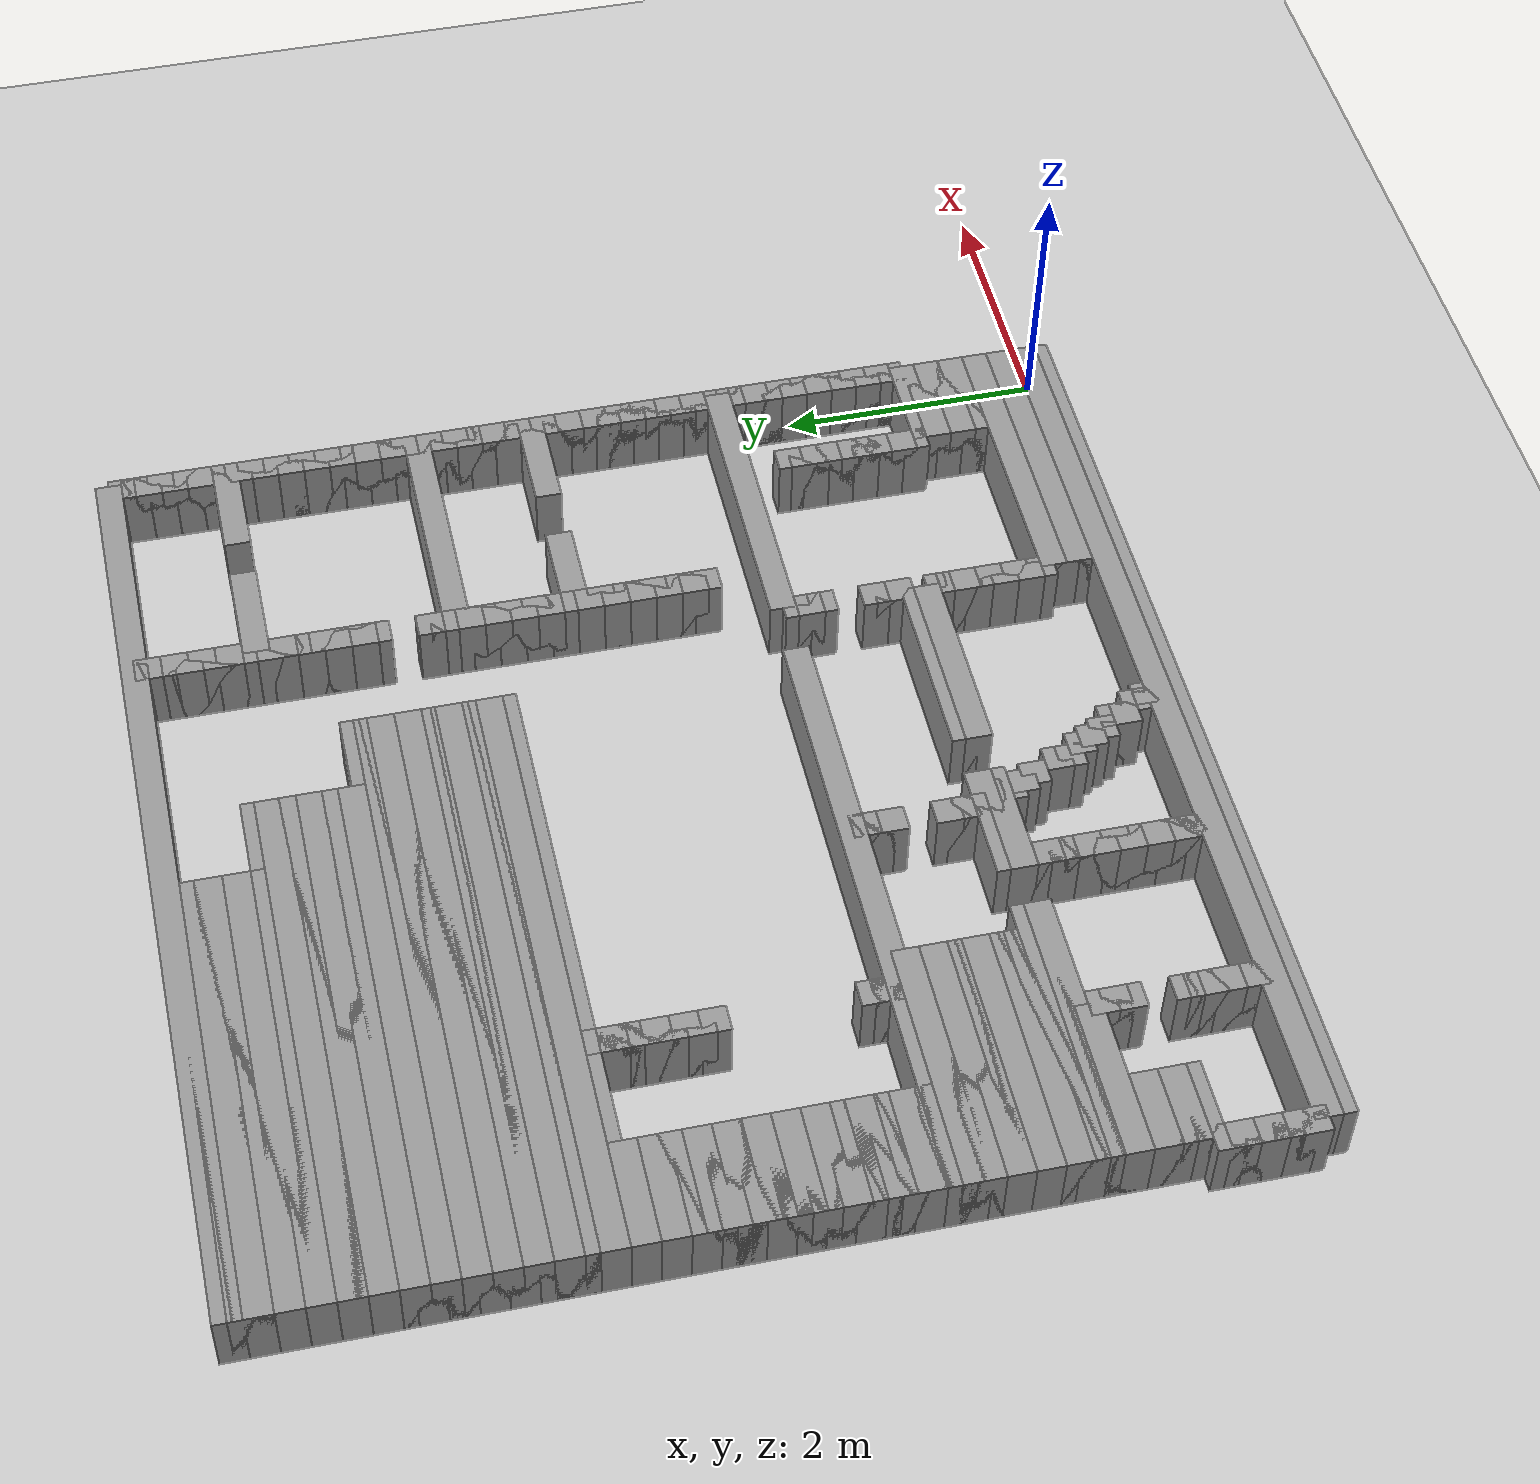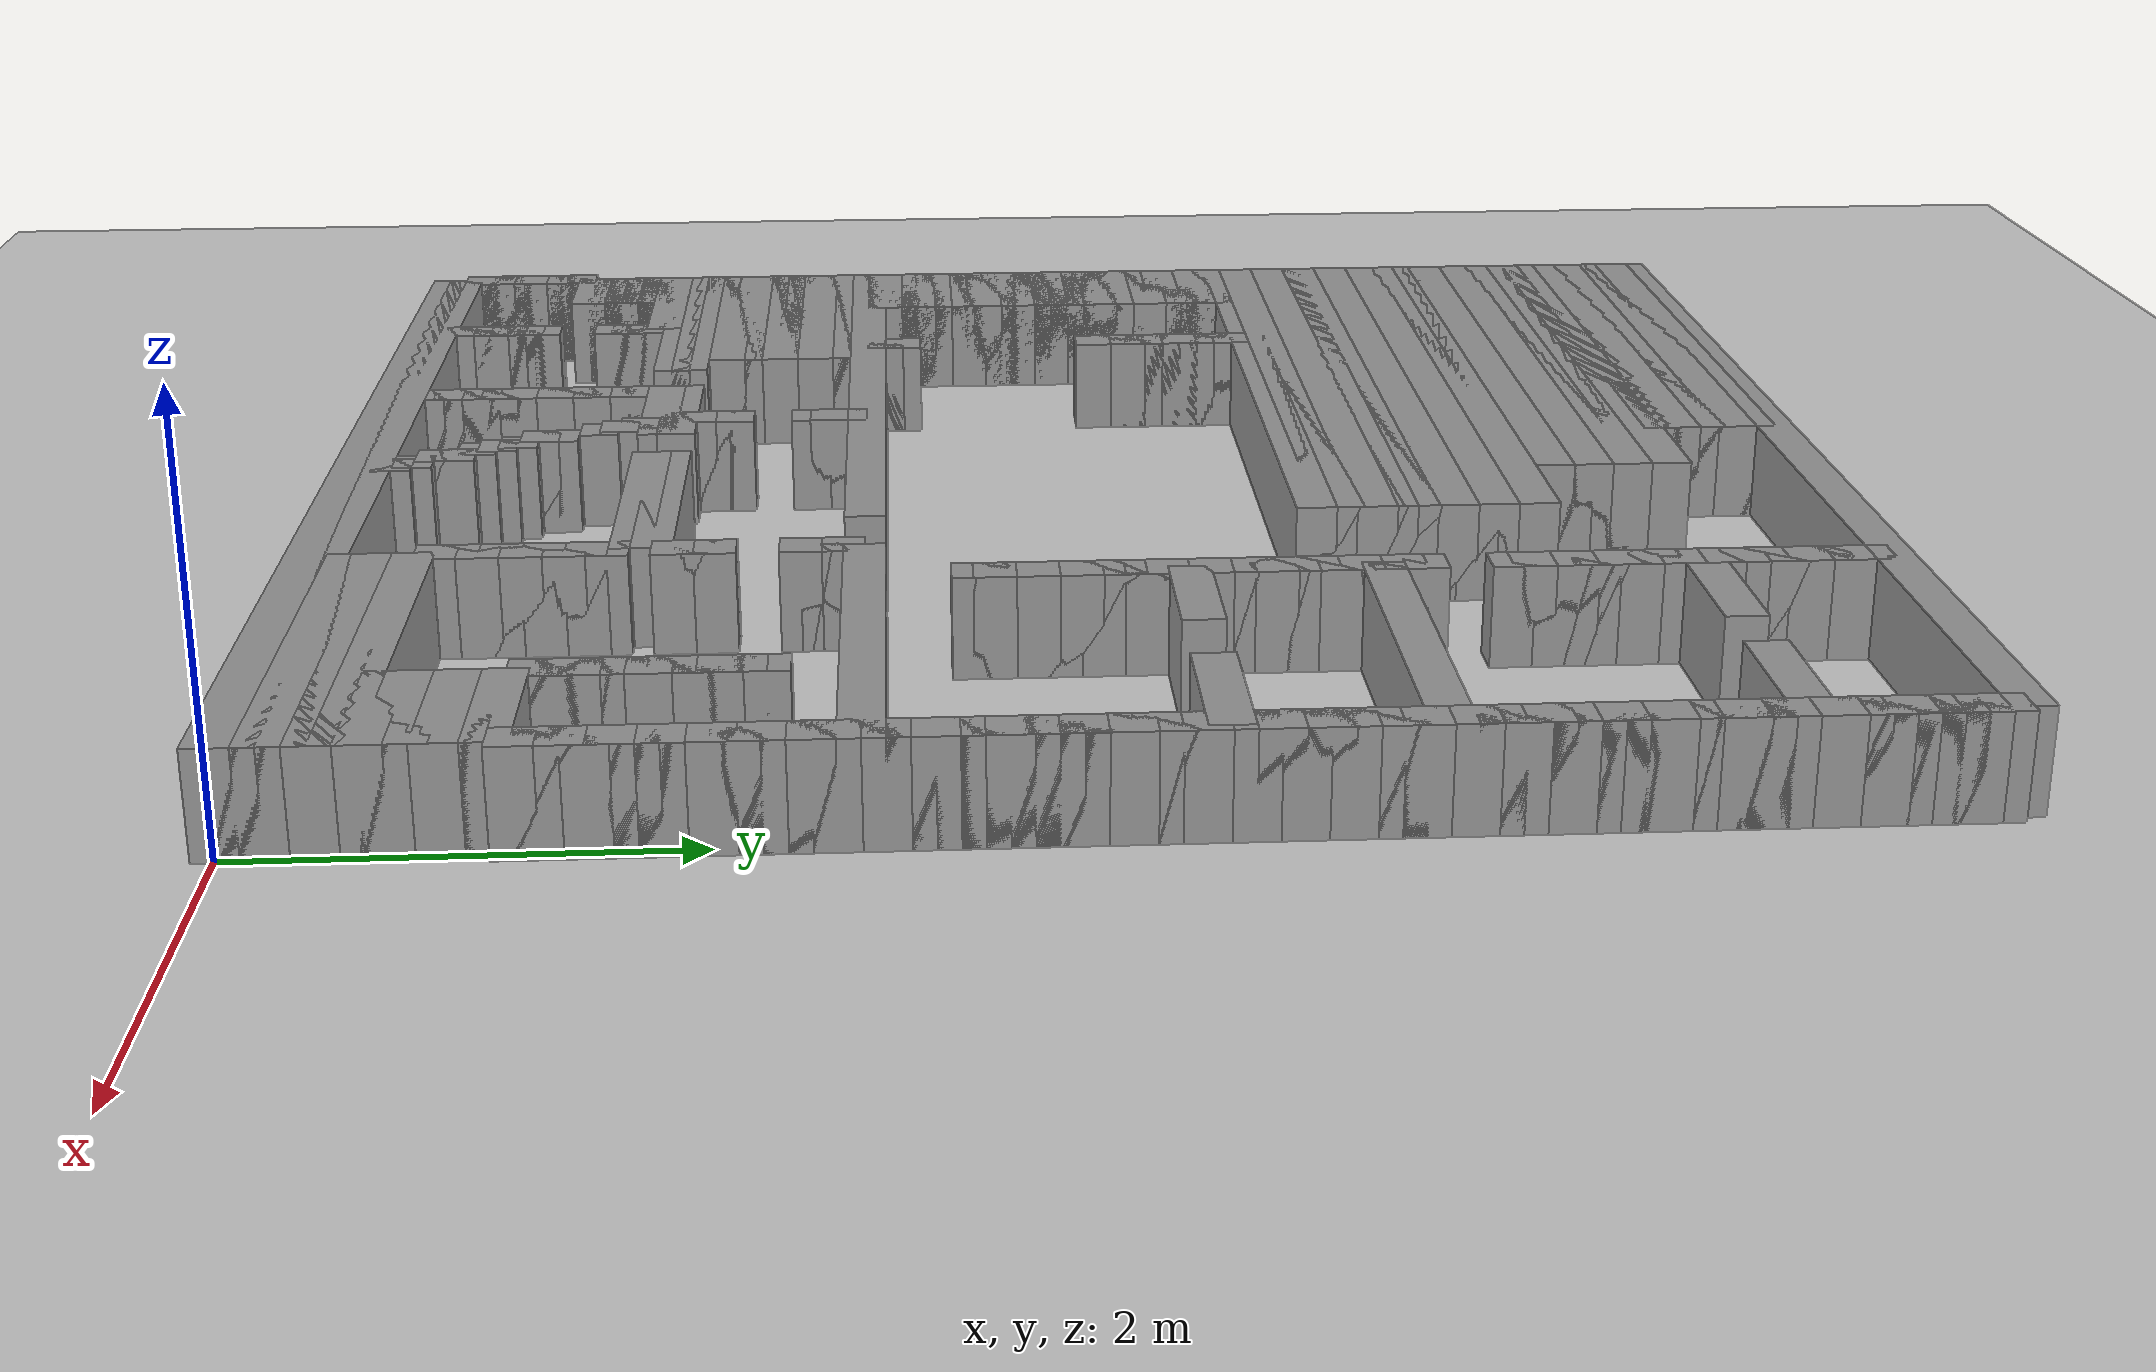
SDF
<?xml version="1.0" ?>
<sdf version="1.6">
	<world name="GridMap">
		<include>
			<uri>model://sun</uri>
		</include>
		<include>
			<uri>model://ground_plane</uri>
		</include>
		<physics type="ode">
			<real_time_update_rate>1000.0</real_time_update_rate>
			<max_step_size>0.001</max_step_size>
			<real_time_factor>1</real_time_factor>
			<ode>
				<solver>
					<type>quick</type>
					<iters>150</iters>
					<precon_iters>0</precon_iters>
					<sor>1.4</sor>
					<use_dynamic_moi_rescaling>1</use_dynamic_moi_rescaling>
				</solver>
				<constraints>
					<cfm>0.00001</cfm>
					<erp>0.2</erp>
					<contact_max_correcting_vel>2000.000000</contact_max_correcting_vel>
					<contact_surface_layer>0.01000</contact_surface_layer>
				</constraints>
			</ode>
		</physics>
		<model name="GridMap">
			<pose frame="">0 0 0 0 -0 0</pose>
			<link name="Wall_(37.0,0.0)">
				<collision name="Wall_(37.0,0.0)_Collision">
					<geometry>
						<box>
							<size>7.4 0.2 0.5</size>
						</box>
					</geometry>
					<pose frame="">-3.7 0.0 0.25 0 -0 0</pose>
				</collision>
				<inertial>
					<mass>0.5</mass>
					<pose>0 0.01 0 0 0 0</pose>
					<inertia>
						<ixx>0.004</ixx>
						<ixy>0.001</ixy>
						<ixz>0</ixz>
						<iyy>0.006</iyy>
						<iyz>0</iyz>
						<izz>0.007</izz>
					</inertia>
				</inertial>
				<visual name="Wall_(37.0,0.0)_Visual">
					<geometry>
						<box>
							<size>7.4 0.2 0.5</size>
						</box>
					</geometry>
					<pose frame="">-3.7 0.0 0.25 0 -0 0</pose>
					<material>
						<script>
							<uri>file://media/materials/scripts/gazebo.material</uri>
							<name>Gazebo/Grey</name>
						</script>
						<ambient>1 1 1 1</ambient>
					</material>
					<meta>
						<layer>0</layer>
					</meta>
				</visual>
				<pose frame="">0 0 0 0 -0 0</pose>
			</link>
			<link name="Wall_(37.0,1.0)">
				<collision name="Wall_(37.0,1.0)_Collision">
					<geometry>
						<box>
							<size>7.4 0.2 0.5</size>
						</box>
					</geometry>
					<pose frame="">-3.7 0.1 0.25 0 -0 0</pose>
				</collision>
				<inertial>
					<mass>0.5</mass>
					<pose>0 0.01 0 0 0 0</pose>
					<inertia>
						<ixx>0.004</ixx>
						<ixy>0.001</ixy>
						<ixz>0</ixz>
						<iyy>0.006</iyy>
						<iyz>0</iyz>
						<izz>0.007</izz>
					</inertia>
				</inertial>
				<visual name="Wall_(37.0,1.0)_Visual">
					<geometry>
						<box>
							<size>7.4 0.2 0.5</size>
						</box>
					</geometry>
					<pose frame="">-3.7 0.1 0.25 0 -0 0</pose>
					<material>
						<script>
							<uri>file://media/materials/scripts/gazebo.material</uri>
							<name>Gazebo/Grey</name>
						</script>
						<ambient>1 1 1 1</ambient>
					</material>
					<meta>
						<layer>0</layer>
					</meta>
				</visual>
				<pose frame="">0 0 0 0 -0 0</pose>
			</link>
			<link name="Wall_(11.5,2.0)">
				<collision name="Wall_(11.5,2.0)_Collision">
					<geometry>
						<box>
							<size>2.3000000000000003 0.2 0.5</size>
						</box>
					</geometry>
					<pose frame="">-1.1500000000000001 0.2 0.25 0 -0 0</pose>
				</collision>
				<inertial>
					<mass>0.5</mass>
					<pose>0 0.01 0 0 0 0</pose>
					<inertia>
						<ixx>0.004</ixx>
						<ixy>0.001</ixy>
						<ixz>0</ixz>
						<iyy>0.006</iyy>
						<iyz>0</iyz>
						<izz>0.007</izz>
					</inertia>
				</inertial>
				<visual name="Wall_(11.5,2.0)_Visual">
					<geometry>
						<box>
							<size>2.3000000000000003 0.2 0.5</size>
						</box>
					</geometry>
					<pose frame="">-1.1500000000000001 0.2 0.25 0 -0 0</pose>
					<material>
						<script>
							<uri>file://media/materials/scripts/gazebo.material</uri>
							<name>Gazebo/Grey</name>
						</script>
						<ambient>1 1 1 1</ambient>
					</material>
					<meta>
						<layer>0</layer>
					</meta>
				</visual>
				<pose frame="">0 0 0 0 -0 0</pose>
			</link>
			<link name="Wall_(36.5,2.0)">
				<collision name="Wall_(36.5,2.0)_Collision">
					<geometry>
						<box>
							<size>0.2 0.2 0.5</size>
						</box>
					</geometry>
					<pose frame="">-3.6500000000000004 0.2 0.25 0 -0 0</pose>
				</collision>
				<inertial>
					<mass>0.5</mass>
					<pose>0 0.01 0 0 0 0</pose>
					<inertia>
						<ixx>0.004</ixx>
						<ixy>0.001</ixy>
						<ixz>0</ixz>
						<iyy>0.006</iyy>
						<iyz>0</iyz>
						<izz>0.007</izz>
					</inertia>
				</inertial>
				<visual name="Wall_(36.5,2.0)_Visual">
					<geometry>
						<box>
							<size>0.2 0.2 0.5</size>
						</box>
					</geometry>
					<pose frame="">-3.6500000000000004 0.2 0.25 0 -0 0</pose>
					<material>
						<script>
							<uri>file://media/materials/scripts/gazebo.material</uri>
							<name>Gazebo/Grey</name>
						</script>
						<ambient>1 1 1 1</ambient>
					</material>
					<meta>
						<layer>0</layer>
					</meta>
				</visual>
				<pose frame="">0 0 0 0 -0 0</pose>
			</link>
			<link name="Wall_(49.0,2.0)">
				<collision name="Wall_(49.0,2.0)_Collision">
					<geometry>
						<box>
							<size>0.2 0.2 0.5</size>
						</box>
					</geometry>
					<pose frame="">-4.9 0.2 0.25 0 -0 0</pose>
				</collision>
				<inertial>
					<mass>0.5</mass>
					<pose>0 0.01 0 0 0 0</pose>
					<inertia>
						<ixx>0.004</ixx>
						<ixy>0.001</ixy>
						<ixz>0</ixz>
						<iyy>0.006</iyy>
						<iyz>0</iyz>
						<izz>0.007</izz>
					</inertia>
				</inertial>
				<visual name="Wall_(49.0,2.0)_Visual">
					<geometry>
						<box>
							<size>0.2 0.2 0.5</size>
						</box>
					</geometry>
					<pose frame="">-4.9 0.2 0.25 0 -0 0</pose>
					<material>
						<script>
							<uri>file://media/materials/scripts/gazebo.material</uri>
							<name>Gazebo/Grey</name>
						</script>
						<ambient>1 1 1 1</ambient>
					</material>
					<meta>
						<layer>0</layer>
					</meta>
				</visual>
				<pose frame="">0 0 0 0 -0 0</pose>
			</link>
			<link name="Wall_(62.0,2.0)">
				<collision name="Wall_(62.0,2.0)_Collision">
					<geometry>
						<box>
							<size>0.2 0.2 0.5</size>
						</box>
					</geometry>
					<pose frame="">-6.2 0.2 0.25 0 -0 0</pose>
				</collision>
				<inertial>
					<mass>0.5</mass>
					<pose>0 0.01 0 0 0 0</pose>
					<inertia>
						<ixx>0.004</ixx>
						<ixy>0.001</ixy>
						<ixz>0</ixz>
						<iyy>0.006</iyy>
						<iyz>0</iyz>
						<izz>0.007</izz>
					</inertia>
				</inertial>
				<visual name="Wall_(62.0,2.0)_Visual">
					<geometry>
						<box>
							<size>0.2 0.2 0.5</size>
						</box>
					</geometry>
					<pose frame="">-6.2 0.2 0.25 0 -0 0</pose>
					<material>
						<script>
							<uri>file://media/materials/scripts/gazebo.material</uri>
							<name>Gazebo/Grey</name>
						</script>
						<ambient>1 1 1 1</ambient>
					</material>
					<meta>
						<layer>0</layer>
					</meta>
				</visual>
				<pose frame="">0 0 0 0 -0 0</pose>
			</link>
			<link name="Wall_(74.0,2.0)">
				<collision name="Wall_(74.0,2.0)_Collision">
					<geometry>
						<box>
							<size>0.2 0.2 0.5</size>
						</box>
					</geometry>
					<pose frame="">-7.4 0.2 0.25 0 -0 0</pose>
				</collision>
				<inertial>
					<mass>0.5</mass>
					<pose>0 0.01 0 0 0 0</pose>
					<inertia>
						<ixx>0.004</ixx>
						<ixy>0.001</ixy>
						<ixz>0</ixz>
						<iyy>0.006</iyy>
						<iyz>0</iyz>
						<izz>0.007</izz>
					</inertia>
				</inertial>
				<visual name="Wall_(74.0,2.0)_Visual">
					<geometry>
						<box>
							<size>0.2 0.2 0.5</size>
						</box>
					</geometry>
					<pose frame="">-7.4 0.2 0.25 0 -0 0</pose>
					<material>
						<script>
							<uri>file://media/materials/scripts/gazebo.material</uri>
							<name>Gazebo/Grey</name>
						</script>
						<ambient>1 1 1 1</ambient>
					</material>
					<meta>
						<layer>0</layer>
					</meta>
				</visual>
				<pose frame="">0 0 0 0 -0 0</pose>
			</link>
			<link name="Wall_(11.5,3.0)">
				<collision name="Wall_(11.5,3.0)_Collision">
					<geometry>
						<box>
							<size>2.3000000000000003 0.2 0.5</size>
						</box>
					</geometry>
					<pose frame="">-1.1500000000000001 0.30000000000000004 0.25 0 -0 0</pose>
				</collision>
				<inertial>
					<mass>0.5</mass>
					<pose>0 0.01 0 0 0 0</pose>
					<inertia>
						<ixx>0.004</ixx>
						<ixy>0.001</ixy>
						<ixz>0</ixz>
						<iyy>0.006</iyy>
						<iyz>0</iyz>
						<izz>0.007</izz>
					</inertia>
				</inertial>
				<visual name="Wall_(11.5,3.0)_Visual">
					<geometry>
						<box>
							<size>2.3000000000000003 0.2 0.5</size>
						</box>
					</geometry>
					<pose frame="">-1.1500000000000001 0.30000000000000004 0.25 0 -0 0</pose>
					<material>
						<script>
							<uri>file://media/materials/scripts/gazebo.material</uri>
							<name>Gazebo/Grey</name>
						</script>
						<ambient>1 1 1 1</ambient>
					</material>
					<meta>
						<layer>0</layer>
					</meta>
				</visual>
				<pose frame="">0 0 0 0 -0 0</pose>
			</link>
			<link name="Wall_(37.0,3.0)">
				<collision name="Wall_(37.0,3.0)_Collision">
					<geometry>
						<box>
							<size>0.2 0.2 0.5</size>
						</box>
					</geometry>
					<pose frame="">-3.7 0.30000000000000004 0.25 0 -0 0</pose>
				</collision>
				<inertial>
					<mass>0.5</mass>
					<pose>0 0.01 0 0 0 0</pose>
					<inertia>
						<ixx>0.004</ixx>
						<ixy>0.001</ixy>
						<ixz>0</ixz>
						<iyy>0.006</iyy>
						<iyz>0</iyz>
						<izz>0.007</izz>
					</inertia>
				</inertial>
				<visual name="Wall_(37.0,3.0)_Visual">
					<geometry>
						<box>
							<size>0.2 0.2 0.5</size>
						</box>
					</geometry>
					<pose frame="">-3.7 0.30000000000000004 0.25 0 -0 0</pose>
					<material>
						<script>
							<uri>file://media/materials/scripts/gazebo.material</uri>
							<name>Gazebo/Grey</name>
						</script>
						<ambient>1 1 1 1</ambient>
					</material>
					<meta>
						<layer>0</layer>
					</meta>
				</visual>
				<pose frame="">0 0 0 0 -0 0</pose>
			</link>
			<link name="Wall_(49.0,3.0)">
				<collision name="Wall_(49.0,3.0)_Collision">
					<geometry>
						<box>
							<size>0.2 0.2 0.5</size>
						</box>
					</geometry>
					<pose frame="">-4.9 0.30000000000000004 0.25 0 -0 0</pose>
				</collision>
				<inertial>
					<mass>0.5</mass>
					<pose>0 0.01 0 0 0 0</pose>
					<inertia>
						<ixx>0.004</ixx>
						<ixy>0.001</ixy>
						<ixz>0</ixz>
						<iyy>0.006</iyy>
						<iyz>0</iyz>
						<izz>0.007</izz>
					</inertia>
				</inertial>
				<visual name="Wall_(49.0,3.0)_Visual">
					<geometry>
						<box>
							<size>0.2 0.2 0.5</size>
						</box>
					</geometry>
					<pose frame="">-4.9 0.30000000000000004 0.25 0 -0 0</pose>
					<material>
						<script>
							<uri>file://media/materials/scripts/gazebo.material</uri>
							<name>Gazebo/Grey</name>
						</script>
						<ambient>1 1 1 1</ambient>
					</material>
					<meta>
						<layer>0</layer>
					</meta>
				</visual>
				<pose frame="">0 0 0 0 -0 0</pose>
			</link>
			<link name="Wall_(62.0,3.0)">
				<collision name="Wall_(62.0,3.0)_Collision">
					<geometry>
						<box>
							<size>0.2 0.2 0.5</size>
						</box>
					</geometry>
					<pose frame="">-6.2 0.30000000000000004 0.25 0 -0 0</pose>
				</collision>
				<inertial>
					<mass>0.5</mass>
					<pose>0 0.01 0 0 0 0</pose>
					<inertia>
						<ixx>0.004</ixx>
						<ixy>0.001</ixy>
						<ixz>0</ixz>
						<iyy>0.006</iyy>
						<iyz>0</iyz>
						<izz>0.007</izz>
					</inertia>
				</inertial>
				<visual name="Wall_(62.0,3.0)_Visual">
					<geometry>
						<box>
							<size>0.2 0.2 0.5</size>
						</box>
					</geometry>
					<pose frame="">-6.2 0.30000000000000004 0.25 0 -0 0</pose>
					<material>
						<script>
							<uri>file://media/materials/scripts/gazebo.material</uri>
							<name>Gazebo/Grey</name>
						</script>
						<ambient>1 1 1 1</ambient>
					</material>
					<meta>
						<layer>0</layer>
					</meta>
				</visual>
				<pose frame="">0 0 0 0 -0 0</pose>
			</link>
			<link name="Wall_(74.0,3.0)">
				<collision name="Wall_(74.0,3.0)_Collision">
					<geometry>
						<box>
							<size>0.2 0.2 0.5</size>
						</box>
					</geometry>
					<pose frame="">-7.4 0.30000000000000004 0.25 0 -0 0</pose>
				</collision>
				<inertial>
					<mass>0.5</mass>
					<pose>0 0.01 0 0 0 0</pose>
					<inertia>
						<ixx>0.004</ixx>
						<ixy>0.001</ixy>
						<ixz>0</ixz>
						<iyy>0.006</iyy>
						<iyz>0</iyz>
						<izz>0.007</izz>
					</inertia>
				</inertial>
				<visual name="Wall_(74.0,3.0)_Visual">
					<geometry>
						<box>
							<size>0.2 0.2 0.5</size>
						</box>
					</geometry>
					<pose frame="">-7.4 0.30000000000000004 0.25 0 -0 0</pose>
					<material>
						<script>
							<uri>file://media/materials/scripts/gazebo.material</uri>
							<name>Gazebo/Grey</name>
						</script>
						<ambient>1 1 1 1</ambient>
					</material>
					<meta>
						<layer>0</layer>
					</meta>
				</visual>
				<pose frame="">0 0 0 0 -0 0</pose>
			</link>
			<link name="Wall_(11.5,4.0)">
				<collision name="Wall_(11.5,4.0)_Collision">
					<geometry>
						<box>
							<size>2.3000000000000003 0.2 0.5</size>
						</box>
					</geometry>
					<pose frame="">-1.1500000000000001 0.4 0.25 0 -0 0</pose>
				</collision>
				<inertial>
					<mass>0.5</mass>
					<pose>0 0.01 0 0 0 0</pose>
					<inertia>
						<ixx>0.004</ixx>
						<ixy>0.001</ixy>
						<ixz>0</ixz>
						<iyy>0.006</iyy>
						<iyz>0</iyz>
						<izz>0.007</izz>
					</inertia>
				</inertial>
				<visual name="Wall_(11.5,4.0)_Visual">
					<geometry>
						<box>
							<size>2.3000000000000003 0.2 0.5</size>
						</box>
					</geometry>
					<pose frame="">-1.1500000000000001 0.4 0.25 0 -0 0</pose>
					<material>
						<script>
							<uri>file://media/materials/scripts/gazebo.material</uri>
							<name>Gazebo/Grey</name>
						</script>
						<ambient>1 1 1 1</ambient>
					</material>
					<meta>
						<layer>0</layer>
					</meta>
				</visual>
				<pose frame="">0 0 0 0 -0 0</pose>
			</link>
			<link name="Wall_(38.0,4.0)">
				<collision name="Wall_(38.0,4.0)_Collision">
					<geometry>
						<box>
							<size>0.2 0.2 0.5</size>
						</box>
					</geometry>
					<pose frame="">-3.8000000000000003 0.4 0.25 0 -0 0</pose>
				</collision>
				<inertial>
					<mass>0.5</mass>
					<pose>0 0.01 0 0 0 0</pose>
					<inertia>
						<ixx>0.004</ixx>
						<ixy>0.001</ixy>
						<ixz>0</ixz>
						<iyy>0.006</iyy>
						<iyz>0</iyz>
						<izz>0.007</izz>
					</inertia>
				</inertial>
				<visual name="Wall_(38.0,4.0)_Visual">
					<geometry>
						<box>
							<size>0.2 0.2 0.5</size>
						</box>
					</geometry>
					<pose frame="">-3.8000000000000003 0.4 0.25 0 -0 0</pose>
					<material>
						<script>
							<uri>file://media/materials/scripts/gazebo.material</uri>
							<name>Gazebo/Grey</name>
						</script>
						<ambient>1 1 1 1</ambient>
					</material>
					<meta>
						<layer>0</layer>
					</meta>
				</visual>
				<pose frame="">0 0 0 0 -0 0</pose>
			</link>
			<link name="Wall_(49.0,4.0)">
				<collision name="Wall_(49.0,4.0)_Collision">
					<geometry>
						<box>
							<size>0.2 0.2 0.5</size>
						</box>
					</geometry>
					<pose frame="">-4.9 0.4 0.25 0 -0 0</pose>
				</collision>
				<inertial>
					<mass>0.5</mass>
					<pose>0 0.01 0 0 0 0</pose>
					<inertia>
						<ixx>0.004</ixx>
						<ixy>0.001</ixy>
						<ixz>0</ixz>
						<iyy>0.006</iyy>
						<iyz>0</iyz>
						<izz>0.007</izz>
					</inertia>
				</inertial>
				<visual name="Wall_(49.0,4.0)_Visual">
					<geometry>
						<box>
							<size>0.2 0.2 0.5</size>
						</box>
					</geometry>
					<pose frame="">-4.9 0.4 0.25 0 -0 0</pose>
					<material>
						<script>
							<uri>file://media/materials/scripts/gazebo.material</uri>
							<name>Gazebo/Grey</name>
						</script>
						<ambient>1 1 1 1</ambient>
					</material>
					<meta>
						<layer>0</layer>
					</meta>
				</visual>
				<pose frame="">0 0 0 0 -0 0</pose>
			</link>
			<link name="Wall_(62.0,4.0)">
				<collision name="Wall_(62.0,4.0)_Collision">
					<geometry>
						<box>
							<size>0.2 0.2 0.5</size>
						</box>
					</geometry>
					<pose frame="">-6.2 0.4 0.25 0 -0 0</pose>
				</collision>
				<inertial>
					<mass>0.5</mass>
					<pose>0 0.01 0 0 0 0</pose>
					<inertia>
						<ixx>0.004</ixx>
						<ixy>0.001</ixy>
						<ixz>0</ixz>
						<iyy>0.006</iyy>
						<iyz>0</iyz>
						<izz>0.007</izz>
					</inertia>
				</inertial>
				<visual name="Wall_(62.0,4.0)_Visual">
					<geometry>
						<box>
							<size>0.2 0.2 0.5</size>
						</box>
					</geometry>
					<pose frame="">-6.2 0.4 0.25 0 -0 0</pose>
					<material>
						<script>
							<uri>file://media/materials/scripts/gazebo.material</uri>
							<name>Gazebo/Grey</name>
						</script>
						<ambient>1 1 1 1</ambient>
					</material>
					<meta>
						<layer>0</layer>
					</meta>
				</visual>
				<pose frame="">0 0 0 0 -0 0</pose>
			</link>
			<link name="Wall_(74.0,4.0)">
				<collision name="Wall_(74.0,4.0)_Collision">
					<geometry>
						<box>
							<size>0.2 0.2 0.5</size>
						</box>
					</geometry>
					<pose frame="">-7.4 0.4 0.25 0 -0 0</pose>
				</collision>
				<inertial>
					<mass>0.5</mass>
					<pose>0 0.01 0 0 0 0</pose>
					<inertia>
						<ixx>0.004</ixx>
						<ixy>0.001</ixy>
						<ixz>0</ixz>
						<iyy>0.006</iyy>
						<iyz>0</iyz>
						<izz>0.007</izz>
					</inertia>
				</inertial>
				<visual name="Wall_(74.0,4.0)_Visual">
					<geometry>
						<box>
							<size>0.2 0.2 0.5</size>
						</box>
					</geometry>
					<pose frame="">-7.4 0.4 0.25 0 -0 0</pose>
					<material>
						<script>
							<uri>file://media/materials/scripts/gazebo.material</uri>
							<name>Gazebo/Grey</name>
						</script>
						<ambient>1 1 1 1</ambient>
					</material>
					<meta>
						<layer>0</layer>
					</meta>
				</visual>
				<pose frame="">0 0 0 0 -0 0</pose>
			</link>
			<link name="Wall_(11.5,5.0)">
				<collision name="Wall_(11.5,5.0)_Collision">
					<geometry>
						<box>
							<size>2.3000000000000003 0.2 0.5</size>
						</box>
					</geometry>
					<pose frame="">-1.1500000000000001 0.5 0.25 0 -0 0</pose>
				</collision>
				<inertial>
					<mass>0.5</mass>
					<pose>0 0.01 0 0 0 0</pose>
					<inertia>
						<ixx>0.004</ixx>
						<ixy>0.001</ixy>
						<ixz>0</ixz>
						<iyy>0.006</iyy>
						<iyz>0</iyz>
						<izz>0.007</izz>
					</inertia>
				</inertial>
				<visual name="Wall_(11.5,5.0)_Visual">
					<geometry>
						<box>
							<size>2.3000000000000003 0.2 0.5</size>
						</box>
					</geometry>
					<pose frame="">-1.1500000000000001 0.5 0.25 0 -0 0</pose>
					<material>
						<script>
							<uri>file://media/materials/scripts/gazebo.material</uri>
							<name>Gazebo/Grey</name>
						</script>
						<ambient>1 1 1 1</ambient>
					</material>
					<meta>
						<layer>0</layer>
					</meta>
				</visual>
				<pose frame="">0 0 0 0 -0 0</pose>
			</link>
			<link name="Wall_(38.0,5.0)">
				<collision name="Wall_(38.0,5.0)_Collision">
					<geometry>
						<box>
							<size>0.2 0.2 0.5</size>
						</box>
					</geometry>
					<pose frame="">-3.8000000000000003 0.5 0.25 0 -0 0</pose>
				</collision>
				<inertial>
					<mass>0.5</mass>
					<pose>0 0.01 0 0 0 0</pose>
					<inertia>
						<ixx>0.004</ixx>
						<ixy>0.001</ixy>
						<ixz>0</ixz>
						<iyy>0.006</iyy>
						<iyz>0</iyz>
						<izz>0.007</izz>
					</inertia>
				</inertial>
				<visual name="Wall_(38.0,5.0)_Visual">
					<geometry>
						<box>
							<size>0.2 0.2 0.5</size>
						</box>
					</geometry>
					<pose frame="">-3.8000000000000003 0.5 0.25 0 -0 0</pose>
					<material>
						<script>
							<uri>file://media/materials/scripts/gazebo.material</uri>
							<name>Gazebo/Grey</name>
						</script>
						<ambient>1 1 1 1</ambient>
					</material>
					<meta>
						<layer>0</layer>
					</meta>
				</visual>
				<pose frame="">0 0 0 0 -0 0</pose>
			</link>
			<link name="Wall_(49.0,5.0)">
				<collision name="Wall_(49.0,5.0)_Collision">
					<geometry>
						<box>
							<size>0.2 0.2 0.5</size>
						</box>
					</geometry>
					<pose frame="">-4.9 0.5 0.25 0 -0 0</pose>
				</collision>
				<inertial>
					<mass>0.5</mass>
					<pose>0 0.01 0 0 0 0</pose>
					<inertia>
						<ixx>0.004</ixx>
						<ixy>0.001</ixy>
						<ixz>0</ixz>
						<iyy>0.006</iyy>
						<iyz>0</iyz>
						<izz>0.007</izz>
					</inertia>
				</inertial>
				<visual name="Wall_(49.0,5.0)_Visual">
					<geometry>
						<box>
							<size>0.2 0.2 0.5</size>
						</box>
					</geometry>
					<pose frame="">-4.9 0.5 0.25 0 -0 0</pose>
					<material>
						<script>
							<uri>file://media/materials/scripts/gazebo.material</uri>
							<name>Gazebo/Grey</name>
						</script>
						<ambient>1 1 1 1</ambient>
					</material>
					<meta>
						<layer>0</layer>
					</meta>
				</visual>
				<pose frame="">0 0 0 0 -0 0</pose>
			</link>
			<link name="Wall_(62.0,5.0)">
				<collision name="Wall_(62.0,5.0)_Collision">
					<geometry>
						<box>
							<size>0.2 0.2 0.5</size>
						</box>
					</geometry>
					<pose frame="">-6.2 0.5 0.25 0 -0 0</pose>
				</collision>
				<inertial>
					<mass>0.5</mass>
					<pose>0 0.01 0 0 0 0</pose>
					<inertia>
						<ixx>0.004</ixx>
						<ixy>0.001</ixy>
						<ixz>0</ixz>
						<iyy>0.006</iyy>
						<iyz>0</iyz>
						<izz>0.007</izz>
					</inertia>
				</inertial>
				<visual name="Wall_(62.0,5.0)_Visual">
					<geometry>
						<box>
							<size>0.2 0.2 0.5</size>
						</box>
					</geometry>
					<pose frame="">-6.2 0.5 0.25 0 -0 0</pose>
					<material>
						<script>
							<uri>file://media/materials/scripts/gazebo.material</uri>
							<name>Gazebo/Grey</name>
						</script>
						<ambient>1 1 1 1</ambient>
					</material>
					<meta>
						<layer>0</layer>
					</meta>
				</visual>
				<pose frame="">0 0 0 0 -0 0</pose>
			</link>
			<link name="Wall_(74.0,5.0)">
				<collision name="Wall_(74.0,5.0)_Collision">
					<geometry>
						<box>
							<size>0.2 0.2 0.5</size>
						</box>
					</geometry>
					<pose frame="">-7.4 0.5 0.25 0 -0 0</pose>
				</collision>
				<inertial>
					<mass>0.5</mass>
					<pose>0 0.01 0 0 0 0</pose>
					<inertia>
						<ixx>0.004</ixx>
						<ixy>0.001</ixy>
						<ixz>0</ixz>
						<iyy>0.006</iyy>
						<iyz>0</iyz>
						<izz>0.007</izz>
					</inertia>
				</inertial>
				<visual name="Wall_(74.0,5.0)_Visual">
					<geometry>
						<box>
							<size>0.2 0.2 0.5</size>
						</box>
					</geometry>
					<pose frame="">-7.4 0.5 0.25 0 -0 0</pose>
					<material>
						<script>
							<uri>file://media/materials/scripts/gazebo.material</uri>
							<name>Gazebo/Grey</name>
						</script>
						<ambient>1 1 1 1</ambient>
					</material>
					<meta>
						<layer>0</layer>
					</meta>
				</visual>
				<pose frame="">0 0 0 0 -0 0</pose>
			</link>
			<link name="Wall_(4.0,6.0)">
				<collision name="Wall_(4.0,6.0)_Collision">
					<geometry>
						<box>
							<size>0.8 0.2 0.5</size>
						</box>
					</geometry>
					<pose frame="">-0.4 0.6000000000000001 0.25 0 -0 0</pose>
				</collision>
				<inertial>
					<mass>0.5</mass>
					<pose>0 0.01 0 0 0 0</pose>
					<inertia>
						<ixx>0.004</ixx>
						<ixy>0.001</ixy>
						<ixz>0</ixz>
						<iyy>0.006</iyy>
						<iyz>0</iyz>
						<izz>0.007</izz>
					</inertia>
				</inertial>
				<visual name="Wall_(4.0,6.0)_Visual">
					<geometry>
						<box>
							<size>0.8 0.2 0.5</size>
						</box>
					</geometry>
					<pose frame="">-0.4 0.6000000000000001 0.25 0 -0 0</pose>
					<material>
						<script>
							<uri>file://media/materials/scripts/gazebo.material</uri>
							<name>Gazebo/Grey</name>
						</script>
						<ambient>1 1 1 1</ambient>
					</material>
					<meta>
						<layer>0</layer>
					</meta>
				</visual>
				<pose frame="">0 0 0 0 -0 0</pose>
			</link>
			<link name="Wall_(23.0,6.0)">
				<collision name="Wall_(23.0,6.0)_Collision">
					<geometry>
						<box>
							<size>0.2 0.2 0.5</size>
						</box>
					</geometry>
					<pose frame="">-2.3000000000000003 0.6000000000000001 0.25 0 -0 0</pose>
				</collision>
				<inertial>
					<mass>0.5</mass>
					<pose>0 0.01 0 0 0 0</pose>
					<inertia>
						<ixx>0.004</ixx>
						<ixy>0.001</ixy>
						<ixz>0</ixz>
						<iyy>0.006</iyy>
						<iyz>0</iyz>
						<izz>0.007</izz>
					</inertia>
				</inertial>
				<visual name="Wall_(23.0,6.0)_Visual">
					<geometry>
						<box>
							<size>0.2 0.2 0.5</size>
						</box>
					</geometry>
					<pose frame="">-2.3000000000000003 0.6000000000000001 0.25 0 -0 0</pose>
					<material>
						<script>
							<uri>file://media/materials/scripts/gazebo.material</uri>
							<name>Gazebo/Grey</name>
						</script>
						<ambient>1 1 1 1</ambient>
					</material>
					<meta>
						<layer>0</layer>
					</meta>
				</visual>
				<pose frame="">0 0 0 0 -0 0</pose>
			</link>
			<link name="Wall_(39.0,6.0)">
				<collision name="Wall_(39.0,6.0)_Collision">
					<geometry>
						<box>
							<size>0.2 0.2 0.5</size>
						</box>
					</geometry>
					<pose frame="">-3.9000000000000004 0.6000000000000001 0.25 0 -0 0</pose>
				</collision>
				<inertial>
					<mass>0.5</mass>
					<pose>0 0.01 0 0 0 0</pose>
					<inertia>
						<ixx>0.004</ixx>
						<ixy>0.001</ixy>
						<ixz>0</ixz>
						<iyy>0.006</iyy>
						<iyz>0</iyz>
						<izz>0.007</izz>
					</inertia>
				</inertial>
				<visual name="Wall_(39.0,6.0)_Visual">
					<geometry>
						<box>
							<size>0.2 0.2 0.5</size>
						</box>
					</geometry>
					<pose frame="">-3.9000000000000004 0.6000000000000001 0.25 0 -0 0</pose>
					<material>
						<script>
							<uri>file://media/materials/scripts/gazebo.material</uri>
							<name>Gazebo/Grey</name>
						</script>
						<ambient>1 1 1 1</ambient>
					</material>
					<meta>
						<layer>0</layer>
					</meta>
				</visual>
				<pose frame="">0 0 0 0 -0 0</pose>
			</link>
			<link name="Wall_(49.0,6.0)">
				<collision name="Wall_(49.0,6.0)_Collision">
					<geometry>
						<box>
							<size>0.2 0.2 0.5</size>
						</box>
					</geometry>
					<pose frame="">-4.9 0.6000000000000001 0.25 0 -0 0</pose>
				</collision>
				<inertial>
					<mass>0.5</mass>
					<pose>0 0.01 0 0 0 0</pose>
					<inertia>
						<ixx>0.004</ixx>
						<ixy>0.001</ixy>
						<ixz>0</ixz>
						<iyy>0.006</iyy>
						<iyz>0</iyz>
						<izz>0.007</izz>
					</inertia>
				</inertial>
				<visual name="Wall_(49.0,6.0)_Visual">
					<geometry>
						<box>
							<size>0.2 0.2 0.5</size>
						</box>
					</geometry>
					<pose frame="">-4.9 0.6000000000000001 0.25 0 -0 0</pose>
					<material>
						<script>
							<uri>file://media/materials/scripts/gazebo.material</uri>
							<name>Gazebo/Grey</name>
						</script>
						<ambient>1 1 1 1</ambient>
					</material>
					<meta>
						<layer>0</layer>
					</meta>
				</visual>
				<pose frame="">0 0 0 0 -0 0</pose>
			</link>
			<link name="Wall_(62.0,6.0)">
				<collision name="Wall_(62.0,6.0)_Collision">
					<geometry>
						<box>
							<size>0.2 0.2 0.5</size>
						</box>
					</geometry>
					<pose frame="">-6.2 0.6000000000000001 0.25 0 -0 0</pose>
				</collision>
				<inertial>
					<mass>0.5</mass>
					<pose>0 0.01 0 0 0 0</pose>
					<inertia>
						<ixx>0.004</ixx>
						<ixy>0.001</ixy>
						<ixz>0</ixz>
						<iyy>0.006</iyy>
						<iyz>0</iyz>
						<izz>0.007</izz>
					</inertia>
				</inertial>
				<visual name="Wall_(62.0,6.0)_Visual">
					<geometry>
						<box>
							<size>0.2 0.2 0.5</size>
						</box>
					</geometry>
					<pose frame="">-6.2 0.6000000000000001 0.25 0 -0 0</pose>
					<material>
						<script>
							<uri>file://media/materials/scripts/gazebo.material</uri>
							<name>Gazebo/Grey</name>
						</script>
						<ambient>1 1 1 1</ambient>
					</material>
					<meta>
						<layer>0</layer>
					</meta>
				</visual>
				<pose frame="">0 0 0 0 -0 0</pose>
			</link>
			<link name="Wall_(74.0,6.0)">
				<collision name="Wall_(74.0,6.0)_Collision">
					<geometry>
						<box>
							<size>0.2 0.2 0.5</size>
						</box>
					</geometry>
					<pose frame="">-7.4 0.6000000000000001 0.25 0 -0 0</pose>
				</collision>
				<inertial>
					<mass>0.5</mass>
					<pose>0 0.01 0 0 0 0</pose>
					<inertia>
						<ixx>0.004</ixx>
						<ixy>0.001</ixy>
						<ixz>0</ixz>
						<iyy>0.006</iyy>
						<iyz>0</iyz>
						<izz>0.007</izz>
					</inertia>
				</inertial>
				<visual name="Wall_(74.0,6.0)_Visual">
					<geometry>
						<box>
							<size>0.2 0.2 0.5</size>
						</box>
					</geometry>
					<pose frame="">-7.4 0.6000000000000001 0.25 0 -0 0</pose>
					<material>
						<script>
							<uri>file://media/materials/scripts/gazebo.material</uri>
							<name>Gazebo/Grey</name>
						</script>
						<ambient>1 1 1 1</ambient>
					</material>
					<meta>
						<layer>0</layer>
					</meta>
				</visual>
				<pose frame="">0 0 0 0 -0 0</pose>
			</link>
			<link name="Wall_(4.0,7.0)">
				<collision name="Wall_(4.0,7.0)_Collision">
					<geometry>
						<box>
							<size>0.8 0.2 0.5</size>
						</box>
					</geometry>
					<pose frame="">-0.4 0.7000000000000001 0.25 0 -0 0</pose>
				</collision>
				<inertial>
					<mass>0.5</mass>
					<pose>0 0.01 0 0 0 0</pose>
					<inertia>
						<ixx>0.004</ixx>
						<ixy>0.001</ixy>
						<ixz>0</ixz>
						<iyy>0.006</iyy>
						<iyz>0</iyz>
						<izz>0.007</izz>
					</inertia>
				</inertial>
				<visual name="Wall_(4.0,7.0)_Visual">
					<geometry>
						<box>
							<size>0.8 0.2 0.5</size>
						</box>
					</geometry>
					<pose frame="">-0.4 0.7000000000000001 0.25 0 -0 0</pose>
					<material>
						<script>
							<uri>file://media/materials/scripts/gazebo.material</uri>
							<name>Gazebo/Grey</name>
						</script>
						<ambient>1 1 1 1</ambient>
					</material>
					<meta>
						<layer>0</layer>
					</meta>
				</visual>
				<pose frame="">0 0 0 0 -0 0</pose>
			</link>
			<link name="Wall_(23.0,7.0)">
				<collision name="Wall_(23.0,7.0)_Collision">
					<geometry>
						<box>
							<size>0.2 0.2 0.5</size>
						</box>
					</geometry>
					<pose frame="">-2.3000000000000003 0.7000000000000001 0.25 0 -0 0</pose>
				</collision>
				<inertial>
					<mass>0.5</mass>
					<pose>0 0.01 0 0 0 0</pose>
					<inertia>
						<ixx>0.004</ixx>
						<ixy>0.001</ixy>
						<ixz>0</ixz>
						<iyy>0.006</iyy>
						<iyz>0</iyz>
						<izz>0.007</izz>
					</inertia>
				</inertial>
				<visual name="Wall_(23.0,7.0)_Visual">
					<geometry>
						<box>
							<size>0.2 0.2 0.5</size>
						</box>
					</geometry>
					<pose frame="">-2.3000000000000003 0.7000000000000001 0.25 0 -0 0</pose>
					<material>
						<script>
							<uri>file://media/materials/scripts/gazebo.material</uri>
							<name>Gazebo/Grey</name>
						</script>
						<ambient>1 1 1 1</ambient>
					</material>
					<meta>
						<layer>0</layer>
					</meta>
				</visual>
				<pose frame="">0 0 0 0 -0 0</pose>
			</link>
			<link name="Wall_(39.5,7.0)">
				<collision name="Wall_(39.5,7.0)_Collision">
					<geometry>
						<box>
							<size>0.2 0.2 0.5</size>
						</box>
					</geometry>
					<pose frame="">-3.95 0.7000000000000001 0.25 0 -0 0</pose>
				</collision>
				<inertial>
					<mass>0.5</mass>
					<pose>0 0.01 0 0 0 0</pose>
					<inertia>
						<ixx>0.004</ixx>
						<ixy>0.001</ixy>
						<ixz>0</ixz>
						<iyy>0.006</iyy>
						<iyz>0</iyz>
						<izz>0.007</izz>
					</inertia>
				</inertial>
				<visual name="Wall_(39.5,7.0)_Visual">
					<geometry>
						<box>
							<size>0.2 0.2 0.5</size>
						</box>
					</geometry>
					<pose frame="">-3.95 0.7000000000000001 0.25 0 -0 0</pose>
					<material>
						<script>
							<uri>file://media/materials/scripts/gazebo.material</uri>
							<name>Gazebo/Grey</name>
						</script>
						<ambient>1 1 1 1</ambient>
					</material>
					<meta>
						<layer>0</layer>
					</meta>
				</visual>
				<pose frame="">0 0 0 0 -0 0</pose>
			</link>
			<link name="Wall_(49.0,7.0)">
				<collision name="Wall_(49.0,7.0)_Collision">
					<geometry>
						<box>
							<size>0.2 0.2 0.5</size>
						</box>
					</geometry>
					<pose frame="">-4.9 0.7000000000000001 0.25 0 -0 0</pose>
				</collision>
				<inertial>
					<mass>0.5</mass>
					<pose>0 0.01 0 0 0 0</pose>
					<inertia>
						<ixx>0.004</ixx>
						<ixy>0.001</ixy>
						<ixz>0</ixz>
						<iyy>0.006</iyy>
						<iyz>0</iyz>
						<izz>0.007</izz>
					</inertia>
				</inertial>
				<visual name="Wall_(49.0,7.0)_Visual">
					<geometry>
						<box>
							<size>0.2 0.2 0.5</size>
						</box>
					</geometry>
					<pose frame="">-4.9 0.7000000000000001 0.25 0 -0 0</pose>
					<material>
						<script>
							<uri>file://media/materials/scripts/gazebo.material</uri>
							<name>Gazebo/Grey</name>
						</script>
						<ambient>1 1 1 1</ambient>
					</material>
					<meta>
						<layer>0</layer>
					</meta>
				</visual>
				<pose frame="">0 0 0 0 -0 0</pose>
			</link>
			<link name="Wall_(62.0,7.0)">
				<collision name="Wall_(62.0,7.0)_Collision">
					<geometry>
						<box>
							<size>0.2 0.2 0.5</size>
						</box>
					</geometry>
					<pose frame="">-6.2 0.7000000000000001 0.25 0 -0 0</pose>
				</collision>
				<inertial>
					<mass>0.5</mass>
					<pose>0 0.01 0 0 0 0</pose>
					<inertia>
						<ixx>0.004</ixx>
						<ixy>0.001</ixy>
						<ixz>0</ixz>
						<iyy>0.006</iyy>
						<iyz>0</iyz>
						<izz>0.007</izz>
					</inertia>
				</inertial>
				<visual name="Wall_(62.0,7.0)_Visual">
					<geometry>
						<box>
							<size>0.2 0.2 0.5</size>
						</box>
					</geometry>
					<pose frame="">-6.2 0.7000000000000001 0.25 0 -0 0</pose>
					<material>
						<script>
							<uri>file://media/materials/scripts/gazebo.material</uri>
							<name>Gazebo/Grey</name>
						</script>
						<ambient>1 1 1 1</ambient>
					</material>
					<meta>
						<layer>0</layer>
					</meta>
				</visual>
				<pose frame="">0 0 0 0 -0 0</pose>
			</link>
			<link name="Wall_(74.0,7.0)">
				<collision name="Wall_(74.0,7.0)_Collision">
					<geometry>
						<box>
							<size>0.2 0.2 0.5</size>
						</box>
					</geometry>
					<pose frame="">-7.4 0.7000000000000001 0.25 0 -0 0</pose>
				</collision>
				<inertial>
					<mass>0.5</mass>
					<pose>0 0.01 0 0 0 0</pose>
					<inertia>
						<ixx>0.004</ixx>
						<ixy>0.001</ixy>
						<ixz>0</ixz>
						<iyy>0.006</iyy>
						<iyz>0</iyz>
						<izz>0.007</izz>
					</inertia>
				</inertial>
				<visual name="Wall_(74.0,7.0)_Visual">
					<geometry>
						<box>
							<size>0.2 0.2 0.5</size>
						</box>
					</geometry>
					<pose frame="">-7.4 0.7000000000000001 0.25 0 -0 0</pose>
					<material>
						<script>
							<uri>file://media/materials/scripts/gazebo.material</uri>
							<name>Gazebo/Grey</name>
						</script>
						<ambient>1 1 1 1</ambient>
					</material>
					<meta>
						<layer>0</layer>
					</meta>
				</visual>
				<pose frame="">0 0 0 0 -0 0</pose>
			</link>
			<link name="Wall_(4.0,8.0)">
				<collision name="Wall_(4.0,8.0)_Collision">
					<geometry>
						<box>
							<size>0.8 0.2 0.5</size>
						</box>
					</geometry>
					<pose frame="">-0.4 0.8 0.25 0 -0 0</pose>
				</collision>
				<inertial>
					<mass>0.5</mass>
					<pose>0 0.01 0 0 0 0</pose>
					<inertia>
						<ixx>0.004</ixx>
						<ixy>0.001</ixy>
						<ixz>0</ixz>
						<iyy>0.006</iyy>
						<iyz>0</iyz>
						<izz>0.007</izz>
					</inertia>
				</inertial>
				<visual name="Wall_(4.0,8.0)_Visual">
					<geometry>
						<box>
							<size>0.8 0.2 0.5</size>
						</box>
					</geometry>
					<pose frame="">-0.4 0.8 0.25 0 -0 0</pose>
					<material>
						<script>
							<uri>file://media/materials/scripts/gazebo.material</uri>
							<name>Gazebo/Grey</name>
						</script>
						<ambient>1 1 1 1</ambient>
					</material>
					<meta>
						<layer>0</layer>
					</meta>
				</visual>
				<pose frame="">0 0 0 0 -0 0</pose>
			</link>
			<link name="Wall_(23.0,8.0)">
				<collision name="Wall_(23.0,8.0)_Collision">
					<geometry>
						<box>
							<size>0.2 0.2 0.5</size>
						</box>
					</geometry>
					<pose frame="">-2.3000000000000003 0.8 0.25 0 -0 0</pose>
				</collision>
				<inertial>
					<mass>0.5</mass>
					<pose>0 0.01 0 0 0 0</pose>
					<inertia>
						<ixx>0.004</ixx>
						<ixy>0.001</ixy>
						<ixz>0</ixz>
						<iyy>0.006</iyy>
						<iyz>0</iyz>
						<izz>0.007</izz>
					</inertia>
				</inertial>
				<visual name="Wall_(23.0,8.0)_Visual">
					<geometry>
						<box>
							<size>0.2 0.2 0.5</size>
						</box>
					</geometry>
					<pose frame="">-2.3000000000000003 0.8 0.25 0 -0 0</pose>
					<material>
						<script>
							<uri>file://media/materials/scripts/gazebo.material</uri>
							<name>Gazebo/Grey</name>
						</script>
						<ambient>1 1 1 1</ambient>
					</material>
					<meta>
						<layer>0</layer>
					</meta>
				</visual>
				<pose frame="">0 0 0 0 -0 0</pose>
			</link>
			<link name="Wall_(40.0,8.0)">
				<collision name="Wall_(40.0,8.0)_Collision">
					<geometry>
						<box>
							<size>0.2 0.2 0.5</size>
						</box>
					</geometry>
					<pose frame="">-4.0 0.8 0.25 0 -0 0</pose>
				</collision>
				<inertial>
					<mass>0.5</mass>
					<pose>0 0.01 0 0 0 0</pose>
					<inertia>
						<ixx>0.004</ixx>
						<ixy>0.001</ixy>
						<ixz>0</ixz>
						<iyy>0.006</iyy>
						<iyz>0</iyz>
						<izz>0.007</izz>
					</inertia>
				</inertial>
				<visual name="Wall_(40.0,8.0)_Visual">
					<geometry>
						<box>
							<size>0.2 0.2 0.5</size>
						</box>
					</geometry>
					<pose frame="">-4.0 0.8 0.25 0 -0 0</pose>
					<material>
						<script>
							<uri>file://media/materials/scripts/gazebo.material</uri>
							<name>Gazebo/Grey</name>
						</script>
						<ambient>1 1 1 1</ambient>
					</material>
					<meta>
						<layer>0</layer>
					</meta>
				</visual>
				<pose frame="">0 0 0 0 -0 0</pose>
			</link>
			<link name="Wall_(49.0,8.0)">
				<collision name="Wall_(49.0,8.0)_Collision">
					<geometry>
						<box>
							<size>0.2 0.2 0.5</size>
						</box>
					</geometry>
					<pose frame="">-4.9 0.8 0.25 0 -0 0</pose>
				</collision>
				<inertial>
					<mass>0.5</mass>
					<pose>0 0.01 0 0 0 0</pose>
					<inertia>
						<ixx>0.004</ixx>
						<ixy>0.001</ixy>
						<ixz>0</ixz>
						<iyy>0.006</iyy>
						<iyz>0</iyz>
						<izz>0.007</izz>
					</inertia>
				</inertial>
				<visual name="Wall_(49.0,8.0)_Visual">
					<geometry>
						<box>
							<size>0.2 0.2 0.5</size>
						</box>
					</geometry>
					<pose frame="">-4.9 0.8 0.25 0 -0 0</pose>
					<material>
						<script>
							<uri>file://media/materials/scripts/gazebo.material</uri>
							<name>Gazebo/Grey</name>
						</script>
						<ambient>1 1 1 1</ambient>
					</material>
					<meta>
						<layer>0</layer>
					</meta>
				</visual>
				<pose frame="">0 0 0 0 -0 0</pose>
			</link>
			<link name="Wall_(74.0,8.0)">
				<collision name="Wall_(74.0,8.0)_Collision">
					<geometry>
						<box>
							<size>0.2 0.2 0.5</size>
						</box>
					</geometry>
					<pose frame="">-7.4 0.8 0.25 0 -0 0</pose>
				</collision>
				<inertial>
					<mass>0.5</mass>
					<pose>0 0.01 0 0 0 0</pose>
					<inertia>
						<ixx>0.004</ixx>
						<ixy>0.001</ixy>
						<ixz>0</ixz>
						<iyy>0.006</iyy>
						<iyz>0</iyz>
						<izz>0.007</izz>
					</inertia>
				</inertial>
				<visual name="Wall_(74.0,8.0)_Visual">
					<geometry>
						<box>
							<size>0.2 0.2 0.5</size>
						</box>
					</geometry>
					<pose frame="">-7.4 0.8 0.25 0 -0 0</pose>
					<material>
						<script>
							<uri>file://media/materials/scripts/gazebo.material</uri>
							<name>Gazebo/Grey</name>
						</script>
						<ambient>1 1 1 1</ambient>
					</material>
					<meta>
						<layer>0</layer>
					</meta>
				</visual>
				<pose frame="">0 0 0 0 -0 0</pose>
			</link>
			<link name="Wall_(4.0,9.0)">
				<collision name="Wall_(4.0,9.0)_Collision">
					<geometry>
						<box>
							<size>0.8 0.2 0.5</size>
						</box>
					</geometry>
					<pose frame="">-0.4 0.9 0.25 0 -0 0</pose>
				</collision>
				<inertial>
					<mass>0.5</mass>
					<pose>0 0.01 0 0 0 0</pose>
					<inertia>
						<ixx>0.004</ixx>
						<ixy>0.001</ixy>
						<ixz>0</ixz>
						<iyy>0.006</iyy>
						<iyz>0</iyz>
						<izz>0.007</izz>
					</inertia>
				</inertial>
				<visual name="Wall_(4.0,9.0)_Visual">
					<geometry>
						<box>
							<size>0.8 0.2 0.5</size>
						</box>
					</geometry>
					<pose frame="">-0.4 0.9 0.25 0 -0 0</pose>
					<material>
						<script>
							<uri>file://media/materials/scripts/gazebo.material</uri>
							<name>Gazebo/Grey</name>
						</script>
						<ambient>1 1 1 1</ambient>
					</material>
					<meta>
						<layer>0</layer>
					</meta>
				</visual>
				<pose frame="">0 0 0 0 -0 0</pose>
			</link>
			<link name="Wall_(23.0,9.0)">
				<collision name="Wall_(23.0,9.0)_Collision">
					<geometry>
						<box>
							<size>0.2 0.2 0.5</size>
						</box>
					</geometry>
					<pose frame="">-2.3000000000000003 0.9 0.25 0 -0 0</pose>
				</collision>
				<inertial>
					<mass>0.5</mass>
					<pose>0 0.01 0 0 0 0</pose>
					<inertia>
						<ixx>0.004</ixx>
						<ixy>0.001</ixy>
						<ixz>0</ixz>
						<iyy>0.006</iyy>
						<iyz>0</iyz>
						<izz>0.007</izz>
					</inertia>
				</inertial>
				<visual name="Wall_(23.0,9.0)_Visual">
					<geometry>
						<box>
							<size>0.2 0.2 0.5</size>
						</box>
					</geometry>
					<pose frame="">-2.3000000000000003 0.9 0.25 0 -0 0</pose>
					<material>
						<script>
							<uri>file://media/materials/scripts/gazebo.material</uri>
							<name>Gazebo/Grey</name>
						</script>
						<ambient>1 1 1 1</ambient>
					</material>
					<meta>
						<layer>0</layer>
					</meta>
				</visual>
				<pose frame="">0 0 0 0 -0 0</pose>
			</link>
			<link name="Wall_(41.0,9.0)">
				<collision name="Wall_(41.0,9.0)_Collision">
					<geometry>
						<box>
							<size>0.2 0.2 0.5</size>
						</box>
					</geometry>
					<pose frame="">-4.1000000000000005 0.9 0.25 0 -0 0</pose>
				</collision>
				<inertial>
					<mass>0.5</mass>
					<pose>0 0.01 0 0 0 0</pose>
					<inertia>
						<ixx>0.004</ixx>
						<ixy>0.001</ixy>
						<ixz>0</ixz>
						<iyy>0.006</iyy>
						<iyz>0</iyz>
						<izz>0.007</izz>
					</inertia>
				</inertial>
				<visual name="Wall_(41.0,9.0)_Visual">
					<geometry>
						<box>
							<size>0.2 0.2 0.5</size>
						</box>
					</geometry>
					<pose frame="">-4.1000000000000005 0.9 0.25 0 -0 0</pose>
					<material>
						<script>
							<uri>file://media/materials/scripts/gazebo.material</uri>
							<name>Gazebo/Grey</name>
						</script>
						<ambient>1 1 1 1</ambient>
					</material>
					<meta>
						<layer>0</layer>
					</meta>
				</visual>
				<pose frame="">0 0 0 0 -0 0</pose>
			</link>
			<link name="Wall_(49.0,9.0)">
				<collision name="Wall_(49.0,9.0)_Collision">
					<geometry>
						<box>
							<size>0.2 0.2 0.5</size>
						</box>
					</geometry>
					<pose frame="">-4.9 0.9 0.25 0 -0 0</pose>
				</collision>
				<inertial>
					<mass>0.5</mass>
					<pose>0 0.01 0 0 0 0</pose>
					<inertia>
						<ixx>0.004</ixx>
						<ixy>0.001</ixy>
						<ixz>0</ixz>
						<iyy>0.006</iyy>
						<iyz>0</iyz>
						<izz>0.007</izz>
					</inertia>
				</inertial>
				<visual name="Wall_(49.0,9.0)_Visual">
					<geometry>
						<box>
							<size>0.2 0.2 0.5</size>
						</box>
					</geometry>
					<pose frame="">-4.9 0.9 0.25 0 -0 0</pose>
					<material>
						<script>
							<uri>file://media/materials/scripts/gazebo.material</uri>
							<name>Gazebo/Grey</name>
						</script>
						<ambient>1 1 1 1</ambient>
					</material>
					<meta>
						<layer>0</layer>
					</meta>
				</visual>
				<pose frame="">0 0 0 0 -0 0</pose>
			</link>
			<link name="Wall_(71.0,9.0)">
				<collision name="Wall_(71.0,9.0)_Collision">
					<geometry>
						<box>
							<size>0.6000000000000001 0.2 0.5</size>
						</box>
					</geometry>
					<pose frame="">-7.1000000000000005 0.9 0.25 0 -0 0</pose>
				</collision>
				<inertial>
					<mass>0.5</mass>
					<pose>0 0.01 0 0 0 0</pose>
					<inertia>
						<ixx>0.004</ixx>
						<ixy>0.001</ixy>
						<ixz>0</ixz>
						<iyy>0.006</iyy>
						<iyz>0</iyz>
						<izz>0.007</izz>
					</inertia>
				</inertial>
				<visual name="Wall_(71.0,9.0)_Visual">
					<geometry>
						<box>
							<size>0.6000000000000001 0.2 0.5</size>
						</box>
					</geometry>
					<pose frame="">-7.1000000000000005 0.9 0.25 0 -0 0</pose>
					<material>
						<script>
							<uri>file://media/materials/scripts/gazebo.material</uri>
							<name>Gazebo/Grey</name>
						</script>
						<ambient>1 1 1 1</ambient>
					</material>
					<meta>
						<layer>0</layer>
					</meta>
				</visual>
				<pose frame="">0 0 0 0 -0 0</pose>
			</link>
			<link name="Wall_(4.0,10.0)">
				<collision name="Wall_(4.0,10.0)_Collision">
					<geometry>
						<box>
							<size>0.8 0.2 0.5</size>
						</box>
					</geometry>
					<pose frame="">-0.4 1.0 0.25 0 -0 0</pose>
				</collision>
				<inertial>
					<mass>0.5</mass>
					<pose>0 0.01 0 0 0 0</pose>
					<inertia>
						<ixx>0.004</ixx>
						<ixy>0.001</ixy>
						<ixz>0</ixz>
						<iyy>0.006</iyy>
						<iyz>0</iyz>
						<izz>0.007</izz>
					</inertia>
				</inertial>
				<visual name="Wall_(4.0,10.0)_Visual">
					<geometry>
						<box>
							<size>0.8 0.2 0.5</size>
						</box>
					</geometry>
					<pose frame="">-0.4 1.0 0.25 0 -0 0</pose>
					<material>
						<script>
							<uri>file://media/materials/scripts/gazebo.material</uri>
							<name>Gazebo/Grey</name>
						</script>
						<ambient>1 1 1 1</ambient>
					</material>
					<meta>
						<layer>0</layer>
					</meta>
				</visual>
				<pose frame="">0 0 0 0 -0 0</pose>
			</link>
			<link name="Wall_(23.0,10.0)">
				<collision name="Wall_(23.0,10.0)_Collision">
					<geometry>
						<box>
							<size>0.2 0.2 0.5</size>
						</box>
					</geometry>
					<pose frame="">-2.3000000000000003 1.0 0.25 0 -0 0</pose>
				</collision>
				<inertial>
					<mass>0.5</mass>
					<pose>0 0.01 0 0 0 0</pose>
					<inertia>
						<ixx>0.004</ixx>
						<ixy>0.001</ixy>
						<ixz>0</ixz>
						<iyy>0.006</iyy>
						<iyz>0</iyz>
						<izz>0.007</izz>
					</inertia>
				</inertial>
				<visual name="Wall_(23.0,10.0)_Visual">
					<geometry>
						<box>
							<size>0.2 0.2 0.5</size>
						</box>
					</geometry>
					<pose frame="">-2.3000000000000003 1.0 0.25 0 -0 0</pose>
					<material>
						<script>
							<uri>file://media/materials/scripts/gazebo.material</uri>
							<name>Gazebo/Grey</name>
						</script>
						<ambient>1 1 1 1</ambient>
					</material>
					<meta>
						<layer>0</layer>
					</meta>
				</visual>
				<pose frame="">0 0 0 0 -0 0</pose>
			</link>
			<link name="Wall_(41.0,10.0)">
				<collision name="Wall_(41.0,10.0)_Collision">
					<geometry>
						<box>
							<size>0.2 0.2 0.5</size>
						</box>
					</geometry>
					<pose frame="">-4.1000000000000005 1.0 0.25 0 -0 0</pose>
				</collision>
				<inertial>
					<mass>0.5</mass>
					<pose>0 0.01 0 0 0 0</pose>
					<inertia>
						<ixx>0.004</ixx>
						<ixy>0.001</ixy>
						<ixz>0</ixz>
						<iyy>0.006</iyy>
						<iyz>0</iyz>
						<izz>0.007</izz>
					</inertia>
				</inertial>
				<visual name="Wall_(41.0,10.0)_Visual">
					<geometry>
						<box>
							<size>0.2 0.2 0.5</size>
						</box>
					</geometry>
					<pose frame="">-4.1000000000000005 1.0 0.25 0 -0 0</pose>
					<material>
						<script>
							<uri>file://media/materials/scripts/gazebo.material</uri>
							<name>Gazebo/Grey</name>
						</script>
						<ambient>1 1 1 1</ambient>
					</material>
					<meta>
						<layer>0</layer>
					</meta>
				</visual>
				<pose frame="">0 0 0 0 -0 0</pose>
			</link>
			<link name="Wall_(49.0,10.0)">
				<collision name="Wall_(49.0,10.0)_Collision">
					<geometry>
						<box>
							<size>0.2 0.2 0.5</size>
						</box>
					</geometry>
					<pose frame="">-4.9 1.0 0.25 0 -0 0</pose>
				</collision>
				<inertial>
					<mass>0.5</mass>
					<pose>0 0.01 0 0 0 0</pose>
					<inertia>
						<ixx>0.004</ixx>
						<ixy>0.001</ixy>
						<ixz>0</ixz>
						<iyy>0.006</iyy>
						<iyz>0</iyz>
						<izz>0.007</izz>
					</inertia>
				</inertial>
				<visual name="Wall_(49.0,10.0)_Visual">
					<geometry>
						<box>
							<size>0.2 0.2 0.5</size>
						</box>
					</geometry>
					<pose frame="">-4.9 1.0 0.25 0 -0 0</pose>
					<material>
						<script>
							<uri>file://media/materials/scripts/gazebo.material</uri>
							<name>Gazebo/Grey</name>
						</script>
						<ambient>1 1 1 1</ambient>
					</material>
					<meta>
						<layer>0</layer>
					</meta>
				</visual>
				<pose frame="">0 0 0 0 -0 0</pose>
			</link>
			<link name="Wall_(71.0,10.0)">
				<collision name="Wall_(71.0,10.0)_Collision">
					<geometry>
						<box>
							<size>0.6000000000000001 0.2 0.5</size>
						</box>
					</geometry>
					<pose frame="">-7.1000000000000005 1.0 0.25 0 -0 0</pose>
				</collision>
				<inertial>
					<mass>0.5</mass>
					<pose>0 0.01 0 0 0 0</pose>
					<inertia>
						<ixx>0.004</ixx>
						<ixy>0.001</ixy>
						<ixz>0</ixz>
						<iyy>0.006</iyy>
						<iyz>0</iyz>
						<izz>0.007</izz>
					</inertia>
				</inertial>
				<visual name="Wall_(71.0,10.0)_Visual">
					<geometry>
						<box>
							<size>0.6000000000000001 0.2 0.5</size>
						</box>
					</geometry>
					<pose frame="">-7.1000000000000005 1.0 0.25 0 -0 0</pose>
					<material>
						<script>
							<uri>file://media/materials/scripts/gazebo.material</uri>
							<name>Gazebo/Grey</name>
						</script>
						<ambient>1 1 1 1</ambient>
					</material>
					<meta>
						<layer>0</layer>
					</meta>
				</visual>
				<pose frame="">0 0 0 0 -0 0</pose>
			</link>
			<link name="Wall_(4.0,11.0)">
				<collision name="Wall_(4.0,11.0)_Collision">
					<geometry>
						<box>
							<size>0.8 0.2 0.5</size>
						</box>
					</geometry>
					<pose frame="">-0.4 1.1 0.25 0 -0 0</pose>
				</collision>
				<inertial>
					<mass>0.5</mass>
					<pose>0 0.01 0 0 0 0</pose>
					<inertia>
						<ixx>0.004</ixx>
						<ixy>0.001</ixy>
						<ixz>0</ixz>
						<iyy>0.006</iyy>
						<iyz>0</iyz>
						<izz>0.007</izz>
					</inertia>
				</inertial>
				<visual name="Wall_(4.0,11.0)_Visual">
					<geometry>
						<box>
							<size>0.8 0.2 0.5</size>
						</box>
					</geometry>
					<pose frame="">-0.4 1.1 0.25 0 -0 0</pose>
					<material>
						<script>
							<uri>file://media/materials/scripts/gazebo.material</uri>
							<name>Gazebo/Grey</name>
						</script>
						<ambient>1 1 1 1</ambient>
					</material>
					<meta>
						<layer>0</layer>
					</meta>
				</visual>
				<pose frame="">0 0 0 0 -0 0</pose>
			</link>
			<link name="Wall_(23.0,11.0)">
				<collision name="Wall_(23.0,11.0)_Collision">
					<geometry>
						<box>
							<size>0.2 0.2 0.5</size>
						</box>
					</geometry>
					<pose frame="">-2.3000000000000003 1.1 0.25 0 -0 0</pose>
				</collision>
				<inertial>
					<mass>0.5</mass>
					<pose>0 0.01 0 0 0 0</pose>
					<inertia>
						<ixx>0.004</ixx>
						<ixy>0.001</ixy>
						<ixz>0</ixz>
						<iyy>0.006</iyy>
						<iyz>0</iyz>
						<izz>0.007</izz>
					</inertia>
				</inertial>
				<visual name="Wall_(23.0,11.0)_Visual">
					<geometry>
						<box>
							<size>0.2 0.2 0.5</size>
						</box>
					</geometry>
					<pose frame="">-2.3000000000000003 1.1 0.25 0 -0 0</pose>
					<material>
						<script>
							<uri>file://media/materials/scripts/gazebo.material</uri>
							<name>Gazebo/Grey</name>
						</script>
						<ambient>1 1 1 1</ambient>
					</material>
					<meta>
						<layer>0</layer>
					</meta>
				</visual>
				<pose frame="">0 0 0 0 -0 0</pose>
			</link>
			<link name="Wall_(49.0,11.0)">
				<collision name="Wall_(49.0,11.0)_Collision">
					<geometry>
						<box>
							<size>0.2 0.2 0.5</size>
						</box>
					</geometry>
					<pose frame="">-4.9 1.1 0.25 0 -0 0</pose>
				</collision>
				<inertial>
					<mass>0.5</mass>
					<pose>0 0.01 0 0 0 0</pose>
					<inertia>
						<ixx>0.004</ixx>
						<ixy>0.001</ixy>
						<ixz>0</ixz>
						<iyy>0.006</iyy>
						<iyz>0</iyz>
						<izz>0.007</izz>
					</inertia>
				</inertial>
				<visual name="Wall_(49.0,11.0)_Visual">
					<geometry>
						<box>
							<size>0.2 0.2 0.5</size>
						</box>
					</geometry>
					<pose frame="">-4.9 1.1 0.25 0 -0 0</pose>
					<material>
						<script>
							<uri>file://media/materials/scripts/gazebo.material</uri>
							<name>Gazebo/Grey</name>
						</script>
						<ambient>1 1 1 1</ambient>
					</material>
					<meta>
						<layer>0</layer>
					</meta>
				</visual>
				<pose frame="">0 0 0 0 -0 0</pose>
			</link>
			<link name="Wall_(62.0,11.0)">
				<collision name="Wall_(62.0,11.0)_Collision">
					<geometry>
						<box>
							<size>0.2 0.2 0.5</size>
						</box>
					</geometry>
					<pose frame="">-6.2 1.1 0.25 0 -0 0</pose>
				</collision>
				<inertial>
					<mass>0.5</mass>
					<pose>0 0.01 0 0 0 0</pose>
					<inertia>
						<ixx>0.004</ixx>
						<ixy>0.001</ixy>
						<ixz>0</ixz>
						<iyy>0.006</iyy>
						<iyz>0</iyz>
						<izz>0.007</izz>
					</inertia>
				</inertial>
				<visual name="Wall_(62.0,11.0)_Visual">
					<geometry>
						<box>
							<size>0.2 0.2 0.5</size>
						</box>
					</geometry>
					<pose frame="">-6.2 1.1 0.25 0 -0 0</pose>
					<material>
						<script>
							<uri>file://media/materials/scripts/gazebo.material</uri>
							<name>Gazebo/Grey</name>
						</script>
						<ambient>1 1 1 1</ambient>
					</material>
					<meta>
						<layer>0</layer>
					</meta>
				</visual>
				<pose frame="">0 0 0 0 -0 0</pose>
			</link>
			<link name="Wall_(71.0,11.0)">
				<collision name="Wall_(71.0,11.0)_Collision">
					<geometry>
						<box>
							<size>0.6000000000000001 0.2 0.5</size>
						</box>
					</geometry>
					<pose frame="">-7.1000000000000005 1.1 0.25 0 -0 0</pose>
				</collision>
				<inertial>
					<mass>0.5</mass>
					<pose>0 0.01 0 0 0 0</pose>
					<inertia>
						<ixx>0.004</ixx>
						<ixy>0.001</ixy>
						<ixz>0</ixz>
						<iyy>0.006</iyy>
						<iyz>0</iyz>
						<izz>0.007</izz>
					</inertia>
				</inertial>
				<visual name="Wall_(71.0,11.0)_Visual">
					<geometry>
						<box>
							<size>0.6000000000000001 0.2 0.5</size>
						</box>
					</geometry>
					<pose frame="">-7.1000000000000005 1.1 0.25 0 -0 0</pose>
					<material>
						<script>
							<uri>file://media/materials/scripts/gazebo.material</uri>
							<name>Gazebo/Grey</name>
						</script>
						<ambient>1 1 1 1</ambient>
					</material>
					<meta>
						<layer>0</layer>
					</meta>
				</visual>
				<pose frame="">0 0 0 0 -0 0</pose>
			</link>
			<link name="Wall_(0.5,12.0)">
				<collision name="Wall_(0.5,12.0)_Collision">
					<geometry>
						<box>
							<size>0.2 0.2 0.5</size>
						</box>
					</geometry>
					<pose frame="">-0.05 1.2000000000000002 0.25 0 -0 0</pose>
				</collision>
				<inertial>
					<mass>0.5</mass>
					<pose>0 0.01 0 0 0 0</pose>
					<inertia>
						<ixx>0.004</ixx>
						<ixy>0.001</ixy>
						<ixz>0</ixz>
						<iyy>0.006</iyy>
						<iyz>0</iyz>
						<izz>0.007</izz>
					</inertia>
				</inertial>
				<visual name="Wall_(0.5,12.0)_Visual">
					<geometry>
						<box>
							<size>0.2 0.2 0.5</size>
						</box>
					</geometry>
					<pose frame="">-0.05 1.2000000000000002 0.25 0 -0 0</pose>
					<material>
						<script>
							<uri>file://media/materials/scripts/gazebo.material</uri>
							<name>Gazebo/Grey</name>
						</script>
						<ambient>1 1 1 1</ambient>
					</material>
					<meta>
						<layer>0</layer>
					</meta>
				</visual>
				<pose frame="">0 0 0 0 -0 0</pose>
			</link>
			<link name="Wall_(8.0,12.0)">
				<collision name="Wall_(8.0,12.0)_Collision">
					<geometry>
						<box>
							<size>0.2 0.2 0.5</size>
						</box>
					</geometry>
					<pose frame="">-0.8 1.2000000000000002 0.25 0 -0 0</pose>
				</collision>
				<inertial>
					<mass>0.5</mass>
					<pose>0 0.01 0 0 0 0</pose>
					<inertia>
						<ixx>0.004</ixx>
						<ixy>0.001</ixy>
						<ixz>0</ixz>
						<iyy>0.006</iyy>
						<iyz>0</iyz>
						<izz>0.007</izz>
					</inertia>
				</inertial>
				<visual name="Wall_(8.0,12.0)_Visual">
					<geometry>
						<box>
							<size>0.2 0.2 0.5</size>
						</box>
					</geometry>
					<pose frame="">-0.8 1.2000000000000002 0.25 0 -0 0</pose>
					<material>
						<script>
							<uri>file://media/materials/scripts/gazebo.material</uri>
							<name>Gazebo/Grey</name>
						</script>
						<ambient>1 1 1 1</ambient>
					</material>
					<meta>
						<layer>0</layer>
					</meta>
				</visual>
				<pose frame="">0 0 0 0 -0 0</pose>
			</link>
			<link name="Wall_(23.0,12.0)">
				<collision name="Wall_(23.0,12.0)_Collision">
					<geometry>
						<box>
							<size>0.2 0.2 0.5</size>
						</box>
					</geometry>
					<pose frame="">-2.3000000000000003 1.2000000000000002 0.25 0 -0 0</pose>
				</collision>
				<inertial>
					<mass>0.5</mass>
					<pose>0 0.01 0 0 0 0</pose>
					<inertia>
						<ixx>0.004</ixx>
						<ixy>0.001</ixy>
						<ixz>0</ixz>
						<iyy>0.006</iyy>
						<iyz>0</iyz>
						<izz>0.007</izz>
					</inertia>
				</inertial>
				<visual name="Wall_(23.0,12.0)_Visual">
					<geometry>
						<box>
							<size>0.2 0.2 0.5</size>
						</box>
					</geometry>
					<pose frame="">-2.3000000000000003 1.2000000000000002 0.25 0 -0 0</pose>
					<material>
						<script>
							<uri>file://media/materials/scripts/gazebo.material</uri>
							<name>Gazebo/Grey</name>
						</script>
						<ambient>1 1 1 1</ambient>
					</material>
					<meta>
						<layer>0</layer>
					</meta>
				</visual>
				<pose frame="">0 0 0 0 -0 0</pose>
			</link>
			<link name="Wall_(42.0,12.0)">
				<collision name="Wall_(42.0,12.0)_Collision">
					<geometry>
						<box>
							<size>0.2 0.2 0.5</size>
						</box>
					</geometry>
					<pose frame="">-4.2 1.2000000000000002 0.25 0 -0 0</pose>
				</collision>
				<inertial>
					<mass>0.5</mass>
					<pose>0 0.01 0 0 0 0</pose>
					<inertia>
						<ixx>0.004</ixx>
						<ixy>0.001</ixy>
						<ixz>0</ixz>
						<iyy>0.006</iyy>
						<iyz>0</iyz>
						<izz>0.007</izz>
					</inertia>
				</inertial>
				<visual name="Wall_(42.0,12.0)_Visual">
					<geometry>
						<box>
							<size>0.2 0.2 0.5</size>
						</box>
					</geometry>
					<pose frame="">-4.2 1.2000000000000002 0.25 0 -0 0</pose>
					<material>
						<script>
							<uri>file://media/materials/scripts/gazebo.material</uri>
							<name>Gazebo/Grey</name>
						</script>
						<ambient>1 1 1 1</ambient>
					</material>
					<meta>
						<layer>0</layer>
					</meta>
				</visual>
				<pose frame="">0 0 0 0 -0 0</pose>
			</link>
			<link name="Wall_(49.0,12.0)">
				<collision name="Wall_(49.0,12.0)_Collision">
					<geometry>
						<box>
							<size>0.2 0.2 0.5</size>
						</box>
					</geometry>
					<pose frame="">-4.9 1.2000000000000002 0.25 0 -0 0</pose>
				</collision>
				<inertial>
					<mass>0.5</mass>
					<pose>0 0.01 0 0 0 0</pose>
					<inertia>
						<ixx>0.004</ixx>
						<ixy>0.001</ixy>
						<ixz>0</ixz>
						<iyy>0.006</iyy>
						<iyz>0</iyz>
						<izz>0.007</izz>
					</inertia>
				</inertial>
				<visual name="Wall_(49.0,12.0)_Visual">
					<geometry>
						<box>
							<size>0.2 0.2 0.5</size>
						</box>
					</geometry>
					<pose frame="">-4.9 1.2000000000000002 0.25 0 -0 0</pose>
					<material>
						<script>
							<uri>file://media/materials/scripts/gazebo.material</uri>
							<name>Gazebo/Grey</name>
						</script>
						<ambient>1 1 1 1</ambient>
					</material>
					<meta>
						<layer>0</layer>
					</meta>
				</visual>
				<pose frame="">0 0 0 0 -0 0</pose>
			</link>
			<link name="Wall_(62.0,12.0)">
				<collision name="Wall_(62.0,12.0)_Collision">
					<geometry>
						<box>
							<size>0.2 0.2 0.5</size>
						</box>
					</geometry>
					<pose frame="">-6.2 1.2000000000000002 0.25 0 -0 0</pose>
				</collision>
				<inertial>
					<mass>0.5</mass>
					<pose>0 0.01 0 0 0 0</pose>
					<inertia>
						<ixx>0.004</ixx>
						<ixy>0.001</ixy>
						<ixz>0</ixz>
						<iyy>0.006</iyy>
						<iyz>0</iyz>
						<izz>0.007</izz>
					</inertia>
				</inertial>
				<visual name="Wall_(62.0,12.0)_Visual">
					<geometry>
						<box>
							<size>0.2 0.2 0.5</size>
						</box>
					</geometry>
					<pose frame="">-6.2 1.2000000000000002 0.25 0 -0 0</pose>
					<material>
						<script>
							<uri>file://media/materials/scripts/gazebo.material</uri>
							<name>Gazebo/Grey</name>
						</script>
						<ambient>1 1 1 1</ambient>
					</material>
					<meta>
						<layer>0</layer>
					</meta>
				</visual>
				<pose frame="">0 0 0 0 -0 0</pose>
			</link>
			<link name="Wall_(71.0,12.0)">
				<collision name="Wall_(71.0,12.0)_Collision">
					<geometry>
						<box>
							<size>0.6000000000000001 0.2 0.5</size>
						</box>
					</geometry>
					<pose frame="">-7.1000000000000005 1.2000000000000002 0.25 0 -0 0</pose>
				</collision>
				<inertial>
					<mass>0.5</mass>
					<pose>0 0.01 0 0 0 0</pose>
					<inertia>
						<ixx>0.004</ixx>
						<ixy>0.001</ixy>
						<ixz>0</ixz>
						<iyy>0.006</iyy>
						<iyz>0</iyz>
						<izz>0.007</izz>
					</inertia>
				</inertial>
				<visual name="Wall_(71.0,12.0)_Visual">
					<geometry>
						<box>
							<size>0.6000000000000001 0.2 0.5</size>
						</box>
					</geometry>
					<pose frame="">-7.1000000000000005 1.2000000000000002 0.25 0 -0 0</pose>
					<material>
						<script>
							<uri>file://media/materials/scripts/gazebo.material</uri>
							<name>Gazebo/Grey</name>
						</script>
						<ambient>1 1 1 1</ambient>
					</material>
					<meta>
						<layer>0</layer>
					</meta>
				</visual>
				<pose frame="">0 0 0 0 -0 0</pose>
			</link>
			<link name="Wall_(0.5,13.0)">
				<collision name="Wall_(0.5,13.0)_Collision">
					<geometry>
						<box>
							<size>0.2 0.2 0.5</size>
						</box>
					</geometry>
					<pose frame="">-0.05 1.3 0.25 0 -0 0</pose>
				</collision>
				<inertial>
					<mass>0.5</mass>
					<pose>0 0.01 0 0 0 0</pose>
					<inertia>
						<ixx>0.004</ixx>
						<ixy>0.001</ixy>
						<ixz>0</ixz>
						<iyy>0.006</iyy>
						<iyz>0</iyz>
						<izz>0.007</izz>
					</inertia>
				</inertial>
				<visual name="Wall_(0.5,13.0)_Visual">
					<geometry>
						<box>
							<size>0.2 0.2 0.5</size>
						</box>
					</geometry>
					<pose frame="">-0.05 1.3 0.25 0 -0 0</pose>
					<material>
						<script>
							<uri>file://media/materials/scripts/gazebo.material</uri>
							<name>Gazebo/Grey</name>
						</script>
						<ambient>1 1 1 1</ambient>
					</material>
					<meta>
						<layer>0</layer>
					</meta>
				</visual>
				<pose frame="">0 0 0 0 -0 0</pose>
			</link>
			<link name="Wall_(8.0,13.0)">
				<collision name="Wall_(8.0,13.0)_Collision">
					<geometry>
						<box>
							<size>0.2 0.2 0.5</size>
						</box>
					</geometry>
					<pose frame="">-0.8 1.3 0.25 0 -0 0</pose>
				</collision>
				<inertial>
					<mass>0.5</mass>
					<pose>0 0.01 0 0 0 0</pose>
					<inertia>
						<ixx>0.004</ixx>
						<ixy>0.001</ixy>
						<ixz>0</ixz>
						<iyy>0.006</iyy>
						<iyz>0</iyz>
						<izz>0.007</izz>
					</inertia>
				</inertial>
				<visual name="Wall_(8.0,13.0)_Visual">
					<geometry>
						<box>
							<size>0.2 0.2 0.5</size>
						</box>
					</geometry>
					<pose frame="">-0.8 1.3 0.25 0 -0 0</pose>
					<material>
						<script>
							<uri>file://media/materials/scripts/gazebo.material</uri>
							<name>Gazebo/Grey</name>
						</script>
						<ambient>1 1 1 1</ambient>
					</material>
					<meta>
						<layer>0</layer>
					</meta>
				</visual>
				<pose frame="">0 0 0 0 -0 0</pose>
			</link>
			<link name="Wall_(23.0,13.0)">
				<collision name="Wall_(23.0,13.0)_Collision">
					<geometry>
						<box>
							<size>0.2 0.2 0.5</size>
						</box>
					</geometry>
					<pose frame="">-2.3000000000000003 1.3 0.25 0 -0 0</pose>
				</collision>
				<inertial>
					<mass>0.5</mass>
					<pose>0 0.01 0 0 0 0</pose>
					<inertia>
						<ixx>0.004</ixx>
						<ixy>0.001</ixy>
						<ixz>0</ixz>
						<iyy>0.006</iyy>
						<iyz>0</iyz>
						<izz>0.007</izz>
					</inertia>
				</inertial>
				<visual name="Wall_(23.0,13.0)_Visual">
					<geometry>
						<box>
							<size>0.2 0.2 0.5</size>
						</box>
					</geometry>
					<pose frame="">-2.3000000000000003 1.3 0.25 0 -0 0</pose>
					<material>
						<script>
							<uri>file://media/materials/scripts/gazebo.material</uri>
							<name>Gazebo/Grey</name>
						</script>
						<ambient>1 1 1 1</ambient>
					</material>
					<meta>
						<layer>0</layer>
					</meta>
				</visual>
				<pose frame="">0 0 0 0 -0 0</pose>
			</link>
			<link name="Wall_(42.5,13.0)">
				<collision name="Wall_(42.5,13.0)_Collision">
					<geometry>
						<box>
							<size>0.2 0.2 0.5</size>
						</box>
					</geometry>
					<pose frame="">-4.25 1.3 0.25 0 -0 0</pose>
				</collision>
				<inertial>
					<mass>0.5</mass>
					<pose>0 0.01 0 0 0 0</pose>
					<inertia>
						<ixx>0.004</ixx>
						<ixy>0.001</ixy>
						<ixz>0</ixz>
						<iyy>0.006</iyy>
						<iyz>0</iyz>
						<izz>0.007</izz>
					</inertia>
				</inertial>
				<visual name="Wall_(42.5,13.0)_Visual">
					<geometry>
						<box>
							<size>0.2 0.2 0.5</size>
						</box>
					</geometry>
					<pose frame="">-4.25 1.3 0.25 0 -0 0</pose>
					<material>
						<script>
							<uri>file://media/materials/scripts/gazebo.material</uri>
							<name>Gazebo/Grey</name>
						</script>
						<ambient>1 1 1 1</ambient>
					</material>
					<meta>
						<layer>0</layer>
					</meta>
				</visual>
				<pose frame="">0 0 0 0 -0 0</pose>
			</link>
			<link name="Wall_(49.0,13.0)">
				<collision name="Wall_(49.0,13.0)_Collision">
					<geometry>
						<box>
							<size>0.2 0.2 0.5</size>
						</box>
					</geometry>
					<pose frame="">-4.9 1.3 0.25 0 -0 0</pose>
				</collision>
				<inertial>
					<mass>0.5</mass>
					<pose>0 0.01 0 0 0 0</pose>
					<inertia>
						<ixx>0.004</ixx>
						<ixy>0.001</ixy>
						<ixz>0</ixz>
						<iyy>0.006</iyy>
						<iyz>0</iyz>
						<izz>0.007</izz>
					</inertia>
				</inertial>
				<visual name="Wall_(49.0,13.0)_Visual">
					<geometry>
						<box>
							<size>0.2 0.2 0.5</size>
						</box>
					</geometry>
					<pose frame="">-4.9 1.3 0.25 0 -0 0</pose>
					<material>
						<script>
							<uri>file://media/materials/scripts/gazebo.material</uri>
							<name>Gazebo/Grey</name>
						</script>
						<ambient>1 1 1 1</ambient>
					</material>
					<meta>
						<layer>0</layer>
					</meta>
				</visual>
				<pose frame="">0 0 0 0 -0 0</pose>
			</link>
			<link name="Wall_(62.0,13.0)">
				<collision name="Wall_(62.0,13.0)_Collision">
					<geometry>
						<box>
							<size>0.2 0.2 0.5</size>
						</box>
					</geometry>
					<pose frame="">-6.2 1.3 0.25 0 -0 0</pose>
				</collision>
				<inertial>
					<mass>0.5</mass>
					<pose>0 0.01 0 0 0 0</pose>
					<inertia>
						<ixx>0.004</ixx>
						<ixy>0.001</ixy>
						<ixz>0</ixz>
						<iyy>0.006</iyy>
						<iyz>0</iyz>
						<izz>0.007</izz>
					</inertia>
				</inertial>
				<visual name="Wall_(62.0,13.0)_Visual">
					<geometry>
						<box>
							<size>0.2 0.2 0.5</size>
						</box>
					</geometry>
					<pose frame="">-6.2 1.3 0.25 0 -0 0</pose>
					<material>
						<script>
							<uri>file://media/materials/scripts/gazebo.material</uri>
							<name>Gazebo/Grey</name>
						</script>
						<ambient>1 1 1 1</ambient>
					</material>
					<meta>
						<layer>0</layer>
					</meta>
				</visual>
				<pose frame="">0 0 0 0 -0 0</pose>
			</link>
			<link name="Wall_(71.0,13.0)">
				<collision name="Wall_(71.0,13.0)_Collision">
					<geometry>
						<box>
							<size>0.6000000000000001 0.2 0.5</size>
						</box>
					</geometry>
					<pose frame="">-7.1000000000000005 1.3 0.25 0 -0 0</pose>
				</collision>
				<inertial>
					<mass>0.5</mass>
					<pose>0 0.01 0 0 0 0</pose>
					<inertia>
						<ixx>0.004</ixx>
						<ixy>0.001</ixy>
						<ixz>0</ixz>
						<iyy>0.006</iyy>
						<iyz>0</iyz>
						<izz>0.007</izz>
					</inertia>
				</inertial>
				<visual name="Wall_(71.0,13.0)_Visual">
					<geometry>
						<box>
							<size>0.6000000000000001 0.2 0.5</size>
						</box>
					</geometry>
					<pose frame="">-7.1000000000000005 1.3 0.25 0 -0 0</pose>
					<material>
						<script>
							<uri>file://media/materials/scripts/gazebo.material</uri>
							<name>Gazebo/Grey</name>
						</script>
						<ambient>1 1 1 1</ambient>
					</material>
					<meta>
						<layer>0</layer>
					</meta>
				</visual>
				<pose frame="">0 0 0 0 -0 0</pose>
			</link>
			<link name="Wall_(0.5,14.0)">
				<collision name="Wall_(0.5,14.0)_Collision">
					<geometry>
						<box>
							<size>0.2 0.2 0.5</size>
						</box>
					</geometry>
					<pose frame="">-0.05 1.4000000000000001 0.25 0 -0 0</pose>
				</collision>
				<inertial>
					<mass>0.5</mass>
					<pose>0 0.01 0 0 0 0</pose>
					<inertia>
						<ixx>0.004</ixx>
						<ixy>0.001</ixy>
						<ixz>0</ixz>
						<iyy>0.006</iyy>
						<iyz>0</iyz>
						<izz>0.007</izz>
					</inertia>
				</inertial>
				<visual name="Wall_(0.5,14.0)_Visual">
					<geometry>
						<box>
							<size>0.2 0.2 0.5</size>
						</box>
					</geometry>
					<pose frame="">-0.05 1.4000000000000001 0.25 0 -0 0</pose>
					<material>
						<script>
							<uri>file://media/materials/scripts/gazebo.material</uri>
							<name>Gazebo/Grey</name>
						</script>
						<ambient>1 1 1 1</ambient>
					</material>
					<meta>
						<layer>0</layer>
					</meta>
				</visual>
				<pose frame="">0 0 0 0 -0 0</pose>
			</link>
			<link name="Wall_(8.0,14.0)">
				<collision name="Wall_(8.0,14.0)_Collision">
					<geometry>
						<box>
							<size>0.2 0.2 0.5</size>
						</box>
					</geometry>
					<pose frame="">-0.8 1.4000000000000001 0.25 0 -0 0</pose>
				</collision>
				<inertial>
					<mass>0.5</mass>
					<pose>0 0.01 0 0 0 0</pose>
					<inertia>
						<ixx>0.004</ixx>
						<ixy>0.001</ixy>
						<ixz>0</ixz>
						<iyy>0.006</iyy>
						<iyz>0</iyz>
						<izz>0.007</izz>
					</inertia>
				</inertial>
				<visual name="Wall_(8.0,14.0)_Visual">
					<geometry>
						<box>
							<size>0.2 0.2 0.5</size>
						</box>
					</geometry>
					<pose frame="">-0.8 1.4000000000000001 0.25 0 -0 0</pose>
					<material>
						<script>
							<uri>file://media/materials/scripts/gazebo.material</uri>
							<name>Gazebo/Grey</name>
						</script>
						<ambient>1 1 1 1</ambient>
					</material>
					<meta>
						<layer>0</layer>
					</meta>
				</visual>
				<pose frame="">0 0 0 0 -0 0</pose>
			</link>
			<link name="Wall_(23.0,14.0)">
				<collision name="Wall_(23.0,14.0)_Collision">
					<geometry>
						<box>
							<size>0.2 0.2 0.5</size>
						</box>
					</geometry>
					<pose frame="">-2.3000000000000003 1.4000000000000001 0.25 0 -0 0</pose>
				</collision>
				<inertial>
					<mass>0.5</mass>
					<pose>0 0.01 0 0 0 0</pose>
					<inertia>
						<ixx>0.004</ixx>
						<ixy>0.001</ixy>
						<ixz>0</ixz>
						<iyy>0.006</iyy>
						<iyz>0</iyz>
						<izz>0.007</izz>
					</inertia>
				</inertial>
				<visual name="Wall_(23.0,14.0)_Visual">
					<geometry>
						<box>
							<size>0.2 0.2 0.5</size>
						</box>
					</geometry>
					<pose frame="">-2.3000000000000003 1.4000000000000001 0.25 0 -0 0</pose>
					<material>
						<script>
							<uri>file://media/materials/scripts/gazebo.material</uri>
							<name>Gazebo/Grey</name>
						</script>
						<ambient>1 1 1 1</ambient>
					</material>
					<meta>
						<layer>0</layer>
					</meta>
				</visual>
				<pose frame="">0 0 0 0 -0 0</pose>
			</link>
			<link name="Wall_(43.0,14.0)">
				<collision name="Wall_(43.0,14.0)_Collision">
					<geometry>
						<box>
							<size>0.2 0.2 0.5</size>
						</box>
					</geometry>
					<pose frame="">-4.3 1.4000000000000001 0.25 0 -0 0</pose>
				</collision>
				<inertial>
					<mass>0.5</mass>
					<pose>0 0.01 0 0 0 0</pose>
					<inertia>
						<ixx>0.004</ixx>
						<ixy>0.001</ixy>
						<ixz>0</ixz>
						<iyy>0.006</iyy>
						<iyz>0</iyz>
						<izz>0.007</izz>
					</inertia>
				</inertial>
				<visual name="Wall_(43.0,14.0)_Visual">
					<geometry>
						<box>
							<size>0.2 0.2 0.5</size>
						</box>
					</geometry>
					<pose frame="">-4.3 1.4000000000000001 0.25 0 -0 0</pose>
					<material>
						<script>
							<uri>file://media/materials/scripts/gazebo.material</uri>
							<name>Gazebo/Grey</name>
						</script>
						<ambient>1 1 1 1</ambient>
					</material>
					<meta>
						<layer>0</layer>
					</meta>
				</visual>
				<pose frame="">0 0 0 0 -0 0</pose>
			</link>
			<link name="Wall_(49.0,14.0)">
				<collision name="Wall_(49.0,14.0)_Collision">
					<geometry>
						<box>
							<size>0.2 0.2 0.5</size>
						</box>
					</geometry>
					<pose frame="">-4.9 1.4000000000000001 0.25 0 -0 0</pose>
				</collision>
				<inertial>
					<mass>0.5</mass>
					<pose>0 0.01 0 0 0 0</pose>
					<inertia>
						<ixx>0.004</ixx>
						<ixy>0.001</ixy>
						<ixz>0</ixz>
						<iyy>0.006</iyy>
						<iyz>0</iyz>
						<izz>0.007</izz>
					</inertia>
				</inertial>
				<visual name="Wall_(49.0,14.0)_Visual">
					<geometry>
						<box>
							<size>0.2 0.2 0.5</size>
						</box>
					</geometry>
					<pose frame="">-4.9 1.4000000000000001 0.25 0 -0 0</pose>
					<material>
						<script>
							<uri>file://media/materials/scripts/gazebo.material</uri>
							<name>Gazebo/Grey</name>
						</script>
						<ambient>1 1 1 1</ambient>
					</material>
					<meta>
						<layer>0</layer>
					</meta>
				</visual>
				<pose frame="">0 0 0 0 -0 0</pose>
			</link>
			<link name="Wall_(68.0,14.0)">
				<collision name="Wall_(68.0,14.0)_Collision">
					<geometry>
						<box>
							<size>1.2000000000000002 0.2 0.5</size>
						</box>
					</geometry>
					<pose frame="">-6.800000000000001 1.4000000000000001 0.25 0 -0 0</pose>
				</collision>
				<inertial>
					<mass>0.5</mass>
					<pose>0 0.01 0 0 0 0</pose>
					<inertia>
						<ixx>0.004</ixx>
						<ixy>0.001</ixy>
						<ixz>0</ixz>
						<iyy>0.006</iyy>
						<iyz>0</iyz>
						<izz>0.007</izz>
					</inertia>
				</inertial>
				<visual name="Wall_(68.0,14.0)_Visual">
					<geometry>
						<box>
							<size>1.2000000000000002 0.2 0.5</size>
						</box>
					</geometry>
					<pose frame="">-6.800000000000001 1.4000000000000001 0.25 0 -0 0</pose>
					<material>
						<script>
							<uri>file://media/materials/scripts/gazebo.material</uri>
							<name>Gazebo/Grey</name>
						</script>
						<ambient>1 1 1 1</ambient>
					</material>
					<meta>
						<layer>0</layer>
					</meta>
				</visual>
				<pose frame="">0 0 0 0 -0 0</pose>
			</link>
			<link name="Wall_(0.5,15.0)">
				<collision name="Wall_(0.5,15.0)_Collision">
					<geometry>
						<box>
							<size>0.2 0.2 0.5</size>
						</box>
					</geometry>
					<pose frame="">-0.05 1.5 0.25 0 -0 0</pose>
				</collision>
				<inertial>
					<mass>0.5</mass>
					<pose>0 0.01 0 0 0 0</pose>
					<inertia>
						<ixx>0.004</ixx>
						<ixy>0.001</ixy>
						<ixz>0</ixz>
						<iyy>0.006</iyy>
						<iyz>0</iyz>
						<izz>0.007</izz>
					</inertia>
				</inertial>
				<visual name="Wall_(0.5,15.0)_Visual">
					<geometry>
						<box>
							<size>0.2 0.2 0.5</size>
						</box>
					</geometry>
					<pose frame="">-0.05 1.5 0.25 0 -0 0</pose>
					<material>
						<script>
							<uri>file://media/materials/scripts/gazebo.material</uri>
							<name>Gazebo/Grey</name>
						</script>
						<ambient>1 1 1 1</ambient>
					</material>
					<meta>
						<layer>0</layer>
					</meta>
				</visual>
				<pose frame="">0 0 0 0 -0 0</pose>
			</link>
			<link name="Wall_(8.0,15.0)">
				<collision name="Wall_(8.0,15.0)_Collision">
					<geometry>
						<box>
							<size>0.2 0.2 0.5</size>
						</box>
					</geometry>
					<pose frame="">-0.8 1.5 0.25 0 -0 0</pose>
				</collision>
				<inertial>
					<mass>0.5</mass>
					<pose>0 0.01 0 0 0 0</pose>
					<inertia>
						<ixx>0.004</ixx>
						<ixy>0.001</ixy>
						<ixz>0</ixz>
						<iyy>0.006</iyy>
						<iyz>0</iyz>
						<izz>0.007</izz>
					</inertia>
				</inertial>
				<visual name="Wall_(8.0,15.0)_Visual">
					<geometry>
						<box>
							<size>0.2 0.2 0.5</size>
						</box>
					</geometry>
					<pose frame="">-0.8 1.5 0.25 0 -0 0</pose>
					<material>
						<script>
							<uri>file://media/materials/scripts/gazebo.material</uri>
							<name>Gazebo/Grey</name>
						</script>
						<ambient>1 1 1 1</ambient>
					</material>
					<meta>
						<layer>0</layer>
					</meta>
				</visual>
				<pose frame="">0 0 0 0 -0 0</pose>
			</link>
			<link name="Wall_(30.5,15.0)">
				<collision name="Wall_(30.5,15.0)_Collision">
					<geometry>
						<box>
							<size>1.5 0.2 0.5</size>
						</box>
					</geometry>
					<pose frame="">-3.0500000000000003 1.5 0.25 0 -0 0</pose>
				</collision>
				<inertial>
					<mass>0.5</mass>
					<pose>0 0.01 0 0 0 0</pose>
					<inertia>
						<ixx>0.004</ixx>
						<ixy>0.001</ixy>
						<ixz>0</ixz>
						<iyy>0.006</iyy>
						<iyz>0</iyz>
						<izz>0.007</izz>
					</inertia>
				</inertial>
				<visual name="Wall_(30.5,15.0)_Visual">
					<geometry>
						<box>
							<size>1.5 0.2 0.5</size>
						</box>
					</geometry>
					<pose frame="">-3.0500000000000003 1.5 0.25 0 -0 0</pose>
					<material>
						<script>
							<uri>file://media/materials/scripts/gazebo.material</uri>
							<name>Gazebo/Grey</name>
						</script>
						<ambient>1 1 1 1</ambient>
					</material>
					<meta>
						<layer>0</layer>
					</meta>
				</visual>
				<pose frame="">0 0 0 0 -0 0</pose>
			</link>
			<link name="Wall_(45.5,15.0)">
				<collision name="Wall_(45.5,15.0)_Collision">
					<geometry>
						<box>
							<size>0.9 0.2 0.5</size>
						</box>
					</geometry>
					<pose frame="">-4.55 1.5 0.25 0 -0 0</pose>
				</collision>
				<inertial>
					<mass>0.5</mass>
					<pose>0 0.01 0 0 0 0</pose>
					<inertia>
						<ixx>0.004</ixx>
						<ixy>0.001</ixy>
						<ixz>0</ixz>
						<iyy>0.006</iyy>
						<iyz>0</iyz>
						<izz>0.007</izz>
					</inertia>
				</inertial>
				<visual name="Wall_(45.5,15.0)_Visual">
					<geometry>
						<box>
							<size>0.9 0.2 0.5</size>
						</box>
					</geometry>
					<pose frame="">-4.55 1.5 0.25 0 -0 0</pose>
					<material>
						<script>
							<uri>file://media/materials/scripts/gazebo.material</uri>
							<name>Gazebo/Grey</name>
						</script>
						<ambient>1 1 1 1</ambient>
					</material>
					<meta>
						<layer>0</layer>
					</meta>
				</visual>
				<pose frame="">0 0 0 0 -0 0</pose>
			</link>
			<link name="Wall_(63.5,15.0)">
				<collision name="Wall_(63.5,15.0)_Collision">
					<geometry>
						<box>
							<size>2.1 0.2 0.5</size>
						</box>
					</geometry>
					<pose frame="">-6.3500000000000005 1.5 0.25 0 -0 0</pose>
				</collision>
				<inertial>
					<mass>0.5</mass>
					<pose>0 0.01 0 0 0 0</pose>
					<inertia>
						<ixx>0.004</ixx>
						<ixy>0.001</ixy>
						<ixz>0</ixz>
						<iyy>0.006</iyy>
						<iyz>0</iyz>
						<izz>0.007</izz>
					</inertia>
				</inertial>
				<visual name="Wall_(63.5,15.0)_Visual">
					<geometry>
						<box>
							<size>2.1 0.2 0.5</size>
						</box>
					</geometry>
					<pose frame="">-6.3500000000000005 1.5 0.25 0 -0 0</pose>
					<material>
						<script>
							<uri>file://media/materials/scripts/gazebo.material</uri>
							<name>Gazebo/Grey</name>
						</script>
						<ambient>1 1 1 1</ambient>
					</material>
					<meta>
						<layer>0</layer>
					</meta>
				</visual>
				<pose frame="">0 0 0 0 -0 0</pose>
			</link>
			<link name="Wall_(0.5,16.0)">
				<collision name="Wall_(0.5,16.0)_Collision">
					<geometry>
						<box>
							<size>0.2 0.2 0.5</size>
						</box>
					</geometry>
					<pose frame="">-0.05 1.6 0.25 0 -0 0</pose>
				</collision>
				<inertial>
					<mass>0.5</mass>
					<pose>0 0.01 0 0 0 0</pose>
					<inertia>
						<ixx>0.004</ixx>
						<ixy>0.001</ixy>
						<ixz>0</ixz>
						<iyy>0.006</iyy>
						<iyz>0</iyz>
						<izz>0.007</izz>
					</inertia>
				</inertial>
				<visual name="Wall_(0.5,16.0)_Visual">
					<geometry>
						<box>
							<size>0.2 0.2 0.5</size>
						</box>
					</geometry>
					<pose frame="">-0.05 1.6 0.25 0 -0 0</pose>
					<material>
						<script>
							<uri>file://media/materials/scripts/gazebo.material</uri>
							<name>Gazebo/Grey</name>
						</script>
						<ambient>1 1 1 1</ambient>
					</material>
					<meta>
						<layer>0</layer>
					</meta>
				</visual>
				<pose frame="">0 0 0 0 -0 0</pose>
			</link>
			<link name="Wall_(8.0,16.0)">
				<collision name="Wall_(8.0,16.0)_Collision">
					<geometry>
						<box>
							<size>0.2 0.2 0.5</size>
						</box>
					</geometry>
					<pose frame="">-0.8 1.6 0.25 0 -0 0</pose>
				</collision>
				<inertial>
					<mass>0.5</mass>
					<pose>0 0.01 0 0 0 0</pose>
					<inertia>
						<ixx>0.004</ixx>
						<ixy>0.001</ixy>
						<ixz>0</ixz>
						<iyy>0.006</iyy>
						<iyz>0</iyz>
						<izz>0.007</izz>
					</inertia>
				</inertial>
				<visual name="Wall_(8.0,16.0)_Visual">
					<geometry>
						<box>
							<size>0.2 0.2 0.5</size>
						</box>
					</geometry>
					<pose frame="">-0.8 1.6 0.25 0 -0 0</pose>
					<material>
						<script>
							<uri>file://media/materials/scripts/gazebo.material</uri>
							<name>Gazebo/Grey</name>
						</script>
						<ambient>1 1 1 1</ambient>
					</material>
					<meta>
						<layer>0</layer>
					</meta>
				</visual>
				<pose frame="">0 0 0 0 -0 0</pose>
			</link>
			<link name="Wall_(30.5,16.0)">
				<collision name="Wall_(30.5,16.0)_Collision">
					<geometry>
						<box>
							<size>1.5 0.2 0.5</size>
						</box>
					</geometry>
					<pose frame="">-3.0500000000000003 1.6 0.25 0 -0 0</pose>
				</collision>
				<inertial>
					<mass>0.5</mass>
					<pose>0 0.01 0 0 0 0</pose>
					<inertia>
						<ixx>0.004</ixx>
						<ixy>0.001</ixy>
						<ixz>0</ixz>
						<iyy>0.006</iyy>
						<iyz>0</iyz>
						<izz>0.007</izz>
					</inertia>
				</inertial>
				<visual name="Wall_(30.5,16.0)_Visual">
					<geometry>
						<box>
							<size>1.5 0.2 0.5</size>
						</box>
					</geometry>
					<pose frame="">-3.0500000000000003 1.6 0.25 0 -0 0</pose>
					<material>
						<script>
							<uri>file://media/materials/scripts/gazebo.material</uri>
							<name>Gazebo/Grey</name>
						</script>
						<ambient>1 1 1 1</ambient>
					</material>
					<meta>
						<layer>0</layer>
					</meta>
				</visual>
				<pose frame="">0 0 0 0 -0 0</pose>
			</link>
			<link name="Wall_(45.5,16.0)">
				<collision name="Wall_(45.5,16.0)_Collision">
					<geometry>
						<box>
							<size>0.9 0.2 0.5</size>
						</box>
					</geometry>
					<pose frame="">-4.55 1.6 0.25 0 -0 0</pose>
				</collision>
				<inertial>
					<mass>0.5</mass>
					<pose>0 0.01 0 0 0 0</pose>
					<inertia>
						<ixx>0.004</ixx>
						<ixy>0.001</ixy>
						<ixz>0</ixz>
						<iyy>0.006</iyy>
						<iyz>0</iyz>
						<izz>0.007</izz>
					</inertia>
				</inertial>
				<visual name="Wall_(45.5,16.0)_Visual">
					<geometry>
						<box>
							<size>0.9 0.2 0.5</size>
						</box>
					</geometry>
					<pose frame="">-4.55 1.6 0.25 0 -0 0</pose>
					<material>
						<script>
							<uri>file://media/materials/scripts/gazebo.material</uri>
							<name>Gazebo/Grey</name>
						</script>
						<ambient>1 1 1 1</ambient>
					</material>
					<meta>
						<layer>0</layer>
					</meta>
				</visual>
				<pose frame="">0 0 0 0 -0 0</pose>
			</link>
			<link name="Wall_(63.5,16.0)">
				<collision name="Wall_(63.5,16.0)_Collision">
					<geometry>
						<box>
							<size>2.1 0.2 0.5</size>
						</box>
					</geometry>
					<pose frame="">-6.3500000000000005 1.6 0.25 0 -0 0</pose>
				</collision>
				<inertial>
					<mass>0.5</mass>
					<pose>0 0.01 0 0 0 0</pose>
					<inertia>
						<ixx>0.004</ixx>
						<ixy>0.001</ixy>
						<ixz>0</ixz>
						<iyy>0.006</iyy>
						<iyz>0</iyz>
						<izz>0.007</izz>
					</inertia>
				</inertial>
				<visual name="Wall_(63.5,16.0)_Visual">
					<geometry>
						<box>
							<size>2.1 0.2 0.5</size>
						</box>
					</geometry>
					<pose frame="">-6.3500000000000005 1.6 0.25 0 -0 0</pose>
					<material>
						<script>
							<uri>file://media/materials/scripts/gazebo.material</uri>
							<name>Gazebo/Grey</name>
						</script>
						<ambient>1 1 1 1</ambient>
					</material>
					<meta>
						<layer>0</layer>
					</meta>
				</visual>
				<pose frame="">0 0 0 0 -0 0</pose>
			</link>
			<link name="Wall_(0.5,17.0)">
				<collision name="Wall_(0.5,17.0)_Collision">
					<geometry>
						<box>
							<size>0.2 0.2 0.5</size>
						</box>
					</geometry>
					<pose frame="">-0.05 1.7000000000000002 0.25 0 -0 0</pose>
				</collision>
				<inertial>
					<mass>0.5</mass>
					<pose>0 0.01 0 0 0 0</pose>
					<inertia>
						<ixx>0.004</ixx>
						<ixy>0.001</ixy>
						<ixz>0</ixz>
						<iyy>0.006</iyy>
						<iyz>0</iyz>
						<izz>0.007</izz>
					</inertia>
				</inertial>
				<visual name="Wall_(0.5,17.0)_Visual">
					<geometry>
						<box>
							<size>0.2 0.2 0.5</size>
						</box>
					</geometry>
					<pose frame="">-0.05 1.7000000000000002 0.25 0 -0 0</pose>
					<material>
						<script>
							<uri>file://media/materials/scripts/gazebo.material</uri>
							<name>Gazebo/Grey</name>
						</script>
						<ambient>1 1 1 1</ambient>
					</material>
					<meta>
						<layer>0</layer>
					</meta>
				</visual>
				<pose frame="">0 0 0 0 -0 0</pose>
			</link>
			<link name="Wall_(8.0,17.0)">
				<collision name="Wall_(8.0,17.0)_Collision">
					<geometry>
						<box>
							<size>0.2 0.2 0.5</size>
						</box>
					</geometry>
					<pose frame="">-0.8 1.7000000000000002 0.25 0 -0 0</pose>
				</collision>
				<inertial>
					<mass>0.5</mass>
					<pose>0 0.01 0 0 0 0</pose>
					<inertia>
						<ixx>0.004</ixx>
						<ixy>0.001</ixy>
						<ixz>0</ixz>
						<iyy>0.006</iyy>
						<iyz>0</iyz>
						<izz>0.007</izz>
					</inertia>
				</inertial>
				<visual name="Wall_(8.0,17.0)_Visual">
					<geometry>
						<box>
							<size>0.2 0.2 0.5</size>
						</box>
					</geometry>
					<pose frame="">-0.8 1.7000000000000002 0.25 0 -0 0</pose>
					<material>
						<script>
							<uri>file://media/materials/scripts/gazebo.material</uri>
							<name>Gazebo/Grey</name>
						</script>
						<ambient>1 1 1 1</ambient>
					</material>
					<meta>
						<layer>0</layer>
					</meta>
				</visual>
				<pose frame="">0 0 0 0 -0 0</pose>
			</link>
			<link name="Wall_(23.0,17.0)">
				<collision name="Wall_(23.0,17.0)_Collision">
					<geometry>
						<box>
							<size>0.2 0.2 0.5</size>
						</box>
					</geometry>
					<pose frame="">-2.3000000000000003 1.7000000000000002 0.25 0 -0 0</pose>
				</collision>
				<inertial>
					<mass>0.5</mass>
					<pose>0 0.01 0 0 0 0</pose>
					<inertia>
						<ixx>0.004</ixx>
						<ixy>0.001</ixy>
						<ixz>0</ixz>
						<iyy>0.006</iyy>
						<iyz>0</iyz>
						<izz>0.007</izz>
					</inertia>
				</inertial>
				<visual name="Wall_(23.0,17.0)_Visual">
					<geometry>
						<box>
							<size>0.2 0.2 0.5</size>
						</box>
					</geometry>
					<pose frame="">-2.3000000000000003 1.7000000000000002 0.25 0 -0 0</pose>
					<material>
						<script>
							<uri>file://media/materials/scripts/gazebo.material</uri>
							<name>Gazebo/Grey</name>
						</script>
						<ambient>1 1 1 1</ambient>
					</material>
					<meta>
						<layer>0</layer>
					</meta>
				</visual>
				<pose frame="">0 0 0 0 -0 0</pose>
			</link>
			<link name="Wall_(44.0,17.0)">
				<collision name="Wall_(44.0,17.0)_Collision">
					<geometry>
						<box>
							<size>0.2 0.2 0.5</size>
						</box>
					</geometry>
					<pose frame="">-4.4 1.7000000000000002 0.25 0 -0 0</pose>
				</collision>
				<inertial>
					<mass>0.5</mass>
					<pose>0 0.01 0 0 0 0</pose>
					<inertia>
						<ixx>0.004</ixx>
						<ixy>0.001</ixy>
						<ixz>0</ixz>
						<iyy>0.006</iyy>
						<iyz>0</iyz>
						<izz>0.007</izz>
					</inertia>
				</inertial>
				<visual name="Wall_(44.0,17.0)_Visual">
					<geometry>
						<box>
							<size>0.2 0.2 0.5</size>
						</box>
					</geometry>
					<pose frame="">-4.4 1.7000000000000002 0.25 0 -0 0</pose>
					<material>
						<script>
							<uri>file://media/materials/scripts/gazebo.material</uri>
							<name>Gazebo/Grey</name>
						</script>
						<ambient>1 1 1 1</ambient>
					</material>
					<meta>
						<layer>0</layer>
					</meta>
				</visual>
				<pose frame="">0 0 0 0 -0 0</pose>
			</link>
			<link name="Wall_(64.5,17.0)">
				<collision name="Wall_(64.5,17.0)_Collision">
					<geometry>
						<box>
							<size>1.9000000000000001 0.2 0.5</size>
						</box>
					</geometry>
					<pose frame="">-6.45 1.7000000000000002 0.25 0 -0 0</pose>
				</collision>
				<inertial>
					<mass>0.5</mass>
					<pose>0 0.01 0 0 0 0</pose>
					<inertia>
						<ixx>0.004</ixx>
						<ixy>0.001</ixy>
						<ixz>0</ixz>
						<iyy>0.006</iyy>
						<iyz>0</iyz>
						<izz>0.007</izz>
					</inertia>
				</inertial>
				<visual name="Wall_(64.5,17.0)_Visual">
					<geometry>
						<box>
							<size>1.9000000000000001 0.2 0.5</size>
						</box>
					</geometry>
					<pose frame="">-6.45 1.7000000000000002 0.25 0 -0 0</pose>
					<material>
						<script>
							<uri>file://media/materials/scripts/gazebo.material</uri>
							<name>Gazebo/Grey</name>
						</script>
						<ambient>1 1 1 1</ambient>
					</material>
					<meta>
						<layer>0</layer>
					</meta>
				</visual>
				<pose frame="">0 0 0 0 -0 0</pose>
			</link>
			<link name="Wall_(0.5,18.0)">
				<collision name="Wall_(0.5,18.0)_Collision">
					<geometry>
						<box>
							<size>0.2 0.2 0.5</size>
						</box>
					</geometry>
					<pose frame="">-0.05 1.8 0.25 0 -0 0</pose>
				</collision>
				<inertial>
					<mass>0.5</mass>
					<pose>0 0.01 0 0 0 0</pose>
					<inertia>
						<ixx>0.004</ixx>
						<ixy>0.001</ixy>
						<ixz>0</ixz>
						<iyy>0.006</iyy>
						<iyz>0</iyz>
						<izz>0.007</izz>
					</inertia>
				</inertial>
				<visual name="Wall_(0.5,18.0)_Visual">
					<geometry>
						<box>
							<size>0.2 0.2 0.5</size>
						</box>
					</geometry>
					<pose frame="">-0.05 1.8 0.25 0 -0 0</pose>
					<material>
						<script>
							<uri>file://media/materials/scripts/gazebo.material</uri>
							<name>Gazebo/Grey</name>
						</script>
						<ambient>1 1 1 1</ambient>
					</material>
					<meta>
						<layer>0</layer>
					</meta>
				</visual>
				<pose frame="">0 0 0 0 -0 0</pose>
			</link>
			<link name="Wall_(8.0,18.0)">
				<collision name="Wall_(8.0,18.0)_Collision">
					<geometry>
						<box>
							<size>0.2 0.2 0.5</size>
						</box>
					</geometry>
					<pose frame="">-0.8 1.8 0.25 0 -0 0</pose>
				</collision>
				<inertial>
					<mass>0.5</mass>
					<pose>0 0.01 0 0 0 0</pose>
					<inertia>
						<ixx>0.004</ixx>
						<ixy>0.001</ixy>
						<ixz>0</ixz>
						<iyy>0.006</iyy>
						<iyz>0</iyz>
						<izz>0.007</izz>
					</inertia>
				</inertial>
				<visual name="Wall_(8.0,18.0)_Visual">
					<geometry>
						<box>
							<size>0.2 0.2 0.5</size>
						</box>
					</geometry>
					<pose frame="">-0.8 1.8 0.25 0 -0 0</pose>
					<material>
						<script>
							<uri>file://media/materials/scripts/gazebo.material</uri>
							<name>Gazebo/Grey</name>
						</script>
						<ambient>1 1 1 1</ambient>
					</material>
					<meta>
						<layer>0</layer>
					</meta>
				</visual>
				<pose frame="">0 0 0 0 -0 0</pose>
			</link>
			<link name="Wall_(23.0,18.0)">
				<collision name="Wall_(23.0,18.0)_Collision">
					<geometry>
						<box>
							<size>0.2 0.2 0.5</size>
						</box>
					</geometry>
					<pose frame="">-2.3000000000000003 1.8 0.25 0 -0 0</pose>
				</collision>
				<inertial>
					<mass>0.5</mass>
					<pose>0 0.01 0 0 0 0</pose>
					<inertia>
						<ixx>0.004</ixx>
						<ixy>0.001</ixy>
						<ixz>0</ixz>
						<iyy>0.006</iyy>
						<iyz>0</iyz>
						<izz>0.007</izz>
					</inertia>
				</inertial>
				<visual name="Wall_(23.0,18.0)_Visual">
					<geometry>
						<box>
							<size>0.2 0.2 0.5</size>
						</box>
					</geometry>
					<pose frame="">-2.3000000000000003 1.8 0.25 0 -0 0</pose>
					<material>
						<script>
							<uri>file://media/materials/scripts/gazebo.material</uri>
							<name>Gazebo/Grey</name>
						</script>
						<ambient>1 1 1 1</ambient>
					</material>
					<meta>
						<layer>0</layer>
					</meta>
				</visual>
				<pose frame="">0 0 0 0 -0 0</pose>
			</link>
			<link name="Wall_(44.0,18.0)">
				<collision name="Wall_(44.0,18.0)_Collision">
					<geometry>
						<box>
							<size>0.2 0.2 0.5</size>
						</box>
					</geometry>
					<pose frame="">-4.4 1.8 0.25 0 -0 0</pose>
				</collision>
				<inertial>
					<mass>0.5</mass>
					<pose>0 0.01 0 0 0 0</pose>
					<inertia>
						<ixx>0.004</ixx>
						<ixy>0.001</ixy>
						<ixz>0</ixz>
						<iyy>0.006</iyy>
						<iyz>0</iyz>
						<izz>0.007</izz>
					</inertia>
				</inertial>
				<visual name="Wall_(44.0,18.0)_Visual">
					<geometry>
						<box>
							<size>0.2 0.2 0.5</size>
						</box>
					</geometry>
					<pose frame="">-4.4 1.8 0.25 0 -0 0</pose>
					<material>
						<script>
							<uri>file://media/materials/scripts/gazebo.material</uri>
							<name>Gazebo/Grey</name>
						</script>
						<ambient>1 1 1 1</ambient>
					</material>
					<meta>
						<layer>0</layer>
					</meta>
				</visual>
				<pose frame="">0 0 0 0 -0 0</pose>
			</link>
			<link name="Wall_(64.5,18.0)">
				<collision name="Wall_(64.5,18.0)_Collision">
					<geometry>
						<box>
							<size>1.9000000000000001 0.2 0.5</size>
						</box>
					</geometry>
					<pose frame="">-6.45 1.8 0.25 0 -0 0</pose>
				</collision>
				<inertial>
					<mass>0.5</mass>
					<pose>0 0.01 0 0 0 0</pose>
					<inertia>
						<ixx>0.004</ixx>
						<ixy>0.001</ixy>
						<ixz>0</ixz>
						<iyy>0.006</iyy>
						<iyz>0</iyz>
						<izz>0.007</izz>
					</inertia>
				</inertial>
				<visual name="Wall_(64.5,18.0)_Visual">
					<geometry>
						<box>
							<size>1.9000000000000001 0.2 0.5</size>
						</box>
					</geometry>
					<pose frame="">-6.45 1.8 0.25 0 -0 0</pose>
					<material>
						<script>
							<uri>file://media/materials/scripts/gazebo.material</uri>
							<name>Gazebo/Grey</name>
						</script>
						<ambient>1 1 1 1</ambient>
					</material>
					<meta>
						<layer>0</layer>
					</meta>
				</visual>
				<pose frame="">0 0 0 0 -0 0</pose>
			</link>
			<link name="Wall_(0.5,19.0)">
				<collision name="Wall_(0.5,19.0)_Collision">
					<geometry>
						<box>
							<size>0.2 0.2 0.5</size>
						</box>
					</geometry>
					<pose frame="">-0.05 1.9000000000000001 0.25 0 -0 0</pose>
				</collision>
				<inertial>
					<mass>0.5</mass>
					<pose>0 0.01 0 0 0 0</pose>
					<inertia>
						<ixx>0.004</ixx>
						<ixy>0.001</ixy>
						<ixz>0</ixz>
						<iyy>0.006</iyy>
						<iyz>0</iyz>
						<izz>0.007</izz>
					</inertia>
				</inertial>
				<visual name="Wall_(0.5,19.0)_Visual">
					<geometry>
						<box>
							<size>0.2 0.2 0.5</size>
						</box>
					</geometry>
					<pose frame="">-0.05 1.9000000000000001 0.25 0 -0 0</pose>
					<material>
						<script>
							<uri>file://media/materials/scripts/gazebo.material</uri>
							<name>Gazebo/Grey</name>
						</script>
						<ambient>1 1 1 1</ambient>
					</material>
					<meta>
						<layer>0</layer>
					</meta>
				</visual>
				<pose frame="">0 0 0 0 -0 0</pose>
			</link>
			<link name="Wall_(8.0,19.0)">
				<collision name="Wall_(8.0,19.0)_Collision">
					<geometry>
						<box>
							<size>0.2 0.2 0.5</size>
						</box>
					</geometry>
					<pose frame="">-0.8 1.9000000000000001 0.25 0 -0 0</pose>
				</collision>
				<inertial>
					<mass>0.5</mass>
					<pose>0 0.01 0 0 0 0</pose>
					<inertia>
						<ixx>0.004</ixx>
						<ixy>0.001</ixy>
						<ixz>0</ixz>
						<iyy>0.006</iyy>
						<iyz>0</iyz>
						<izz>0.007</izz>
					</inertia>
				</inertial>
				<visual name="Wall_(8.0,19.0)_Visual">
					<geometry>
						<box>
							<size>0.2 0.2 0.5</size>
						</box>
					</geometry>
					<pose frame="">-0.8 1.9000000000000001 0.25 0 -0 0</pose>
					<material>
						<script>
							<uri>file://media/materials/scripts/gazebo.material</uri>
							<name>Gazebo/Grey</name>
						</script>
						<ambient>1 1 1 1</ambient>
					</material>
					<meta>
						<layer>0</layer>
					</meta>
				</visual>
				<pose frame="">0 0 0 0 -0 0</pose>
			</link>
			<link name="Wall_(23.0,19.0)">
				<collision name="Wall_(23.0,19.0)_Collision">
					<geometry>
						<box>
							<size>0.2 0.2 0.5</size>
						</box>
					</geometry>
					<pose frame="">-2.3000000000000003 1.9000000000000001 0.25 0 -0 0</pose>
				</collision>
				<inertial>
					<mass>0.5</mass>
					<pose>0 0.01 0 0 0 0</pose>
					<inertia>
						<ixx>0.004</ixx>
						<ixy>0.001</ixy>
						<ixz>0</ixz>
						<iyy>0.006</iyy>
						<iyz>0</iyz>
						<izz>0.007</izz>
					</inertia>
				</inertial>
				<visual name="Wall_(23.0,19.0)_Visual">
					<geometry>
						<box>
							<size>0.2 0.2 0.5</size>
						</box>
					</geometry>
					<pose frame="">-2.3000000000000003 1.9000000000000001 0.25 0 -0 0</pose>
					<material>
						<script>
							<uri>file://media/materials/scripts/gazebo.material</uri>
							<name>Gazebo/Grey</name>
						</script>
						<ambient>1 1 1 1</ambient>
					</material>
					<meta>
						<layer>0</layer>
					</meta>
				</visual>
				<pose frame="">0 0 0 0 -0 0</pose>
			</link>
			<link name="Wall_(44.0,19.0)">
				<collision name="Wall_(44.0,19.0)_Collision">
					<geometry>
						<box>
							<size>0.2 0.2 0.5</size>
						</box>
					</geometry>
					<pose frame="">-4.4 1.9000000000000001 0.25 0 -0 0</pose>
				</collision>
				<inertial>
					<mass>0.5</mass>
					<pose>0 0.01 0 0 0 0</pose>
					<inertia>
						<ixx>0.004</ixx>
						<ixy>0.001</ixy>
						<ixz>0</ixz>
						<iyy>0.006</iyy>
						<iyz>0</iyz>
						<izz>0.007</izz>
					</inertia>
				</inertial>
				<visual name="Wall_(44.0,19.0)_Visual">
					<geometry>
						<box>
							<size>0.2 0.2 0.5</size>
						</box>
					</geometry>
					<pose frame="">-4.4 1.9000000000000001 0.25 0 -0 0</pose>
					<material>
						<script>
							<uri>file://media/materials/scripts/gazebo.material</uri>
							<name>Gazebo/Grey</name>
						</script>
						<ambient>1 1 1 1</ambient>
					</material>
					<meta>
						<layer>0</layer>
					</meta>
				</visual>
				<pose frame="">0 0 0 0 -0 0</pose>
			</link>
			<link name="Wall_(64.5,19.0)">
				<collision name="Wall_(64.5,19.0)_Collision">
					<geometry>
						<box>
							<size>1.9000000000000001 0.2 0.5</size>
						</box>
					</geometry>
					<pose frame="">-6.45 1.9000000000000001 0.25 0 -0 0</pose>
				</collision>
				<inertial>
					<mass>0.5</mass>
					<pose>0 0.01 0 0 0 0</pose>
					<inertia>
						<ixx>0.004</ixx>
						<ixy>0.001</ixy>
						<ixz>0</ixz>
						<iyy>0.006</iyy>
						<iyz>0</iyz>
						<izz>0.007</izz>
					</inertia>
				</inertial>
				<visual name="Wall_(64.5,19.0)_Visual">
					<geometry>
						<box>
							<size>1.9000000000000001 0.2 0.5</size>
						</box>
					</geometry>
					<pose frame="">-6.45 1.9000000000000001 0.25 0 -0 0</pose>
					<material>
						<script>
							<uri>file://media/materials/scripts/gazebo.material</uri>
							<name>Gazebo/Grey</name>
						</script>
						<ambient>1 1 1 1</ambient>
					</material>
					<meta>
						<layer>0</layer>
					</meta>
				</visual>
				<pose frame="">0 0 0 0 -0 0</pose>
			</link>
			<link name="Wall_(0.5,20.0)">
				<collision name="Wall_(0.5,20.0)_Collision">
					<geometry>
						<box>
							<size>0.2 0.2 0.5</size>
						</box>
					</geometry>
					<pose frame="">-0.05 2.0 0.25 0 -0 0</pose>
				</collision>
				<inertial>
					<mass>0.5</mass>
					<pose>0 0.01 0 0 0 0</pose>
					<inertia>
						<ixx>0.004</ixx>
						<ixy>0.001</ixy>
						<ixz>0</ixz>
						<iyy>0.006</iyy>
						<iyz>0</iyz>
						<izz>0.007</izz>
					</inertia>
				</inertial>
				<visual name="Wall_(0.5,20.0)_Visual">
					<geometry>
						<box>
							<size>0.2 0.2 0.5</size>
						</box>
					</geometry>
					<pose frame="">-0.05 2.0 0.25 0 -0 0</pose>
					<material>
						<script>
							<uri>file://media/materials/scripts/gazebo.material</uri>
							<name>Gazebo/Grey</name>
						</script>
						<ambient>1 1 1 1</ambient>
					</material>
					<meta>
						<layer>0</layer>
					</meta>
				</visual>
				<pose frame="">0 0 0 0 -0 0</pose>
			</link>
			<link name="Wall_(8.0,20.0)">
				<collision name="Wall_(8.0,20.0)_Collision">
					<geometry>
						<box>
							<size>0.2 0.2 0.5</size>
						</box>
					</geometry>
					<pose frame="">-0.8 2.0 0.25 0 -0 0</pose>
				</collision>
				<inertial>
					<mass>0.5</mass>
					<pose>0 0.01 0 0 0 0</pose>
					<inertia>
						<ixx>0.004</ixx>
						<ixy>0.001</ixy>
						<ixz>0</ixz>
						<iyy>0.006</iyy>
						<iyz>0</iyz>
						<izz>0.007</izz>
					</inertia>
				</inertial>
				<visual name="Wall_(8.0,20.0)_Visual">
					<geometry>
						<box>
							<size>0.2 0.2 0.5</size>
						</box>
					</geometry>
					<pose frame="">-0.8 2.0 0.25 0 -0 0</pose>
					<material>
						<script>
							<uri>file://media/materials/scripts/gazebo.material</uri>
							<name>Gazebo/Grey</name>
						</script>
						<ambient>1 1 1 1</ambient>
					</material>
					<meta>
						<layer>0</layer>
					</meta>
				</visual>
				<pose frame="">0 0 0 0 -0 0</pose>
			</link>
			<link name="Wall_(64.5,20.0)">
				<collision name="Wall_(64.5,20.0)_Collision">
					<geometry>
						<box>
							<size>1.9000000000000001 0.2 0.5</size>
						</box>
					</geometry>
					<pose frame="">-6.45 2.0 0.25 0 -0 0</pose>
				</collision>
				<inertial>
					<mass>0.5</mass>
					<pose>0 0.01 0 0 0 0</pose>
					<inertia>
						<ixx>0.004</ixx>
						<ixy>0.001</ixy>
						<ixz>0</ixz>
						<iyy>0.006</iyy>
						<iyz>0</iyz>
						<izz>0.007</izz>
					</inertia>
				</inertial>
				<visual name="Wall_(64.5,20.0)_Visual">
					<geometry>
						<box>
							<size>1.9000000000000001 0.2 0.5</size>
						</box>
					</geometry>
					<pose frame="">-6.45 2.0 0.25 0 -0 0</pose>
					<material>
						<script>
							<uri>file://media/materials/scripts/gazebo.material</uri>
							<name>Gazebo/Grey</name>
						</script>
						<ambient>1 1 1 1</ambient>
					</material>
					<meta>
						<layer>0</layer>
					</meta>
				</visual>
				<pose frame="">0 0 0 0 -0 0</pose>
			</link>
			<link name="Wall_(0.5,21.0)">
				<collision name="Wall_(0.5,21.0)_Collision">
					<geometry>
						<box>
							<size>0.2 0.2 0.5</size>
						</box>
					</geometry>
					<pose frame="">-0.05 2.1 0.25 0 -0 0</pose>
				</collision>
				<inertial>
					<mass>0.5</mass>
					<pose>0 0.01 0 0 0 0</pose>
					<inertia>
						<ixx>0.004</ixx>
						<ixy>0.001</ixy>
						<ixz>0</ixz>
						<iyy>0.006</iyy>
						<iyz>0</iyz>
						<izz>0.007</izz>
					</inertia>
				</inertial>
				<visual name="Wall_(0.5,21.0)_Visual">
					<geometry>
						<box>
							<size>0.2 0.2 0.5</size>
						</box>
					</geometry>
					<pose frame="">-0.05 2.1 0.25 0 -0 0</pose>
					<material>
						<script>
							<uri>file://media/materials/scripts/gazebo.material</uri>
							<name>Gazebo/Grey</name>
						</script>
						<ambient>1 1 1 1</ambient>
					</material>
					<meta>
						<layer>0</layer>
					</meta>
				</visual>
				<pose frame="">0 0 0 0 -0 0</pose>
			</link>
			<link name="Wall_(8.0,21.0)">
				<collision name="Wall_(8.0,21.0)_Collision">
					<geometry>
						<box>
							<size>0.2 0.2 0.5</size>
						</box>
					</geometry>
					<pose frame="">-0.8 2.1 0.25 0 -0 0</pose>
				</collision>
				<inertial>
					<mass>0.5</mass>
					<pose>0 0.01 0 0 0 0</pose>
					<inertia>
						<ixx>0.004</ixx>
						<ixy>0.001</ixy>
						<ixz>0</ixz>
						<iyy>0.006</iyy>
						<iyz>0</iyz>
						<izz>0.007</izz>
					</inertia>
				</inertial>
				<visual name="Wall_(8.0,21.0)_Visual">
					<geometry>
						<box>
							<size>0.2 0.2 0.5</size>
						</box>
					</geometry>
					<pose frame="">-0.8 2.1 0.25 0 -0 0</pose>
					<material>
						<script>
							<uri>file://media/materials/scripts/gazebo.material</uri>
							<name>Gazebo/Grey</name>
						</script>
						<ambient>1 1 1 1</ambient>
					</material>
					<meta>
						<layer>0</layer>
					</meta>
				</visual>
				<pose frame="">0 0 0 0 -0 0</pose>
			</link>
			<link name="Wall_(64.5,21.0)">
				<collision name="Wall_(64.5,21.0)_Collision">
					<geometry>
						<box>
							<size>1.9000000000000001 0.2 0.5</size>
						</box>
					</geometry>
					<pose frame="">-6.45 2.1 0.25 0 -0 0</pose>
				</collision>
				<inertial>
					<mass>0.5</mass>
					<pose>0 0.01 0 0 0 0</pose>
					<inertia>
						<ixx>0.004</ixx>
						<ixy>0.001</ixy>
						<ixz>0</ixz>
						<iyy>0.006</iyy>
						<iyz>0</iyz>
						<izz>0.007</izz>
					</inertia>
				</inertial>
				<visual name="Wall_(64.5,21.0)_Visual">
					<geometry>
						<box>
							<size>1.9000000000000001 0.2 0.5</size>
						</box>
					</geometry>
					<pose frame="">-6.45 2.1 0.25 0 -0 0</pose>
					<material>
						<script>
							<uri>file://media/materials/scripts/gazebo.material</uri>
							<name>Gazebo/Grey</name>
						</script>
						<ambient>1 1 1 1</ambient>
					</material>
					<meta>
						<layer>0</layer>
					</meta>
				</visual>
				<pose frame="">0 0 0 0 -0 0</pose>
			</link>
			<link name="Wall_(0.5,22.0)">
				<collision name="Wall_(0.5,22.0)_Collision">
					<geometry>
						<box>
							<size>0.2 0.2 0.5</size>
						</box>
					</geometry>
					<pose frame="">-0.05 2.2 0.25 0 -0 0</pose>
				</collision>
				<inertial>
					<mass>0.5</mass>
					<pose>0 0.01 0 0 0 0</pose>
					<inertia>
						<ixx>0.004</ixx>
						<ixy>0.001</ixy>
						<ixz>0</ixz>
						<iyy>0.006</iyy>
						<iyz>0</iyz>
						<izz>0.007</izz>
					</inertia>
				</inertial>
				<visual name="Wall_(0.5,22.0)_Visual">
					<geometry>
						<box>
							<size>0.2 0.2 0.5</size>
						</box>
					</geometry>
					<pose frame="">-0.05 2.2 0.25 0 -0 0</pose>
					<material>
						<script>
							<uri>file://media/materials/scripts/gazebo.material</uri>
							<name>Gazebo/Grey</name>
						</script>
						<ambient>1 1 1 1</ambient>
					</material>
					<meta>
						<layer>0</layer>
					</meta>
				</visual>
				<pose frame="">0 0 0 0 -0 0</pose>
			</link>
			<link name="Wall_(8.0,22.0)">
				<collision name="Wall_(8.0,22.0)_Collision">
					<geometry>
						<box>
							<size>0.2 0.2 0.5</size>
						</box>
					</geometry>
					<pose frame="">-0.8 2.2 0.25 0 -0 0</pose>
				</collision>
				<inertial>
					<mass>0.5</mass>
					<pose>0 0.01 0 0 0 0</pose>
					<inertia>
						<ixx>0.004</ixx>
						<ixy>0.001</ixy>
						<ixz>0</ixz>
						<iyy>0.006</iyy>
						<iyz>0</iyz>
						<izz>0.007</izz>
					</inertia>
				</inertial>
				<visual name="Wall_(8.0,22.0)_Visual">
					<geometry>
						<box>
							<size>0.2 0.2 0.5</size>
						</box>
					</geometry>
					<pose frame="">-0.8 2.2 0.25 0 -0 0</pose>
					<material>
						<script>
							<uri>file://media/materials/scripts/gazebo.material</uri>
							<name>Gazebo/Grey</name>
						</script>
						<ambient>1 1 1 1</ambient>
					</material>
					<meta>
						<layer>0</layer>
					</meta>
				</visual>
				<pose frame="">0 0 0 0 -0 0</pose>
			</link>
			<link name="Wall_(64.5,22.0)">
				<collision name="Wall_(64.5,22.0)_Collision">
					<geometry>
						<box>
							<size>1.9000000000000001 0.2 0.5</size>
						</box>
					</geometry>
					<pose frame="">-6.45 2.2 0.25 0 -0 0</pose>
				</collision>
				<inertial>
					<mass>0.5</mass>
					<pose>0 0.01 0 0 0 0</pose>
					<inertia>
						<ixx>0.004</ixx>
						<ixy>0.001</ixy>
						<ixz>0</ixz>
						<iyy>0.006</iyy>
						<iyz>0</iyz>
						<izz>0.007</izz>
					</inertia>
				</inertial>
				<visual name="Wall_(64.5,22.0)_Visual">
					<geometry>
						<box>
							<size>1.9000000000000001 0.2 0.5</size>
						</box>
					</geometry>
					<pose frame="">-6.45 2.2 0.25 0 -0 0</pose>
					<material>
						<script>
							<uri>file://media/materials/scripts/gazebo.material</uri>
							<name>Gazebo/Grey</name>
						</script>
						<ambient>1 1 1 1</ambient>
					</material>
					<meta>
						<layer>0</layer>
					</meta>
				</visual>
				<pose frame="">0 0 0 0 -0 0</pose>
			</link>
			<link name="Wall_(0.5,23.0)">
				<collision name="Wall_(0.5,23.0)_Collision">
					<geometry>
						<box>
							<size>0.2 0.2 0.5</size>
						</box>
					</geometry>
					<pose frame="">-0.05 2.3000000000000003 0.25 0 -0 0</pose>
				</collision>
				<inertial>
					<mass>0.5</mass>
					<pose>0 0.01 0 0 0 0</pose>
					<inertia>
						<ixx>0.004</ixx>
						<ixy>0.001</ixy>
						<ixz>0</ixz>
						<iyy>0.006</iyy>
						<iyz>0</iyz>
						<izz>0.007</izz>
					</inertia>
				</inertial>
				<visual name="Wall_(0.5,23.0)_Visual">
					<geometry>
						<box>
							<size>0.2 0.2 0.5</size>
						</box>
					</geometry>
					<pose frame="">-0.05 2.3000000000000003 0.25 0 -0 0</pose>
					<material>
						<script>
							<uri>file://media/materials/scripts/gazebo.material</uri>
							<name>Gazebo/Grey</name>
						</script>
						<ambient>1 1 1 1</ambient>
					</material>
					<meta>
						<layer>0</layer>
					</meta>
				</visual>
				<pose frame="">0 0 0 0 -0 0</pose>
			</link>
			<link name="Wall_(23.0,23.0)">
				<collision name="Wall_(23.0,23.0)_Collision">
					<geometry>
						<box>
							<size>0.2 0.2 0.5</size>
						</box>
					</geometry>
					<pose frame="">-2.3000000000000003 2.3000000000000003 0.25 0 -0 0</pose>
				</collision>
				<inertial>
					<mass>0.5</mass>
					<pose>0 0.01 0 0 0 0</pose>
					<inertia>
						<ixx>0.004</ixx>
						<ixy>0.001</ixy>
						<ixz>0</ixz>
						<iyy>0.006</iyy>
						<iyz>0</iyz>
						<izz>0.007</izz>
					</inertia>
				</inertial>
				<visual name="Wall_(23.0,23.0)_Visual">
					<geometry>
						<box>
							<size>0.2 0.2 0.5</size>
						</box>
					</geometry>
					<pose frame="">-2.3000000000000003 2.3000000000000003 0.25 0 -0 0</pose>
					<material>
						<script>
							<uri>file://media/materials/scripts/gazebo.material</uri>
							<name>Gazebo/Grey</name>
						</script>
						<ambient>1 1 1 1</ambient>
					</material>
					<meta>
						<layer>0</layer>
					</meta>
				</visual>
				<pose frame="">0 0 0 0 -0 0</pose>
			</link>
			<link name="Wall_(44.0,23.0)">
				<collision name="Wall_(44.0,23.0)_Collision">
					<geometry>
						<box>
							<size>0.2 0.2 0.5</size>
						</box>
					</geometry>
					<pose frame="">-4.4 2.3000000000000003 0.25 0 -0 0</pose>
				</collision>
				<inertial>
					<mass>0.5</mass>
					<pose>0 0.01 0 0 0 0</pose>
					<inertia>
						<ixx>0.004</ixx>
						<ixy>0.001</ixy>
						<ixz>0</ixz>
						<iyy>0.006</iyy>
						<iyz>0</iyz>
						<izz>0.007</izz>
					</inertia>
				</inertial>
				<visual name="Wall_(44.0,23.0)_Visual">
					<geometry>
						<box>
							<size>0.2 0.2 0.5</size>
						</box>
					</geometry>
					<pose frame="">-4.4 2.3000000000000003 0.25 0 -0 0</pose>
					<material>
						<script>
							<uri>file://media/materials/scripts/gazebo.material</uri>
							<name>Gazebo/Grey</name>
						</script>
						<ambient>1 1 1 1</ambient>
					</material>
					<meta>
						<layer>0</layer>
					</meta>
				</visual>
				<pose frame="">0 0 0 0 -0 0</pose>
			</link>
			<link name="Wall_(64.5,23.0)">
				<collision name="Wall_(64.5,23.0)_Collision">
					<geometry>
						<box>
							<size>1.9000000000000001 0.2 0.5</size>
						</box>
					</geometry>
					<pose frame="">-6.45 2.3000000000000003 0.25 0 -0 0</pose>
				</collision>
				<inertial>
					<mass>0.5</mass>
					<pose>0 0.01 0 0 0 0</pose>
					<inertia>
						<ixx>0.004</ixx>
						<ixy>0.001</ixy>
						<ixz>0</ixz>
						<iyy>0.006</iyy>
						<iyz>0</iyz>
						<izz>0.007</izz>
					</inertia>
				</inertial>
				<visual name="Wall_(64.5,23.0)_Visual">
					<geometry>
						<box>
							<size>1.9000000000000001 0.2 0.5</size>
						</box>
					</geometry>
					<pose frame="">-6.45 2.3000000000000003 0.25 0 -0 0</pose>
					<material>
						<script>
							<uri>file://media/materials/scripts/gazebo.material</uri>
							<name>Gazebo/Grey</name>
						</script>
						<ambient>1 1 1 1</ambient>
					</material>
					<meta>
						<layer>0</layer>
					</meta>
				</visual>
				<pose frame="">0 0 0 0 -0 0</pose>
			</link>
			<link name="Wall_(0.5,24.0)">
				<collision name="Wall_(0.5,24.0)_Collision">
					<geometry>
						<box>
							<size>0.2 0.2 0.5</size>
						</box>
					</geometry>
					<pose frame="">-0.05 2.4000000000000004 0.25 0 -0 0</pose>
				</collision>
				<inertial>
					<mass>0.5</mass>
					<pose>0 0.01 0 0 0 0</pose>
					<inertia>
						<ixx>0.004</ixx>
						<ixy>0.001</ixy>
						<ixz>0</ixz>
						<iyy>0.006</iyy>
						<iyz>0</iyz>
						<izz>0.007</izz>
					</inertia>
				</inertial>
				<visual name="Wall_(0.5,24.0)_Visual">
					<geometry>
						<box>
							<size>0.2 0.2 0.5</size>
						</box>
					</geometry>
					<pose frame="">-0.05 2.4000000000000004 0.25 0 -0 0</pose>
					<material>
						<script>
							<uri>file://media/materials/scripts/gazebo.material</uri>
							<name>Gazebo/Grey</name>
						</script>
						<ambient>1 1 1 1</ambient>
					</material>
					<meta>
						<layer>0</layer>
					</meta>
				</visual>
				<pose frame="">0 0 0 0 -0 0</pose>
			</link>
			<link name="Wall_(23.0,24.0)">
				<collision name="Wall_(23.0,24.0)_Collision">
					<geometry>
						<box>
							<size>0.2 0.2 0.5</size>
						</box>
					</geometry>
					<pose frame="">-2.3000000000000003 2.4000000000000004 0.25 0 -0 0</pose>
				</collision>
				<inertial>
					<mass>0.5</mass>
					<pose>0 0.01 0 0 0 0</pose>
					<inertia>
						<ixx>0.004</ixx>
						<ixy>0.001</ixy>
						<ixz>0</ixz>
						<iyy>0.006</iyy>
						<iyz>0</iyz>
						<izz>0.007</izz>
					</inertia>
				</inertial>
				<visual name="Wall_(23.0,24.0)_Visual">
					<geometry>
						<box>
							<size>0.2 0.2 0.5</size>
						</box>
					</geometry>
					<pose frame="">-2.3000000000000003 2.4000000000000004 0.25 0 -0 0</pose>
					<material>
						<script>
							<uri>file://media/materials/scripts/gazebo.material</uri>
							<name>Gazebo/Grey</name>
						</script>
						<ambient>1 1 1 1</ambient>
					</material>
					<meta>
						<layer>0</layer>
					</meta>
				</visual>
				<pose frame="">0 0 0 0 -0 0</pose>
			</link>
			<link name="Wall_(44.0,24.0)">
				<collision name="Wall_(44.0,24.0)_Collision">
					<geometry>
						<box>
							<size>0.2 0.2 0.5</size>
						</box>
					</geometry>
					<pose frame="">-4.4 2.4000000000000004 0.25 0 -0 0</pose>
				</collision>
				<inertial>
					<mass>0.5</mass>
					<pose>0 0.01 0 0 0 0</pose>
					<inertia>
						<ixx>0.004</ixx>
						<ixy>0.001</ixy>
						<ixz>0</ixz>
						<iyy>0.006</iyy>
						<iyz>0</iyz>
						<izz>0.007</izz>
					</inertia>
				</inertial>
				<visual name="Wall_(44.0,24.0)_Visual">
					<geometry>
						<box>
							<size>0.2 0.2 0.5</size>
						</box>
					</geometry>
					<pose frame="">-4.4 2.4000000000000004 0.25 0 -0 0</pose>
					<material>
						<script>
							<uri>file://media/materials/scripts/gazebo.material</uri>
							<name>Gazebo/Grey</name>
						</script>
						<ambient>1 1 1 1</ambient>
					</material>
					<meta>
						<layer>0</layer>
					</meta>
				</visual>
				<pose frame="">0 0 0 0 -0 0</pose>
			</link>
			<link name="Wall_(64.5,24.0)">
				<collision name="Wall_(64.5,24.0)_Collision">
					<geometry>
						<box>
							<size>1.9000000000000001 0.2 0.5</size>
						</box>
					</geometry>
					<pose frame="">-6.45 2.4000000000000004 0.25 0 -0 0</pose>
				</collision>
				<inertial>
					<mass>0.5</mass>
					<pose>0 0.01 0 0 0 0</pose>
					<inertia>
						<ixx>0.004</ixx>
						<ixy>0.001</ixy>
						<ixz>0</ixz>
						<iyy>0.006</iyy>
						<iyz>0</iyz>
						<izz>0.007</izz>
					</inertia>
				</inertial>
				<visual name="Wall_(64.5,24.0)_Visual">
					<geometry>
						<box>
							<size>1.9000000000000001 0.2 0.5</size>
						</box>
					</geometry>
					<pose frame="">-6.45 2.4000000000000004 0.25 0 -0 0</pose>
					<material>
						<script>
							<uri>file://media/materials/scripts/gazebo.material</uri>
							<name>Gazebo/Grey</name>
						</script>
						<ambient>1 1 1 1</ambient>
					</material>
					<meta>
						<layer>0</layer>
					</meta>
				</visual>
				<pose frame="">0 0 0 0 -0 0</pose>
			</link>
			<link name="Wall_(0.5,25.0)">
				<collision name="Wall_(0.5,25.0)_Collision">
					<geometry>
						<box>
							<size>0.2 0.2 0.5</size>
						</box>
					</geometry>
					<pose frame="">-0.05 2.5 0.25 0 -0 0</pose>
				</collision>
				<inertial>
					<mass>0.5</mass>
					<pose>0 0.01 0 0 0 0</pose>
					<inertia>
						<ixx>0.004</ixx>
						<ixy>0.001</ixy>
						<ixz>0</ixz>
						<iyy>0.006</iyy>
						<iyz>0</iyz>
						<izz>0.007</izz>
					</inertia>
				</inertial>
				<visual name="Wall_(0.5,25.0)_Visual">
					<geometry>
						<box>
							<size>0.2 0.2 0.5</size>
						</box>
					</geometry>
					<pose frame="">-0.05 2.5 0.25 0 -0 0</pose>
					<material>
						<script>
							<uri>file://media/materials/scripts/gazebo.material</uri>
							<name>Gazebo/Grey</name>
						</script>
						<ambient>1 1 1 1</ambient>
					</material>
					<meta>
						<layer>0</layer>
					</meta>
				</visual>
				<pose frame="">0 0 0 0 -0 0</pose>
			</link>
			<link name="Wall_(23.0,25.0)">
				<collision name="Wall_(23.0,25.0)_Collision">
					<geometry>
						<box>
							<size>0.2 0.2 0.5</size>
						</box>
					</geometry>
					<pose frame="">-2.3000000000000003 2.5 0.25 0 -0 0</pose>
				</collision>
				<inertial>
					<mass>0.5</mass>
					<pose>0 0.01 0 0 0 0</pose>
					<inertia>
						<ixx>0.004</ixx>
						<ixy>0.001</ixy>
						<ixz>0</ixz>
						<iyy>0.006</iyy>
						<iyz>0</iyz>
						<izz>0.007</izz>
					</inertia>
				</inertial>
				<visual name="Wall_(23.0,25.0)_Visual">
					<geometry>
						<box>
							<size>0.2 0.2 0.5</size>
						</box>
					</geometry>
					<pose frame="">-2.3000000000000003 2.5 0.25 0 -0 0</pose>
					<material>
						<script>
							<uri>file://media/materials/scripts/gazebo.material</uri>
							<name>Gazebo/Grey</name>
						</script>
						<ambient>1 1 1 1</ambient>
					</material>
					<meta>
						<layer>0</layer>
					</meta>
				</visual>
				<pose frame="">0 0 0 0 -0 0</pose>
			</link>
			<link name="Wall_(44.0,25.0)">
				<collision name="Wall_(44.0,25.0)_Collision">
					<geometry>
						<box>
							<size>0.2 0.2 0.5</size>
						</box>
					</geometry>
					<pose frame="">-4.4 2.5 0.25 0 -0 0</pose>
				</collision>
				<inertial>
					<mass>0.5</mass>
					<pose>0 0.01 0 0 0 0</pose>
					<inertia>
						<ixx>0.004</ixx>
						<ixy>0.001</ixy>
						<ixz>0</ixz>
						<iyy>0.006</iyy>
						<iyz>0</iyz>
						<izz>0.007</izz>
					</inertia>
				</inertial>
				<visual name="Wall_(44.0,25.0)_Visual">
					<geometry>
						<box>
							<size>0.2 0.2 0.5</size>
						</box>
					</geometry>
					<pose frame="">-4.4 2.5 0.25 0 -0 0</pose>
					<material>
						<script>
							<uri>file://media/materials/scripts/gazebo.material</uri>
							<name>Gazebo/Grey</name>
						</script>
						<ambient>1 1 1 1</ambient>
					</material>
					<meta>
						<layer>0</layer>
					</meta>
				</visual>
				<pose frame="">0 0 0 0 -0 0</pose>
			</link>
			<link name="Wall_(64.5,25.0)">
				<collision name="Wall_(64.5,25.0)_Collision">
					<geometry>
						<box>
							<size>1.9000000000000001 0.2 0.5</size>
						</box>
					</geometry>
					<pose frame="">-6.45 2.5 0.25 0 -0 0</pose>
				</collision>
				<inertial>
					<mass>0.5</mass>
					<pose>0 0.01 0 0 0 0</pose>
					<inertia>
						<ixx>0.004</ixx>
						<ixy>0.001</ixy>
						<ixz>0</ixz>
						<iyy>0.006</iyy>
						<iyz>0</iyz>
						<izz>0.007</izz>
					</inertia>
				</inertial>
				<visual name="Wall_(64.5,25.0)_Visual">
					<geometry>
						<box>
							<size>1.9000000000000001 0.2 0.5</size>
						</box>
					</geometry>
					<pose frame="">-6.45 2.5 0.25 0 -0 0</pose>
					<material>
						<script>
							<uri>file://media/materials/scripts/gazebo.material</uri>
							<name>Gazebo/Grey</name>
						</script>
						<ambient>1 1 1 1</ambient>
					</material>
					<meta>
						<layer>0</layer>
					</meta>
				</visual>
				<pose frame="">0 0 0 0 -0 0</pose>
			</link>
			<link name="Wall_(11.5,26.0)">
				<collision name="Wall_(11.5,26.0)_Collision">
					<geometry>
						<box>
							<size>2.3000000000000003 0.2 0.5</size>
						</box>
					</geometry>
					<pose frame="">-1.1500000000000001 2.6 0.25 0 -0 0</pose>
				</collision>
				<inertial>
					<mass>0.5</mass>
					<pose>0 0.01 0 0 0 0</pose>
					<inertia>
						<ixx>0.004</ixx>
						<ixy>0.001</ixy>
						<ixz>0</ixz>
						<iyy>0.006</iyy>
						<iyz>0</iyz>
						<izz>0.007</izz>
					</inertia>
				</inertial>
				<visual name="Wall_(11.5,26.0)_Visual">
					<geometry>
						<box>
							<size>2.3000000000000003 0.2 0.5</size>
						</box>
					</geometry>
					<pose frame="">-1.1500000000000001 2.6 0.25 0 -0 0</pose>
					<material>
						<script>
							<uri>file://media/materials/scripts/gazebo.material</uri>
							<name>Gazebo/Grey</name>
						</script>
						<ambient>1 1 1 1</ambient>
					</material>
					<meta>
						<layer>0</layer>
					</meta>
				</visual>
				<pose frame="">0 0 0 0 -0 0</pose>
			</link>
			<link name="Wall_(50.5,26.0)">
				<collision name="Wall_(50.5,26.0)_Collision">
					<geometry>
						<box>
							<size>4.7 0.2 0.5</size>
						</box>
					</geometry>
					<pose frame="">-5.050000000000001 2.6 0.25 0 -0 0</pose>
				</collision>
				<inertial>
					<mass>0.5</mass>
					<pose>0 0.01 0 0 0 0</pose>
					<inertia>
						<ixx>0.004</ixx>
						<ixy>0.001</ixy>
						<ixz>0</ixz>
						<iyy>0.006</iyy>
						<iyz>0</iyz>
						<izz>0.007</izz>
					</inertia>
				</inertial>
				<visual name="Wall_(50.5,26.0)_Visual">
					<geometry>
						<box>
							<size>4.7 0.2 0.5</size>
						</box>
					</geometry>
					<pose frame="">-5.050000000000001 2.6 0.25 0 -0 0</pose>
					<material>
						<script>
							<uri>file://media/materials/scripts/gazebo.material</uri>
							<name>Gazebo/Grey</name>
						</script>
						<ambient>1 1 1 1</ambient>
					</material>
					<meta>
						<layer>0</layer>
					</meta>
				</visual>
				<pose frame="">0 0 0 0 -0 0</pose>
			</link>
			<link name="Wall_(0.5,27.0)">
				<collision name="Wall_(0.5,27.0)_Collision">
					<geometry>
						<box>
							<size>0.2 0.2 0.5</size>
						</box>
					</geometry>
					<pose frame="">-0.05 2.7 0.25 0 -0 0</pose>
				</collision>
				<inertial>
					<mass>0.5</mass>
					<pose>0 0.01 0 0 0 0</pose>
					<inertia>
						<ixx>0.004</ixx>
						<ixy>0.001</ixy>
						<ixz>0</ixz>
						<iyy>0.006</iyy>
						<iyz>0</iyz>
						<izz>0.007</izz>
					</inertia>
				</inertial>
				<visual name="Wall_(0.5,27.0)_Visual">
					<geometry>
						<box>
							<size>0.2 0.2 0.5</size>
						</box>
					</geometry>
					<pose frame="">-0.05 2.7 0.25 0 -0 0</pose>
					<material>
						<script>
							<uri>file://media/materials/scripts/gazebo.material</uri>
							<name>Gazebo/Grey</name>
						</script>
						<ambient>1 1 1 1</ambient>
					</material>
					<meta>
						<layer>0</layer>
					</meta>
				</visual>
				<pose frame="">0 0 0 0 -0 0</pose>
			</link>
			<link name="Wall_(58.0,27.0)">
				<collision name="Wall_(58.0,27.0)_Collision">
					<geometry>
						<box>
							<size>0.2 0.2 0.5</size>
						</box>
					</geometry>
					<pose frame="">-5.800000000000001 2.7 0.25 0 -0 0</pose>
				</collision>
				<inertial>
					<mass>0.5</mass>
					<pose>0 0.01 0 0 0 0</pose>
					<inertia>
						<ixx>0.004</ixx>
						<ixy>0.001</ixy>
						<ixz>0</ixz>
						<iyy>0.006</iyy>
						<iyz>0</iyz>
						<izz>0.007</izz>
					</inertia>
				</inertial>
				<visual name="Wall_(58.0,27.0)_Visual">
					<geometry>
						<box>
							<size>0.2 0.2 0.5</size>
						</box>
					</geometry>
					<pose frame="">-5.800000000000001 2.7 0.25 0 -0 0</pose>
					<material>
						<script>
							<uri>file://media/materials/scripts/gazebo.material</uri>
							<name>Gazebo/Grey</name>
						</script>
						<ambient>1 1 1 1</ambient>
					</material>
					<meta>
						<layer>0</layer>
					</meta>
				</visual>
				<pose frame="">0 0 0 0 -0 0</pose>
			</link>
			<link name="Wall_(70.0,27.0)">
				<collision name="Wall_(70.0,27.0)_Collision">
					<geometry>
						<box>
							<size>0.8 0.2 0.5</size>
						</box>
					</geometry>
					<pose frame="">-7.0 2.7 0.25 0 -0 0</pose>
				</collision>
				<inertial>
					<mass>0.5</mass>
					<pose>0 0.01 0 0 0 0</pose>
					<inertia>
						<ixx>0.004</ixx>
						<ixy>0.001</ixy>
						<ixz>0</ixz>
						<iyy>0.006</iyy>
						<iyz>0</iyz>
						<izz>0.007</izz>
					</inertia>
				</inertial>
				<visual name="Wall_(70.0,27.0)_Visual">
					<geometry>
						<box>
							<size>0.8 0.2 0.5</size>
						</box>
					</geometry>
					<pose frame="">-7.0 2.7 0.25 0 -0 0</pose>
					<material>
						<script>
							<uri>file://media/materials/scripts/gazebo.material</uri>
							<name>Gazebo/Grey</name>
						</script>
						<ambient>1 1 1 1</ambient>
					</material>
					<meta>
						<layer>0</layer>
					</meta>
				</visual>
				<pose frame="">0 0 0 0 -0 0</pose>
			</link>
			<link name="Wall_(0.5,28.0)">
				<collision name="Wall_(0.5,28.0)_Collision">
					<geometry>
						<box>
							<size>0.2 0.2 0.5</size>
						</box>
					</geometry>
					<pose frame="">-0.05 2.8000000000000003 0.25 0 -0 0</pose>
				</collision>
				<inertial>
					<mass>0.5</mass>
					<pose>0 0.01 0 0 0 0</pose>
					<inertia>
						<ixx>0.004</ixx>
						<ixy>0.001</ixy>
						<ixz>0</ixz>
						<iyy>0.006</iyy>
						<iyz>0</iyz>
						<izz>0.007</izz>
					</inertia>
				</inertial>
				<visual name="Wall_(0.5,28.0)_Visual">
					<geometry>
						<box>
							<size>0.2 0.2 0.5</size>
						</box>
					</geometry>
					<pose frame="">-0.05 2.8000000000000003 0.25 0 -0 0</pose>
					<material>
						<script>
							<uri>file://media/materials/scripts/gazebo.material</uri>
							<name>Gazebo/Grey</name>
						</script>
						<ambient>1 1 1 1</ambient>
					</material>
					<meta>
						<layer>0</layer>
					</meta>
				</visual>
				<pose frame="">0 0 0 0 -0 0</pose>
			</link>
			<link name="Wall_(58.0,28.0)">
				<collision name="Wall_(58.0,28.0)_Collision">
					<geometry>
						<box>
							<size>0.2 0.2 0.5</size>
						</box>
					</geometry>
					<pose frame="">-5.800000000000001 2.8000000000000003 0.25 0 -0 0</pose>
				</collision>
				<inertial>
					<mass>0.5</mass>
					<pose>0 0.01 0 0 0 0</pose>
					<inertia>
						<ixx>0.004</ixx>
						<ixy>0.001</ixy>
						<ixz>0</ixz>
						<iyy>0.006</iyy>
						<iyz>0</iyz>
						<izz>0.007</izz>
					</inertia>
				</inertial>
				<visual name="Wall_(58.0,28.0)_Visual">
					<geometry>
						<box>
							<size>0.2 0.2 0.5</size>
						</box>
					</geometry>
					<pose frame="">-5.800000000000001 2.8000000000000003 0.25 0 -0 0</pose>
					<material>
						<script>
							<uri>file://media/materials/scripts/gazebo.material</uri>
							<name>Gazebo/Grey</name>
						</script>
						<ambient>1 1 1 1</ambient>
					</material>
					<meta>
						<layer>0</layer>
					</meta>
				</visual>
				<pose frame="">0 0 0 0 -0 0</pose>
			</link>
			<link name="Wall_(70.0,28.0)">
				<collision name="Wall_(70.0,28.0)_Collision">
					<geometry>
						<box>
							<size>0.8 0.2 0.5</size>
						</box>
					</geometry>
					<pose frame="">-7.0 2.8000000000000003 0.25 0 -0 0</pose>
				</collision>
				<inertial>
					<mass>0.5</mass>
					<pose>0 0.01 0 0 0 0</pose>
					<inertia>
						<ixx>0.004</ixx>
						<ixy>0.001</ixy>
						<ixz>0</ixz>
						<iyy>0.006</iyy>
						<iyz>0</iyz>
						<izz>0.007</izz>
					</inertia>
				</inertial>
				<visual name="Wall_(70.0,28.0)_Visual">
					<geometry>
						<box>
							<size>0.8 0.2 0.5</size>
						</box>
					</geometry>
					<pose frame="">-7.0 2.8000000000000003 0.25 0 -0 0</pose>
					<material>
						<script>
							<uri>file://media/materials/scripts/gazebo.material</uri>
							<name>Gazebo/Grey</name>
						</script>
						<ambient>1 1 1 1</ambient>
					</material>
					<meta>
						<layer>0</layer>
					</meta>
				</visual>
				<pose frame="">0 0 0 0 -0 0</pose>
			</link>
			<link name="Wall_(0.5,29.0)">
				<collision name="Wall_(0.5,29.0)_Collision">
					<geometry>
						<box>
							<size>0.2 0.2 0.5</size>
						</box>
					</geometry>
					<pose frame="">-0.05 2.9000000000000004 0.25 0 -0 0</pose>
				</collision>
				<inertial>
					<mass>0.5</mass>
					<pose>0 0.01 0 0 0 0</pose>
					<inertia>
						<ixx>0.004</ixx>
						<ixy>0.001</ixy>
						<ixz>0</ixz>
						<iyy>0.006</iyy>
						<iyz>0</iyz>
						<izz>0.007</izz>
					</inertia>
				</inertial>
				<visual name="Wall_(0.5,29.0)_Visual">
					<geometry>
						<box>
							<size>0.2 0.2 0.5</size>
						</box>
					</geometry>
					<pose frame="">-0.05 2.9000000000000004 0.25 0 -0 0</pose>
					<material>
						<script>
							<uri>file://media/materials/scripts/gazebo.material</uri>
							<name>Gazebo/Grey</name>
						</script>
						<ambient>1 1 1 1</ambient>
					</material>
					<meta>
						<layer>0</layer>
					</meta>
				</visual>
				<pose frame="">0 0 0 0 -0 0</pose>
			</link>
			<link name="Wall_(70.0,29.0)">
				<collision name="Wall_(70.0,29.0)_Collision">
					<geometry>
						<box>
							<size>0.8 0.2 0.5</size>
						</box>
					</geometry>
					<pose frame="">-7.0 2.9000000000000004 0.25 0 -0 0</pose>
				</collision>
				<inertial>
					<mass>0.5</mass>
					<pose>0 0.01 0 0 0 0</pose>
					<inertia>
						<ixx>0.004</ixx>
						<ixy>0.001</ixy>
						<ixz>0</ixz>
						<iyy>0.006</iyy>
						<iyz>0</iyz>
						<izz>0.007</izz>
					</inertia>
				</inertial>
				<visual name="Wall_(70.0,29.0)_Visual">
					<geometry>
						<box>
							<size>0.8 0.2 0.5</size>
						</box>
					</geometry>
					<pose frame="">-7.0 2.9000000000000004 0.25 0 -0 0</pose>
					<material>
						<script>
							<uri>file://media/materials/scripts/gazebo.material</uri>
							<name>Gazebo/Grey</name>
						</script>
						<ambient>1 1 1 1</ambient>
					</material>
					<meta>
						<layer>0</layer>
					</meta>
				</visual>
				<pose frame="">0 0 0 0 -0 0</pose>
			</link>
			<link name="Wall_(0.5,30.0)">
				<collision name="Wall_(0.5,30.0)_Collision">
					<geometry>
						<box>
							<size>0.2 0.2 0.5</size>
						</box>
					</geometry>
					<pose frame="">-0.05 3.0 0.25 0 -0 0</pose>
				</collision>
				<inertial>
					<mass>0.5</mass>
					<pose>0 0.01 0 0 0 0</pose>
					<inertia>
						<ixx>0.004</ixx>
						<ixy>0.001</ixy>
						<ixz>0</ixz>
						<iyy>0.006</iyy>
						<iyz>0</iyz>
						<izz>0.007</izz>
					</inertia>
				</inertial>
				<visual name="Wall_(0.5,30.0)_Visual">
					<geometry>
						<box>
							<size>0.2 0.2 0.5</size>
						</box>
					</geometry>
					<pose frame="">-0.05 3.0 0.25 0 -0 0</pose>
					<material>
						<script>
							<uri>file://media/materials/scripts/gazebo.material</uri>
							<name>Gazebo/Grey</name>
						</script>
						<ambient>1 1 1 1</ambient>
					</material>
					<meta>
						<layer>0</layer>
					</meta>
				</visual>
				<pose frame="">0 0 0 0 -0 0</pose>
			</link>
			<link name="Wall_(70.0,30.0)">
				<collision name="Wall_(70.0,30.0)_Collision">
					<geometry>
						<box>
							<size>0.8 0.2 0.5</size>
						</box>
					</geometry>
					<pose frame="">-7.0 3.0 0.25 0 -0 0</pose>
				</collision>
				<inertial>
					<mass>0.5</mass>
					<pose>0 0.01 0 0 0 0</pose>
					<inertia>
						<ixx>0.004</ixx>
						<ixy>0.001</ixy>
						<ixz>0</ixz>
						<iyy>0.006</iyy>
						<iyz>0</iyz>
						<izz>0.007</izz>
					</inertia>
				</inertial>
				<visual name="Wall_(70.0,30.0)_Visual">
					<geometry>
						<box>
							<size>0.8 0.2 0.5</size>
						</box>
					</geometry>
					<pose frame="">-7.0 3.0 0.25 0 -0 0</pose>
					<material>
						<script>
							<uri>file://media/materials/scripts/gazebo.material</uri>
							<name>Gazebo/Grey</name>
						</script>
						<ambient>1 1 1 1</ambient>
					</material>
					<meta>
						<layer>0</layer>
					</meta>
				</visual>
				<pose frame="">0 0 0 0 -0 0</pose>
			</link>
			<link name="Wall_(0.5,31.0)">
				<collision name="Wall_(0.5,31.0)_Collision">
					<geometry>
						<box>
							<size>0.2 0.2 0.5</size>
						</box>
					</geometry>
					<pose frame="">-0.05 3.1 0.25 0 -0 0</pose>
				</collision>
				<inertial>
					<mass>0.5</mass>
					<pose>0 0.01 0 0 0 0</pose>
					<inertia>
						<ixx>0.004</ixx>
						<ixy>0.001</ixy>
						<ixz>0</ixz>
						<iyy>0.006</iyy>
						<iyz>0</iyz>
						<izz>0.007</izz>
					</inertia>
				</inertial>
				<visual name="Wall_(0.5,31.0)_Visual">
					<geometry>
						<box>
							<size>0.2 0.2 0.5</size>
						</box>
					</geometry>
					<pose frame="">-0.05 3.1 0.25 0 -0 0</pose>
					<material>
						<script>
							<uri>file://media/materials/scripts/gazebo.material</uri>
							<name>Gazebo/Grey</name>
						</script>
						<ambient>1 1 1 1</ambient>
					</material>
					<meta>
						<layer>0</layer>
					</meta>
				</visual>
				<pose frame="">0 0 0 0 -0 0</pose>
			</link>
			<link name="Wall_(19.0,31.0)">
				<collision name="Wall_(19.0,31.0)_Collision">
					<geometry>
						<box>
							<size>0.2 0.2 0.5</size>
						</box>
					</geometry>
					<pose frame="">-1.9000000000000001 3.1 0.25 0 -0 0</pose>
				</collision>
				<inertial>
					<mass>0.5</mass>
					<pose>0 0.01 0 0 0 0</pose>
					<inertia>
						<ixx>0.004</ixx>
						<ixy>0.001</ixy>
						<ixz>0</ixz>
						<iyy>0.006</iyy>
						<iyz>0</iyz>
						<izz>0.007</izz>
					</inertia>
				</inertial>
				<visual name="Wall_(19.0,31.0)_Visual">
					<geometry>
						<box>
							<size>0.2 0.2 0.5</size>
						</box>
					</geometry>
					<pose frame="">-1.9000000000000001 3.1 0.25 0 -0 0</pose>
					<material>
						<script>
							<uri>file://media/materials/scripts/gazebo.material</uri>
							<name>Gazebo/Grey</name>
						</script>
						<ambient>1 1 1 1</ambient>
					</material>
					<meta>
						<layer>0</layer>
					</meta>
				</visual>
				<pose frame="">0 0 0 0 -0 0</pose>
			</link>
			<link name="Wall_(70.0,31.0)">
				<collision name="Wall_(70.0,31.0)_Collision">
					<geometry>
						<box>
							<size>0.8 0.2 0.5</size>
						</box>
					</geometry>
					<pose frame="">-7.0 3.1 0.25 0 -0 0</pose>
				</collision>
				<inertial>
					<mass>0.5</mass>
					<pose>0 0.01 0 0 0 0</pose>
					<inertia>
						<ixx>0.004</ixx>
						<ixy>0.001</ixy>
						<ixz>0</ixz>
						<iyy>0.006</iyy>
						<iyz>0</iyz>
						<izz>0.007</izz>
					</inertia>
				</inertial>
				<visual name="Wall_(70.0,31.0)_Visual">
					<geometry>
						<box>
							<size>0.8 0.2 0.5</size>
						</box>
					</geometry>
					<pose frame="">-7.0 3.1 0.25 0 -0 0</pose>
					<material>
						<script>
							<uri>file://media/materials/scripts/gazebo.material</uri>
							<name>Gazebo/Grey</name>
						</script>
						<ambient>1 1 1 1</ambient>
					</material>
					<meta>
						<layer>0</layer>
					</meta>
				</visual>
				<pose frame="">0 0 0 0 -0 0</pose>
			</link>
			<link name="Wall_(0.5,32.0)">
				<collision name="Wall_(0.5,32.0)_Collision">
					<geometry>
						<box>
							<size>0.2 0.2 0.5</size>
						</box>
					</geometry>
					<pose frame="">-0.05 3.2 0.25 0 -0 0</pose>
				</collision>
				<inertial>
					<mass>0.5</mass>
					<pose>0 0.01 0 0 0 0</pose>
					<inertia>
						<ixx>0.004</ixx>
						<ixy>0.001</ixy>
						<ixz>0</ixz>
						<iyy>0.006</iyy>
						<iyz>0</iyz>
						<izz>0.007</izz>
					</inertia>
				</inertial>
				<visual name="Wall_(0.5,32.0)_Visual">
					<geometry>
						<box>
							<size>0.2 0.2 0.5</size>
						</box>
					</geometry>
					<pose frame="">-0.05 3.2 0.25 0 -0 0</pose>
					<material>
						<script>
							<uri>file://media/materials/scripts/gazebo.material</uri>
							<name>Gazebo/Grey</name>
						</script>
						<ambient>1 1 1 1</ambient>
					</material>
					<meta>
						<layer>0</layer>
					</meta>
				</visual>
				<pose frame="">0 0 0 0 -0 0</pose>
			</link>
			<link name="Wall_(19.0,32.0)">
				<collision name="Wall_(19.0,32.0)_Collision">
					<geometry>
						<box>
							<size>0.2 0.2 0.5</size>
						</box>
					</geometry>
					<pose frame="">-1.9000000000000001 3.2 0.25 0 -0 0</pose>
				</collision>
				<inertial>
					<mass>0.5</mass>
					<pose>0 0.01 0 0 0 0</pose>
					<inertia>
						<ixx>0.004</ixx>
						<ixy>0.001</ixy>
						<ixz>0</ixz>
						<iyy>0.006</iyy>
						<iyz>0</iyz>
						<izz>0.007</izz>
					</inertia>
				</inertial>
				<visual name="Wall_(19.0,32.0)_Visual">
					<geometry>
						<box>
							<size>0.2 0.2 0.5</size>
						</box>
					</geometry>
					<pose frame="">-1.9000000000000001 3.2 0.25 0 -0 0</pose>
					<material>
						<script>
							<uri>file://media/materials/scripts/gazebo.material</uri>
							<name>Gazebo/Grey</name>
						</script>
						<ambient>1 1 1 1</ambient>
					</material>
					<meta>
						<layer>0</layer>
					</meta>
				</visual>
				<pose frame="">0 0 0 0 -0 0</pose>
			</link>
			<link name="Wall_(70.0,32.0)">
				<collision name="Wall_(70.0,32.0)_Collision">
					<geometry>
						<box>
							<size>0.8 0.2 0.5</size>
						</box>
					</geometry>
					<pose frame="">-7.0 3.2 0.25 0 -0 0</pose>
				</collision>
				<inertial>
					<mass>0.5</mass>
					<pose>0 0.01 0 0 0 0</pose>
					<inertia>
						<ixx>0.004</ixx>
						<ixy>0.001</ixy>
						<ixz>0</ixz>
						<iyy>0.006</iyy>
						<iyz>0</iyz>
						<izz>0.007</izz>
					</inertia>
				</inertial>
				<visual name="Wall_(70.0,32.0)_Visual">
					<geometry>
						<box>
							<size>0.8 0.2 0.5</size>
						</box>
					</geometry>
					<pose frame="">-7.0 3.2 0.25 0 -0 0</pose>
					<material>
						<script>
							<uri>file://media/materials/scripts/gazebo.material</uri>
							<name>Gazebo/Grey</name>
						</script>
						<ambient>1 1 1 1</ambient>
					</material>
					<meta>
						<layer>0</layer>
					</meta>
				</visual>
				<pose frame="">0 0 0 0 -0 0</pose>
			</link>
			<link name="Wall_(0.5,33.0)">
				<collision name="Wall_(0.5,33.0)_Collision">
					<geometry>
						<box>
							<size>0.2 0.2 0.5</size>
						</box>
					</geometry>
					<pose frame="">-0.05 3.3000000000000003 0.25 0 -0 0</pose>
				</collision>
				<inertial>
					<mass>0.5</mass>
					<pose>0 0.01 0 0 0 0</pose>
					<inertia>
						<ixx>0.004</ixx>
						<ixy>0.001</ixy>
						<ixz>0</ixz>
						<iyy>0.006</iyy>
						<iyz>0</iyz>
						<izz>0.007</izz>
					</inertia>
				</inertial>
				<visual name="Wall_(0.5,33.0)_Visual">
					<geometry>
						<box>
							<size>0.2 0.2 0.5</size>
						</box>
					</geometry>
					<pose frame="">-0.05 3.3000000000000003 0.25 0 -0 0</pose>
					<material>
						<script>
							<uri>file://media/materials/scripts/gazebo.material</uri>
							<name>Gazebo/Grey</name>
						</script>
						<ambient>1 1 1 1</ambient>
					</material>
					<meta>
						<layer>0</layer>
					</meta>
				</visual>
				<pose frame="">0 0 0 0 -0 0</pose>
			</link>
			<link name="Wall_(19.0,33.0)">
				<collision name="Wall_(19.0,33.0)_Collision">
					<geometry>
						<box>
							<size>0.2 0.2 0.5</size>
						</box>
					</geometry>
					<pose frame="">-1.9000000000000001 3.3000000000000003 0.25 0 -0 0</pose>
				</collision>
				<inertial>
					<mass>0.5</mass>
					<pose>0 0.01 0 0 0 0</pose>
					<inertia>
						<ixx>0.004</ixx>
						<ixy>0.001</ixy>
						<ixz>0</ixz>
						<iyy>0.006</iyy>
						<iyz>0</iyz>
						<izz>0.007</izz>
					</inertia>
				</inertial>
				<visual name="Wall_(19.0,33.0)_Visual">
					<geometry>
						<box>
							<size>0.2 0.2 0.5</size>
						</box>
					</geometry>
					<pose frame="">-1.9000000000000001 3.3000000000000003 0.25 0 -0 0</pose>
					<material>
						<script>
							<uri>file://media/materials/scripts/gazebo.material</uri>
							<name>Gazebo/Grey</name>
						</script>
						<ambient>1 1 1 1</ambient>
					</material>
					<meta>
						<layer>0</layer>
					</meta>
				</visual>
				<pose frame="">0 0 0 0 -0 0</pose>
			</link>
			<link name="Wall_(70.0,33.0)">
				<collision name="Wall_(70.0,33.0)_Collision">
					<geometry>
						<box>
							<size>0.8 0.2 0.5</size>
						</box>
					</geometry>
					<pose frame="">-7.0 3.3000000000000003 0.25 0 -0 0</pose>
				</collision>
				<inertial>
					<mass>0.5</mass>
					<pose>0 0.01 0 0 0 0</pose>
					<inertia>
						<ixx>0.004</ixx>
						<ixy>0.001</ixy>
						<ixz>0</ixz>
						<iyy>0.006</iyy>
						<iyz>0</iyz>
						<izz>0.007</izz>
					</inertia>
				</inertial>
				<visual name="Wall_(70.0,33.0)_Visual">
					<geometry>
						<box>
							<size>0.8 0.2 0.5</size>
						</box>
					</geometry>
					<pose frame="">-7.0 3.3000000000000003 0.25 0 -0 0</pose>
					<material>
						<script>
							<uri>file://media/materials/scripts/gazebo.material</uri>
							<name>Gazebo/Grey</name>
						</script>
						<ambient>1 1 1 1</ambient>
					</material>
					<meta>
						<layer>0</layer>
					</meta>
				</visual>
				<pose frame="">0 0 0 0 -0 0</pose>
			</link>
			<link name="Wall_(0.5,34.0)">
				<collision name="Wall_(0.5,34.0)_Collision">
					<geometry>
						<box>
							<size>0.2 0.2 0.5</size>
						</box>
					</geometry>
					<pose frame="">-0.05 3.4000000000000004 0.25 0 -0 0</pose>
				</collision>
				<inertial>
					<mass>0.5</mass>
					<pose>0 0.01 0 0 0 0</pose>
					<inertia>
						<ixx>0.004</ixx>
						<ixy>0.001</ixy>
						<ixz>0</ixz>
						<iyy>0.006</iyy>
						<iyz>0</iyz>
						<izz>0.007</izz>
					</inertia>
				</inertial>
				<visual name="Wall_(0.5,34.0)_Visual">
					<geometry>
						<box>
							<size>0.2 0.2 0.5</size>
						</box>
					</geometry>
					<pose frame="">-0.05 3.4000000000000004 0.25 0 -0 0</pose>
					<material>
						<script>
							<uri>file://media/materials/scripts/gazebo.material</uri>
							<name>Gazebo/Grey</name>
						</script>
						<ambient>1 1 1 1</ambient>
					</material>
					<meta>
						<layer>0</layer>
					</meta>
				</visual>
				<pose frame="">0 0 0 0 -0 0</pose>
			</link>
			<link name="Wall_(19.0,34.0)">
				<collision name="Wall_(19.0,34.0)_Collision">
					<geometry>
						<box>
							<size>0.2 0.2 0.5</size>
						</box>
					</geometry>
					<pose frame="">-1.9000000000000001 3.4000000000000004 0.25 0 -0 0</pose>
				</collision>
				<inertial>
					<mass>0.5</mass>
					<pose>0 0.01 0 0 0 0</pose>
					<inertia>
						<ixx>0.004</ixx>
						<ixy>0.001</ixy>
						<ixz>0</ixz>
						<iyy>0.006</iyy>
						<iyz>0</iyz>
						<izz>0.007</izz>
					</inertia>
				</inertial>
				<visual name="Wall_(19.0,34.0)_Visual">
					<geometry>
						<box>
							<size>0.2 0.2 0.5</size>
						</box>
					</geometry>
					<pose frame="">-1.9000000000000001 3.4000000000000004 0.25 0 -0 0</pose>
					<material>
						<script>
							<uri>file://media/materials/scripts/gazebo.material</uri>
							<name>Gazebo/Grey</name>
						</script>
						<ambient>1 1 1 1</ambient>
					</material>
					<meta>
						<layer>0</layer>
					</meta>
				</visual>
				<pose frame="">0 0 0 0 -0 0</pose>
			</link>
			<link name="Wall_(70.0,34.0)">
				<collision name="Wall_(70.0,34.0)_Collision">
					<geometry>
						<box>
							<size>0.8 0.2 0.5</size>
						</box>
					</geometry>
					<pose frame="">-7.0 3.4000000000000004 0.25 0 -0 0</pose>
				</collision>
				<inertial>
					<mass>0.5</mass>
					<pose>0 0.01 0 0 0 0</pose>
					<inertia>
						<ixx>0.004</ixx>
						<ixy>0.001</ixy>
						<ixz>0</ixz>
						<iyy>0.006</iyy>
						<iyz>0</iyz>
						<izz>0.007</izz>
					</inertia>
				</inertial>
				<visual name="Wall_(70.0,34.0)_Visual">
					<geometry>
						<box>
							<size>0.8 0.2 0.5</size>
						</box>
					</geometry>
					<pose frame="">-7.0 3.4000000000000004 0.25 0 -0 0</pose>
					<material>
						<script>
							<uri>file://media/materials/scripts/gazebo.material</uri>
							<name>Gazebo/Grey</name>
						</script>
						<ambient>1 1 1 1</ambient>
					</material>
					<meta>
						<layer>0</layer>
					</meta>
				</visual>
				<pose frame="">0 0 0 0 -0 0</pose>
			</link>
			<link name="Wall_(0.5,35.0)">
				<collision name="Wall_(0.5,35.0)_Collision">
					<geometry>
						<box>
							<size>0.2 0.2 0.5</size>
						</box>
					</geometry>
					<pose frame="">-0.05 3.5 0.25 0 -0 0</pose>
				</collision>
				<inertial>
					<mass>0.5</mass>
					<pose>0 0.01 0 0 0 0</pose>
					<inertia>
						<ixx>0.004</ixx>
						<ixy>0.001</ixy>
						<ixz>0</ixz>
						<iyy>0.006</iyy>
						<iyz>0</iyz>
						<izz>0.007</izz>
					</inertia>
				</inertial>
				<visual name="Wall_(0.5,35.0)_Visual">
					<geometry>
						<box>
							<size>0.2 0.2 0.5</size>
						</box>
					</geometry>
					<pose frame="">-0.05 3.5 0.25 0 -0 0</pose>
					<material>
						<script>
							<uri>file://media/materials/scripts/gazebo.material</uri>
							<name>Gazebo/Grey</name>
						</script>
						<ambient>1 1 1 1</ambient>
					</material>
					<meta>
						<layer>0</layer>
					</meta>
				</visual>
				<pose frame="">0 0 0 0 -0 0</pose>
			</link>
			<link name="Wall_(19.0,35.0)">
				<collision name="Wall_(19.0,35.0)_Collision">
					<geometry>
						<box>
							<size>0.2 0.2 0.5</size>
						</box>
					</geometry>
					<pose frame="">-1.9000000000000001 3.5 0.25 0 -0 0</pose>
				</collision>
				<inertial>
					<mass>0.5</mass>
					<pose>0 0.01 0 0 0 0</pose>
					<inertia>
						<ixx>0.004</ixx>
						<ixy>0.001</ixy>
						<ixz>0</ixz>
						<iyy>0.006</iyy>
						<iyz>0</iyz>
						<izz>0.007</izz>
					</inertia>
				</inertial>
				<visual name="Wall_(19.0,35.0)_Visual">
					<geometry>
						<box>
							<size>0.2 0.2 0.5</size>
						</box>
					</geometry>
					<pose frame="">-1.9000000000000001 3.5 0.25 0 -0 0</pose>
					<material>
						<script>
							<uri>file://media/materials/scripts/gazebo.material</uri>
							<name>Gazebo/Grey</name>
						</script>
						<ambient>1 1 1 1</ambient>
					</material>
					<meta>
						<layer>0</layer>
					</meta>
				</visual>
				<pose frame="">0 0 0 0 -0 0</pose>
			</link>
			<link name="Wall_(70.0,35.0)">
				<collision name="Wall_(70.0,35.0)_Collision">
					<geometry>
						<box>
							<size>0.8 0.2 0.5</size>
						</box>
					</geometry>
					<pose frame="">-7.0 3.5 0.25 0 -0 0</pose>
				</collision>
				<inertial>
					<mass>0.5</mass>
					<pose>0 0.01 0 0 0 0</pose>
					<inertia>
						<ixx>0.004</ixx>
						<ixy>0.001</ixy>
						<ixz>0</ixz>
						<iyy>0.006</iyy>
						<iyz>0</iyz>
						<izz>0.007</izz>
					</inertia>
				</inertial>
				<visual name="Wall_(70.0,35.0)_Visual">
					<geometry>
						<box>
							<size>0.8 0.2 0.5</size>
						</box>
					</geometry>
					<pose frame="">-7.0 3.5 0.25 0 -0 0</pose>
					<material>
						<script>
							<uri>file://media/materials/scripts/gazebo.material</uri>
							<name>Gazebo/Grey</name>
						</script>
						<ambient>1 1 1 1</ambient>
					</material>
					<meta>
						<layer>0</layer>
					</meta>
				</visual>
				<pose frame="">0 0 0 0 -0 0</pose>
			</link>
			<link name="Wall_(0.5,36.0)">
				<collision name="Wall_(0.5,36.0)_Collision">
					<geometry>
						<box>
							<size>0.2 0.2 0.5</size>
						</box>
					</geometry>
					<pose frame="">-0.05 3.6 0.25 0 -0 0</pose>
				</collision>
				<inertial>
					<mass>0.5</mass>
					<pose>0 0.01 0 0 0 0</pose>
					<inertia>
						<ixx>0.004</ixx>
						<ixy>0.001</ixy>
						<ixz>0</ixz>
						<iyy>0.006</iyy>
						<iyz>0</iyz>
						<izz>0.007</izz>
					</inertia>
				</inertial>
				<visual name="Wall_(0.5,36.0)_Visual">
					<geometry>
						<box>
							<size>0.2 0.2 0.5</size>
						</box>
					</geometry>
					<pose frame="">-0.05 3.6 0.25 0 -0 0</pose>
					<material>
						<script>
							<uri>file://media/materials/scripts/gazebo.material</uri>
							<name>Gazebo/Grey</name>
						</script>
						<ambient>1 1 1 1</ambient>
					</material>
					<meta>
						<layer>0</layer>
					</meta>
				</visual>
				<pose frame="">0 0 0 0 -0 0</pose>
			</link>
			<link name="Wall_(19.0,36.0)">
				<collision name="Wall_(19.0,36.0)_Collision">
					<geometry>
						<box>
							<size>0.2 0.2 0.5</size>
						</box>
					</geometry>
					<pose frame="">-1.9000000000000001 3.6 0.25 0 -0 0</pose>
				</collision>
				<inertial>
					<mass>0.5</mass>
					<pose>0 0.01 0 0 0 0</pose>
					<inertia>
						<ixx>0.004</ixx>
						<ixy>0.001</ixy>
						<ixz>0</ixz>
						<iyy>0.006</iyy>
						<iyz>0</iyz>
						<izz>0.007</izz>
					</inertia>
				</inertial>
				<visual name="Wall_(19.0,36.0)_Visual">
					<geometry>
						<box>
							<size>0.2 0.2 0.5</size>
						</box>
					</geometry>
					<pose frame="">-1.9000000000000001 3.6 0.25 0 -0 0</pose>
					<material>
						<script>
							<uri>file://media/materials/scripts/gazebo.material</uri>
							<name>Gazebo/Grey</name>
						</script>
						<ambient>1 1 1 1</ambient>
					</material>
					<meta>
						<layer>0</layer>
					</meta>
				</visual>
				<pose frame="">0 0 0 0 -0 0</pose>
			</link>
			<link name="Wall_(70.0,36.0)">
				<collision name="Wall_(70.0,36.0)_Collision">
					<geometry>
						<box>
							<size>0.8 0.2 0.5</size>
						</box>
					</geometry>
					<pose frame="">-7.0 3.6 0.25 0 -0 0</pose>
				</collision>
				<inertial>
					<mass>0.5</mass>
					<pose>0 0.01 0 0 0 0</pose>
					<inertia>
						<ixx>0.004</ixx>
						<ixy>0.001</ixy>
						<ixz>0</ixz>
						<iyy>0.006</iyy>
						<iyz>0</iyz>
						<izz>0.007</izz>
					</inertia>
				</inertial>
				<visual name="Wall_(70.0,36.0)_Visual">
					<geometry>
						<box>
							<size>0.8 0.2 0.5</size>
						</box>
					</geometry>
					<pose frame="">-7.0 3.6 0.25 0 -0 0</pose>
					<material>
						<script>
							<uri>file://media/materials/scripts/gazebo.material</uri>
							<name>Gazebo/Grey</name>
						</script>
						<ambient>1 1 1 1</ambient>
					</material>
					<meta>
						<layer>0</layer>
					</meta>
				</visual>
				<pose frame="">0 0 0 0 -0 0</pose>
			</link>
			<link name="Wall_(0.5,37.0)">
				<collision name="Wall_(0.5,37.0)_Collision">
					<geometry>
						<box>
							<size>0.2 0.2 0.5</size>
						</box>
					</geometry>
					<pose frame="">-0.05 3.7 0.25 0 -0 0</pose>
				</collision>
				<inertial>
					<mass>0.5</mass>
					<pose>0 0.01 0 0 0 0</pose>
					<inertia>
						<ixx>0.004</ixx>
						<ixy>0.001</ixy>
						<ixz>0</ixz>
						<iyy>0.006</iyy>
						<iyz>0</iyz>
						<izz>0.007</izz>
					</inertia>
				</inertial>
				<visual name="Wall_(0.5,37.0)_Visual">
					<geometry>
						<box>
							<size>0.2 0.2 0.5</size>
						</box>
					</geometry>
					<pose frame="">-0.05 3.7 0.25 0 -0 0</pose>
					<material>
						<script>
							<uri>file://media/materials/scripts/gazebo.material</uri>
							<name>Gazebo/Grey</name>
						</script>
						<ambient>1 1 1 1</ambient>
					</material>
					<meta>
						<layer>0</layer>
					</meta>
				</visual>
				<pose frame="">0 0 0 0 -0 0</pose>
			</link>
			<link name="Wall_(19.0,37.0)">
				<collision name="Wall_(19.0,37.0)_Collision">
					<geometry>
						<box>
							<size>0.2 0.2 0.5</size>
						</box>
					</geometry>
					<pose frame="">-1.9000000000000001 3.7 0.25 0 -0 0</pose>
				</collision>
				<inertial>
					<mass>0.5</mass>
					<pose>0 0.01 0 0 0 0</pose>
					<inertia>
						<ixx>0.004</ixx>
						<ixy>0.001</ixy>
						<ixz>0</ixz>
						<iyy>0.006</iyy>
						<iyz>0</iyz>
						<izz>0.007</izz>
					</inertia>
				</inertial>
				<visual name="Wall_(19.0,37.0)_Visual">
					<geometry>
						<box>
							<size>0.2 0.2 0.5</size>
						</box>
					</geometry>
					<pose frame="">-1.9000000000000001 3.7 0.25 0 -0 0</pose>
					<material>
						<script>
							<uri>file://media/materials/scripts/gazebo.material</uri>
							<name>Gazebo/Grey</name>
						</script>
						<ambient>1 1 1 1</ambient>
					</material>
					<meta>
						<layer>0</layer>
					</meta>
				</visual>
				<pose frame="">0 0 0 0 -0 0</pose>
			</link>
			<link name="Wall_(70.0,37.0)">
				<collision name="Wall_(70.0,37.0)_Collision">
					<geometry>
						<box>
							<size>0.8 0.2 0.5</size>
						</box>
					</geometry>
					<pose frame="">-7.0 3.7 0.25 0 -0 0</pose>
				</collision>
				<inertial>
					<mass>0.5</mass>
					<pose>0 0.01 0 0 0 0</pose>
					<inertia>
						<ixx>0.004</ixx>
						<ixy>0.001</ixy>
						<ixz>0</ixz>
						<iyy>0.006</iyy>
						<iyz>0</iyz>
						<izz>0.007</izz>
					</inertia>
				</inertial>
				<visual name="Wall_(70.0,37.0)_Visual">
					<geometry>
						<box>
							<size>0.8 0.2 0.5</size>
						</box>
					</geometry>
					<pose frame="">-7.0 3.7 0.25 0 -0 0</pose>
					<material>
						<script>
							<uri>file://media/materials/scripts/gazebo.material</uri>
							<name>Gazebo/Grey</name>
						</script>
						<ambient>1 1 1 1</ambient>
					</material>
					<meta>
						<layer>0</layer>
					</meta>
				</visual>
				<pose frame="">0 0 0 0 -0 0</pose>
			</link>
			<link name="Wall_(0.5,38.0)">
				<collision name="Wall_(0.5,38.0)_Collision">
					<geometry>
						<box>
							<size>0.2 0.2 0.5</size>
						</box>
					</geometry>
					<pose frame="">-0.05 3.8000000000000003 0.25 0 -0 0</pose>
				</collision>
				<inertial>
					<mass>0.5</mass>
					<pose>0 0.01 0 0 0 0</pose>
					<inertia>
						<ixx>0.004</ixx>
						<ixy>0.001</ixy>
						<ixz>0</ixz>
						<iyy>0.006</iyy>
						<iyz>0</iyz>
						<izz>0.007</izz>
					</inertia>
				</inertial>
				<visual name="Wall_(0.5,38.0)_Visual">
					<geometry>
						<box>
							<size>0.2 0.2 0.5</size>
						</box>
					</geometry>
					<pose frame="">-0.05 3.8000000000000003 0.25 0 -0 0</pose>
					<material>
						<script>
							<uri>file://media/materials/scripts/gazebo.material</uri>
							<name>Gazebo/Grey</name>
						</script>
						<ambient>1 1 1 1</ambient>
					</material>
					<meta>
						<layer>0</layer>
					</meta>
				</visual>
				<pose frame="">0 0 0 0 -0 0</pose>
			</link>
			<link name="Wall_(19.0,38.0)">
				<collision name="Wall_(19.0,38.0)_Collision">
					<geometry>
						<box>
							<size>0.2 0.2 0.5</size>
						</box>
					</geometry>
					<pose frame="">-1.9000000000000001 3.8000000000000003 0.25 0 -0 0</pose>
				</collision>
				<inertial>
					<mass>0.5</mass>
					<pose>0 0.01 0 0 0 0</pose>
					<inertia>
						<ixx>0.004</ixx>
						<ixy>0.001</ixy>
						<ixz>0</ixz>
						<iyy>0.006</iyy>
						<iyz>0</iyz>
						<izz>0.007</izz>
					</inertia>
				</inertial>
				<visual name="Wall_(19.0,38.0)_Visual">
					<geometry>
						<box>
							<size>0.2 0.2 0.5</size>
						</box>
					</geometry>
					<pose frame="">-1.9000000000000001 3.8000000000000003 0.25 0 -0 0</pose>
					<material>
						<script>
							<uri>file://media/materials/scripts/gazebo.material</uri>
							<name>Gazebo/Grey</name>
						</script>
						<ambient>1 1 1 1</ambient>
					</material>
					<meta>
						<layer>0</layer>
					</meta>
				</visual>
				<pose frame="">0 0 0 0 -0 0</pose>
			</link>
			<link name="Wall_(70.0,38.0)">
				<collision name="Wall_(70.0,38.0)_Collision">
					<geometry>
						<box>
							<size>0.8 0.2 0.5</size>
						</box>
					</geometry>
					<pose frame="">-7.0 3.8000000000000003 0.25 0 -0 0</pose>
				</collision>
				<inertial>
					<mass>0.5</mass>
					<pose>0 0.01 0 0 0 0</pose>
					<inertia>
						<ixx>0.004</ixx>
						<ixy>0.001</ixy>
						<ixz>0</ixz>
						<iyy>0.006</iyy>
						<iyz>0</iyz>
						<izz>0.007</izz>
					</inertia>
				</inertial>
				<visual name="Wall_(70.0,38.0)_Visual">
					<geometry>
						<box>
							<size>0.8 0.2 0.5</size>
						</box>
					</geometry>
					<pose frame="">-7.0 3.8000000000000003 0.25 0 -0 0</pose>
					<material>
						<script>
							<uri>file://media/materials/scripts/gazebo.material</uri>
							<name>Gazebo/Grey</name>
						</script>
						<ambient>1 1 1 1</ambient>
					</material>
					<meta>
						<layer>0</layer>
					</meta>
				</visual>
				<pose frame="">0 0 0 0 -0 0</pose>
			</link>
			<link name="Wall_(0.5,39.0)">
				<collision name="Wall_(0.5,39.0)_Collision">
					<geometry>
						<box>
							<size>0.2 0.2 0.5</size>
						</box>
					</geometry>
					<pose frame="">-0.05 3.9000000000000004 0.25 0 -0 0</pose>
				</collision>
				<inertial>
					<mass>0.5</mass>
					<pose>0 0.01 0 0 0 0</pose>
					<inertia>
						<ixx>0.004</ixx>
						<ixy>0.001</ixy>
						<ixz>0</ixz>
						<iyy>0.006</iyy>
						<iyz>0</iyz>
						<izz>0.007</izz>
					</inertia>
				</inertial>
				<visual name="Wall_(0.5,39.0)_Visual">
					<geometry>
						<box>
							<size>0.2 0.2 0.5</size>
						</box>
					</geometry>
					<pose frame="">-0.05 3.9000000000000004 0.25 0 -0 0</pose>
					<material>
						<script>
							<uri>file://media/materials/scripts/gazebo.material</uri>
							<name>Gazebo/Grey</name>
						</script>
						<ambient>1 1 1 1</ambient>
					</material>
					<meta>
						<layer>0</layer>
					</meta>
				</visual>
				<pose frame="">0 0 0 0 -0 0</pose>
			</link>
			<link name="Wall_(19.0,39.0)">
				<collision name="Wall_(19.0,39.0)_Collision">
					<geometry>
						<box>
							<size>0.2 0.2 0.5</size>
						</box>
					</geometry>
					<pose frame="">-1.9000000000000001 3.9000000000000004 0.25 0 -0 0</pose>
				</collision>
				<inertial>
					<mass>0.5</mass>
					<pose>0 0.01 0 0 0 0</pose>
					<inertia>
						<ixx>0.004</ixx>
						<ixy>0.001</ixy>
						<ixz>0</ixz>
						<iyy>0.006</iyy>
						<iyz>0</iyz>
						<izz>0.007</izz>
					</inertia>
				</inertial>
				<visual name="Wall_(19.0,39.0)_Visual">
					<geometry>
						<box>
							<size>0.2 0.2 0.5</size>
						</box>
					</geometry>
					<pose frame="">-1.9000000000000001 3.9000000000000004 0.25 0 -0 0</pose>
					<material>
						<script>
							<uri>file://media/materials/scripts/gazebo.material</uri>
							<name>Gazebo/Grey</name>
						</script>
						<ambient>1 1 1 1</ambient>
					</material>
					<meta>
						<layer>0</layer>
					</meta>
				</visual>
				<pose frame="">0 0 0 0 -0 0</pose>
			</link>
			<link name="Wall_(58.0,39.0)">
				<collision name="Wall_(58.0,39.0)_Collision">
					<geometry>
						<box>
							<size>0.2 0.2 0.5</size>
						</box>
					</geometry>
					<pose frame="">-5.800000000000001 3.9000000000000004 0.25 0 -0 0</pose>
				</collision>
				<inertial>
					<mass>0.5</mass>
					<pose>0 0.01 0 0 0 0</pose>
					<inertia>
						<ixx>0.004</ixx>
						<ixy>0.001</ixy>
						<ixz>0</ixz>
						<iyy>0.006</iyy>
						<iyz>0</iyz>
						<izz>0.007</izz>
					</inertia>
				</inertial>
				<visual name="Wall_(58.0,39.0)_Visual">
					<geometry>
						<box>
							<size>0.2 0.2 0.5</size>
						</box>
					</geometry>
					<pose frame="">-5.800000000000001 3.9000000000000004 0.25 0 -0 0</pose>
					<material>
						<script>
							<uri>file://media/materials/scripts/gazebo.material</uri>
							<name>Gazebo/Grey</name>
						</script>
						<ambient>1 1 1 1</ambient>
					</material>
					<meta>
						<layer>0</layer>
					</meta>
				</visual>
				<pose frame="">0 0 0 0 -0 0</pose>
			</link>
			<link name="Wall_(70.0,39.0)">
				<collision name="Wall_(70.0,39.0)_Collision">
					<geometry>
						<box>
							<size>0.8 0.2 0.5</size>
						</box>
					</geometry>
					<pose frame="">-7.0 3.9000000000000004 0.25 0 -0 0</pose>
				</collision>
				<inertial>
					<mass>0.5</mass>
					<pose>0 0.01 0 0 0 0</pose>
					<inertia>
						<ixx>0.004</ixx>
						<ixy>0.001</ixy>
						<ixz>0</ixz>
						<iyy>0.006</iyy>
						<iyz>0</iyz>
						<izz>0.007</izz>
					</inertia>
				</inertial>
				<visual name="Wall_(70.0,39.0)_Visual">
					<geometry>
						<box>
							<size>0.8 0.2 0.5</size>
						</box>
					</geometry>
					<pose frame="">-7.0 3.9000000000000004 0.25 0 -0 0</pose>
					<material>
						<script>
							<uri>file://media/materials/scripts/gazebo.material</uri>
							<name>Gazebo/Grey</name>
						</script>
						<ambient>1 1 1 1</ambient>
					</material>
					<meta>
						<layer>0</layer>
					</meta>
				</visual>
				<pose frame="">0 0 0 0 -0 0</pose>
			</link>
			<link name="Wall_(0.5,40.0)">
				<collision name="Wall_(0.5,40.0)_Collision">
					<geometry>
						<box>
							<size>0.2 0.2 0.5</size>
						</box>
					</geometry>
					<pose frame="">-0.05 4.0 0.25 0 -0 0</pose>
				</collision>
				<inertial>
					<mass>0.5</mass>
					<pose>0 0.01 0 0 0 0</pose>
					<inertia>
						<ixx>0.004</ixx>
						<ixy>0.001</ixy>
						<ixz>0</ixz>
						<iyy>0.006</iyy>
						<iyz>0</iyz>
						<izz>0.007</izz>
					</inertia>
				</inertial>
				<visual name="Wall_(0.5,40.0)_Visual">
					<geometry>
						<box>
							<size>0.2 0.2 0.5</size>
						</box>
					</geometry>
					<pose frame="">-0.05 4.0 0.25 0 -0 0</pose>
					<material>
						<script>
							<uri>file://media/materials/scripts/gazebo.material</uri>
							<name>Gazebo/Grey</name>
						</script>
						<ambient>1 1 1 1</ambient>
					</material>
					<meta>
						<layer>0</layer>
					</meta>
				</visual>
				<pose frame="">0 0 0 0 -0 0</pose>
			</link>
			<link name="Wall_(19.0,40.0)">
				<collision name="Wall_(19.0,40.0)_Collision">
					<geometry>
						<box>
							<size>0.2 0.2 0.5</size>
						</box>
					</geometry>
					<pose frame="">-1.9000000000000001 4.0 0.25 0 -0 0</pose>
				</collision>
				<inertial>
					<mass>0.5</mass>
					<pose>0 0.01 0 0 0 0</pose>
					<inertia>
						<ixx>0.004</ixx>
						<ixy>0.001</ixy>
						<ixz>0</ixz>
						<iyy>0.006</iyy>
						<iyz>0</iyz>
						<izz>0.007</izz>
					</inertia>
				</inertial>
				<visual name="Wall_(19.0,40.0)_Visual">
					<geometry>
						<box>
							<size>0.2 0.2 0.5</size>
						</box>
					</geometry>
					<pose frame="">-1.9000000000000001 4.0 0.25 0 -0 0</pose>
					<material>
						<script>
							<uri>file://media/materials/scripts/gazebo.material</uri>
							<name>Gazebo/Grey</name>
						</script>
						<ambient>1 1 1 1</ambient>
					</material>
					<meta>
						<layer>0</layer>
					</meta>
				</visual>
				<pose frame="">0 0 0 0 -0 0</pose>
			</link>
			<link name="Wall_(58.0,40.0)">
				<collision name="Wall_(58.0,40.0)_Collision">
					<geometry>
						<box>
							<size>0.2 0.2 0.5</size>
						</box>
					</geometry>
					<pose frame="">-5.800000000000001 4.0 0.25 0 -0 0</pose>
				</collision>
				<inertial>
					<mass>0.5</mass>
					<pose>0 0.01 0 0 0 0</pose>
					<inertia>
						<ixx>0.004</ixx>
						<ixy>0.001</ixy>
						<ixz>0</ixz>
						<iyy>0.006</iyy>
						<iyz>0</iyz>
						<izz>0.007</izz>
					</inertia>
				</inertial>
				<visual name="Wall_(58.0,40.0)_Visual">
					<geometry>
						<box>
							<size>0.2 0.2 0.5</size>
						</box>
					</geometry>
					<pose frame="">-5.800000000000001 4.0 0.25 0 -0 0</pose>
					<material>
						<script>
							<uri>file://media/materials/scripts/gazebo.material</uri>
							<name>Gazebo/Grey</name>
						</script>
						<ambient>1 1 1 1</ambient>
					</material>
					<meta>
						<layer>0</layer>
					</meta>
				</visual>
				<pose frame="">0 0 0 0 -0 0</pose>
			</link>
			<link name="Wall_(70.0,40.0)">
				<collision name="Wall_(70.0,40.0)_Collision">
					<geometry>
						<box>
							<size>0.8 0.2 0.5</size>
						</box>
					</geometry>
					<pose frame="">-7.0 4.0 0.25 0 -0 0</pose>
				</collision>
				<inertial>
					<mass>0.5</mass>
					<pose>0 0.01 0 0 0 0</pose>
					<inertia>
						<ixx>0.004</ixx>
						<ixy>0.001</ixy>
						<ixz>0</ixz>
						<iyy>0.006</iyy>
						<iyz>0</iyz>
						<izz>0.007</izz>
					</inertia>
				</inertial>
				<visual name="Wall_(70.0,40.0)_Visual">
					<geometry>
						<box>
							<size>0.8 0.2 0.5</size>
						</box>
					</geometry>
					<pose frame="">-7.0 4.0 0.25 0 -0 0</pose>
					<material>
						<script>
							<uri>file://media/materials/scripts/gazebo.material</uri>
							<name>Gazebo/Grey</name>
						</script>
						<ambient>1 1 1 1</ambient>
					</material>
					<meta>
						<layer>0</layer>
					</meta>
				</visual>
				<pose frame="">0 0 0 0 -0 0</pose>
			</link>
			<link name="Wall_(4.0,41.0)">
				<collision name="Wall_(4.0,41.0)_Collision">
					<geometry>
						<box>
							<size>0.8 0.2 0.5</size>
						</box>
					</geometry>
					<pose frame="">-0.4 4.1000000000000005 0.25 0 -0 0</pose>
				</collision>
				<inertial>
					<mass>0.5</mass>
					<pose>0 0.01 0 0 0 0</pose>
					<inertia>
						<ixx>0.004</ixx>
						<ixy>0.001</ixy>
						<ixz>0</ixz>
						<iyy>0.006</iyy>
						<iyz>0</iyz>
						<izz>0.007</izz>
					</inertia>
				</inertial>
				<visual name="Wall_(4.0,41.0)_Visual">
					<geometry>
						<box>
							<size>0.8 0.2 0.5</size>
						</box>
					</geometry>
					<pose frame="">-0.4 4.1000000000000005 0.25 0 -0 0</pose>
					<material>
						<script>
							<uri>file://media/materials/scripts/gazebo.material</uri>
							<name>Gazebo/Grey</name>
						</script>
						<ambient>1 1 1 1</ambient>
					</material>
					<meta>
						<layer>0</layer>
					</meta>
				</visual>
				<pose frame="">0 0 0 0 -0 0</pose>
			</link>
			<link name="Wall_(15.5,41.0)">
				<collision name="Wall_(15.5,41.0)_Collision">
					<geometry>
						<box>
							<size>0.7000000000000001 0.2 0.5</size>
						</box>
					</geometry>
					<pose frame="">-1.55 4.1000000000000005 0.25 0 -0 0</pose>
				</collision>
				<inertial>
					<mass>0.5</mass>
					<pose>0 0.01 0 0 0 0</pose>
					<inertia>
						<ixx>0.004</ixx>
						<ixy>0.001</ixy>
						<ixz>0</ixz>
						<iyy>0.006</iyy>
						<iyz>0</iyz>
						<izz>0.007</izz>
					</inertia>
				</inertial>
				<visual name="Wall_(15.5,41.0)_Visual">
					<geometry>
						<box>
							<size>0.7000000000000001 0.2 0.5</size>
						</box>
					</geometry>
					<pose frame="">-1.55 4.1000000000000005 0.25 0 -0 0</pose>
					<material>
						<script>
							<uri>file://media/materials/scripts/gazebo.material</uri>
							<name>Gazebo/Grey</name>
						</script>
						<ambient>1 1 1 1</ambient>
					</material>
					<meta>
						<layer>0</layer>
					</meta>
				</visual>
				<pose frame="">0 0 0 0 -0 0</pose>
			</link>
			<link name="Wall_(58.0,41.0)">
				<collision name="Wall_(58.0,41.0)_Collision">
					<geometry>
						<box>
							<size>0.2 0.2 0.5</size>
						</box>
					</geometry>
					<pose frame="">-5.800000000000001 4.1000000000000005 0.25 0 -0 0</pose>
				</collision>
				<inertial>
					<mass>0.5</mass>
					<pose>0 0.01 0 0 0 0</pose>
					<inertia>
						<ixx>0.004</ixx>
						<ixy>0.001</ixy>
						<ixz>0</ixz>
						<iyy>0.006</iyy>
						<iyz>0</iyz>
						<izz>0.007</izz>
					</inertia>
				</inertial>
				<visual name="Wall_(58.0,41.0)_Visual">
					<geometry>
						<box>
							<size>0.2 0.2 0.5</size>
						</box>
					</geometry>
					<pose frame="">-5.800000000000001 4.1000000000000005 0.25 0 -0 0</pose>
					<material>
						<script>
							<uri>file://media/materials/scripts/gazebo.material</uri>
							<name>Gazebo/Grey</name>
						</script>
						<ambient>1 1 1 1</ambient>
					</material>
					<meta>
						<layer>0</layer>
					</meta>
				</visual>
				<pose frame="">0 0 0 0 -0 0</pose>
			</link>
			<link name="Wall_(70.0,41.0)">
				<collision name="Wall_(70.0,41.0)_Collision">
					<geometry>
						<box>
							<size>0.8 0.2 0.5</size>
						</box>
					</geometry>
					<pose frame="">-7.0 4.1000000000000005 0.25 0 -0 0</pose>
				</collision>
				<inertial>
					<mass>0.5</mass>
					<pose>0 0.01 0 0 0 0</pose>
					<inertia>
						<ixx>0.004</ixx>
						<ixy>0.001</ixy>
						<ixz>0</ixz>
						<iyy>0.006</iyy>
						<iyz>0</iyz>
						<izz>0.007</izz>
					</inertia>
				</inertial>
				<visual name="Wall_(70.0,41.0)_Visual">
					<geometry>
						<box>
							<size>0.8 0.2 0.5</size>
						</box>
					</geometry>
					<pose frame="">-7.0 4.1000000000000005 0.25 0 -0 0</pose>
					<material>
						<script>
							<uri>file://media/materials/scripts/gazebo.material</uri>
							<name>Gazebo/Grey</name>
						</script>
						<ambient>1 1 1 1</ambient>
					</material>
					<meta>
						<layer>0</layer>
					</meta>
				</visual>
				<pose frame="">0 0 0 0 -0 0</pose>
			</link>
			<link name="Wall_(0.5,42.0)">
				<collision name="Wall_(0.5,42.0)_Collision">
					<geometry>
						<box>
							<size>0.2 0.2 0.5</size>
						</box>
					</geometry>
					<pose frame="">-0.05 4.2 0.25 0 -0 0</pose>
				</collision>
				<inertial>
					<mass>0.5</mass>
					<pose>0 0.01 0 0 0 0</pose>
					<inertia>
						<ixx>0.004</ixx>
						<ixy>0.001</ixy>
						<ixz>0</ixz>
						<iyy>0.006</iyy>
						<iyz>0</iyz>
						<izz>0.007</izz>
					</inertia>
				</inertial>
				<visual name="Wall_(0.5,42.0)_Visual">
					<geometry>
						<box>
							<size>0.2 0.2 0.5</size>
						</box>
					</geometry>
					<pose frame="">-0.05 4.2 0.25 0 -0 0</pose>
					<material>
						<script>
							<uri>file://media/materials/scripts/gazebo.material</uri>
							<name>Gazebo/Grey</name>
						</script>
						<ambient>1 1 1 1</ambient>
					</material>
					<meta>
						<layer>0</layer>
					</meta>
				</visual>
				<pose frame="">0 0 0 0 -0 0</pose>
			</link>
			<link name="Wall_(19.0,42.0)">
				<collision name="Wall_(19.0,42.0)_Collision">
					<geometry>
						<box>
							<size>0.2 0.2 0.5</size>
						</box>
					</geometry>
					<pose frame="">-1.9000000000000001 4.2 0.25 0 -0 0</pose>
				</collision>
				<inertial>
					<mass>0.5</mass>
					<pose>0 0.01 0 0 0 0</pose>
					<inertia>
						<ixx>0.004</ixx>
						<ixy>0.001</ixy>
						<ixz>0</ixz>
						<iyy>0.006</iyy>
						<iyz>0</iyz>
						<izz>0.007</izz>
					</inertia>
				</inertial>
				<visual name="Wall_(19.0,42.0)_Visual">
					<geometry>
						<box>
							<size>0.2 0.2 0.5</size>
						</box>
					</geometry>
					<pose frame="">-1.9000000000000001 4.2 0.25 0 -0 0</pose>
					<material>
						<script>
							<uri>file://media/materials/scripts/gazebo.material</uri>
							<name>Gazebo/Grey</name>
						</script>
						<ambient>1 1 1 1</ambient>
					</material>
					<meta>
						<layer>0</layer>
					</meta>
				</visual>
				<pose frame="">0 0 0 0 -0 0</pose>
			</link>
			<link name="Wall_(58.0,42.0)">
				<collision name="Wall_(58.0,42.0)_Collision">
					<geometry>
						<box>
							<size>0.2 0.2 0.5</size>
						</box>
					</geometry>
					<pose frame="">-5.800000000000001 4.2 0.25 0 -0 0</pose>
				</collision>
				<inertial>
					<mass>0.5</mass>
					<pose>0 0.01 0 0 0 0</pose>
					<inertia>
						<ixx>0.004</ixx>
						<ixy>0.001</ixy>
						<ixz>0</ixz>
						<iyy>0.006</iyy>
						<iyz>0</iyz>
						<izz>0.007</izz>
					</inertia>
				</inertial>
				<visual name="Wall_(58.0,42.0)_Visual">
					<geometry>
						<box>
							<size>0.2 0.2 0.5</size>
						</box>
					</geometry>
					<pose frame="">-5.800000000000001 4.2 0.25 0 -0 0</pose>
					<material>
						<script>
							<uri>file://media/materials/scripts/gazebo.material</uri>
							<name>Gazebo/Grey</name>
						</script>
						<ambient>1 1 1 1</ambient>
					</material>
					<meta>
						<layer>0</layer>
					</meta>
				</visual>
				<pose frame="">0 0 0 0 -0 0</pose>
			</link>
			<link name="Wall_(70.0,42.0)">
				<collision name="Wall_(70.0,42.0)_Collision">
					<geometry>
						<box>
							<size>0.8 0.2 0.5</size>
						</box>
					</geometry>
					<pose frame="">-7.0 4.2 0.25 0 -0 0</pose>
				</collision>
				<inertial>
					<mass>0.5</mass>
					<pose>0 0.01 0 0 0 0</pose>
					<inertia>
						<ixx>0.004</ixx>
						<ixy>0.001</ixy>
						<ixz>0</ixz>
						<iyy>0.006</iyy>
						<iyz>0</iyz>
						<izz>0.007</izz>
					</inertia>
				</inertial>
				<visual name="Wall_(70.0,42.0)_Visual">
					<geometry>
						<box>
							<size>0.8 0.2 0.5</size>
						</box>
					</geometry>
					<pose frame="">-7.0 4.2 0.25 0 -0 0</pose>
					<material>
						<script>
							<uri>file://media/materials/scripts/gazebo.material</uri>
							<name>Gazebo/Grey</name>
						</script>
						<ambient>1 1 1 1</ambient>
					</material>
					<meta>
						<layer>0</layer>
					</meta>
				</visual>
				<pose frame="">0 0 0 0 -0 0</pose>
			</link>
			<link name="Wall_(0.5,43.0)">
				<collision name="Wall_(0.5,43.0)_Collision">
					<geometry>
						<box>
							<size>0.2 0.2 0.5</size>
						</box>
					</geometry>
					<pose frame="">-0.05 4.3 0.25 0 -0 0</pose>
				</collision>
				<inertial>
					<mass>0.5</mass>
					<pose>0 0.01 0 0 0 0</pose>
					<inertia>
						<ixx>0.004</ixx>
						<ixy>0.001</ixy>
						<ixz>0</ixz>
						<iyy>0.006</iyy>
						<iyz>0</iyz>
						<izz>0.007</izz>
					</inertia>
				</inertial>
				<visual name="Wall_(0.5,43.0)_Visual">
					<geometry>
						<box>
							<size>0.2 0.2 0.5</size>
						</box>
					</geometry>
					<pose frame="">-0.05 4.3 0.25 0 -0 0</pose>
					<material>
						<script>
							<uri>file://media/materials/scripts/gazebo.material</uri>
							<name>Gazebo/Grey</name>
						</script>
						<ambient>1 1 1 1</ambient>
					</material>
					<meta>
						<layer>0</layer>
					</meta>
				</visual>
				<pose frame="">0 0 0 0 -0 0</pose>
			</link>
			<link name="Wall_(19.0,43.0)">
				<collision name="Wall_(19.0,43.0)_Collision">
					<geometry>
						<box>
							<size>0.2 0.2 0.5</size>
						</box>
					</geometry>
					<pose frame="">-1.9000000000000001 4.3 0.25 0 -0 0</pose>
				</collision>
				<inertial>
					<mass>0.5</mass>
					<pose>0 0.01 0 0 0 0</pose>
					<inertia>
						<ixx>0.004</ixx>
						<ixy>0.001</ixy>
						<ixz>0</ixz>
						<iyy>0.006</iyy>
						<iyz>0</iyz>
						<izz>0.007</izz>
					</inertia>
				</inertial>
				<visual name="Wall_(19.0,43.0)_Visual">
					<geometry>
						<box>
							<size>0.2 0.2 0.5</size>
						</box>
					</geometry>
					<pose frame="">-1.9000000000000001 4.3 0.25 0 -0 0</pose>
					<material>
						<script>
							<uri>file://media/materials/scripts/gazebo.material</uri>
							<name>Gazebo/Grey</name>
						</script>
						<ambient>1 1 1 1</ambient>
					</material>
					<meta>
						<layer>0</layer>
					</meta>
				</visual>
				<pose frame="">0 0 0 0 -0 0</pose>
			</link>
			<link name="Wall_(58.0,43.0)">
				<collision name="Wall_(58.0,43.0)_Collision">
					<geometry>
						<box>
							<size>0.2 0.2 0.5</size>
						</box>
					</geometry>
					<pose frame="">-5.800000000000001 4.3 0.25 0 -0 0</pose>
				</collision>
				<inertial>
					<mass>0.5</mass>
					<pose>0 0.01 0 0 0 0</pose>
					<inertia>
						<ixx>0.004</ixx>
						<ixy>0.001</ixy>
						<ixz>0</ixz>
						<iyy>0.006</iyy>
						<iyz>0</iyz>
						<izz>0.007</izz>
					</inertia>
				</inertial>
				<visual name="Wall_(58.0,43.0)_Visual">
					<geometry>
						<box>
							<size>0.2 0.2 0.5</size>
						</box>
					</geometry>
					<pose frame="">-5.800000000000001 4.3 0.25 0 -0 0</pose>
					<material>
						<script>
							<uri>file://media/materials/scripts/gazebo.material</uri>
							<name>Gazebo/Grey</name>
						</script>
						<ambient>1 1 1 1</ambient>
					</material>
					<meta>
						<layer>0</layer>
					</meta>
				</visual>
				<pose frame="">0 0 0 0 -0 0</pose>
			</link>
			<link name="Wall_(70.0,43.0)">
				<collision name="Wall_(70.0,43.0)_Collision">
					<geometry>
						<box>
							<size>0.8 0.2 0.5</size>
						</box>
					</geometry>
					<pose frame="">-7.0 4.3 0.25 0 -0 0</pose>
				</collision>
				<inertial>
					<mass>0.5</mass>
					<pose>0 0.01 0 0 0 0</pose>
					<inertia>
						<ixx>0.004</ixx>
						<ixy>0.001</ixy>
						<ixz>0</ixz>
						<iyy>0.006</iyy>
						<iyz>0</iyz>
						<izz>0.007</izz>
					</inertia>
				</inertial>
				<visual name="Wall_(70.0,43.0)_Visual">
					<geometry>
						<box>
							<size>0.8 0.2 0.5</size>
						</box>
					</geometry>
					<pose frame="">-7.0 4.3 0.25 0 -0 0</pose>
					<material>
						<script>
							<uri>file://media/materials/scripts/gazebo.material</uri>
							<name>Gazebo/Grey</name>
						</script>
						<ambient>1 1 1 1</ambient>
					</material>
					<meta>
						<layer>0</layer>
					</meta>
				</visual>
				<pose frame="">0 0 0 0 -0 0</pose>
			</link>
			<link name="Wall_(0.5,44.0)">
				<collision name="Wall_(0.5,44.0)_Collision">
					<geometry>
						<box>
							<size>0.2 0.2 0.5</size>
						</box>
					</geometry>
					<pose frame="">-0.05 4.4 0.25 0 -0 0</pose>
				</collision>
				<inertial>
					<mass>0.5</mass>
					<pose>0 0.01 0 0 0 0</pose>
					<inertia>
						<ixx>0.004</ixx>
						<ixy>0.001</ixy>
						<ixz>0</ixz>
						<iyy>0.006</iyy>
						<iyz>0</iyz>
						<izz>0.007</izz>
					</inertia>
				</inertial>
				<visual name="Wall_(0.5,44.0)_Visual">
					<geometry>
						<box>
							<size>0.2 0.2 0.5</size>
						</box>
					</geometry>
					<pose frame="">-0.05 4.4 0.25 0 -0 0</pose>
					<material>
						<script>
							<uri>file://media/materials/scripts/gazebo.material</uri>
							<name>Gazebo/Grey</name>
						</script>
						<ambient>1 1 1 1</ambient>
					</material>
					<meta>
						<layer>0</layer>
					</meta>
				</visual>
				<pose frame="">0 0 0 0 -0 0</pose>
			</link>
			<link name="Wall_(19.0,44.0)">
				<collision name="Wall_(19.0,44.0)_Collision">
					<geometry>
						<box>
							<size>0.2 0.2 0.5</size>
						</box>
					</geometry>
					<pose frame="">-1.9000000000000001 4.4 0.25 0 -0 0</pose>
				</collision>
				<inertial>
					<mass>0.5</mass>
					<pose>0 0.01 0 0 0 0</pose>
					<inertia>
						<ixx>0.004</ixx>
						<ixy>0.001</ixy>
						<ixz>0</ixz>
						<iyy>0.006</iyy>
						<iyz>0</iyz>
						<izz>0.007</izz>
					</inertia>
				</inertial>
				<visual name="Wall_(19.0,44.0)_Visual">
					<geometry>
						<box>
							<size>0.2 0.2 0.5</size>
						</box>
					</geometry>
					<pose frame="">-1.9000000000000001 4.4 0.25 0 -0 0</pose>
					<material>
						<script>
							<uri>file://media/materials/scripts/gazebo.material</uri>
							<name>Gazebo/Grey</name>
						</script>
						<ambient>1 1 1 1</ambient>
					</material>
					<meta>
						<layer>0</layer>
					</meta>
				</visual>
				<pose frame="">0 0 0 0 -0 0</pose>
			</link>
			<link name="Wall_(58.0,44.0)">
				<collision name="Wall_(58.0,44.0)_Collision">
					<geometry>
						<box>
							<size>0.2 0.2 0.5</size>
						</box>
					</geometry>
					<pose frame="">-5.800000000000001 4.4 0.25 0 -0 0</pose>
				</collision>
				<inertial>
					<mass>0.5</mass>
					<pose>0 0.01 0 0 0 0</pose>
					<inertia>
						<ixx>0.004</ixx>
						<ixy>0.001</ixy>
						<ixz>0</ixz>
						<iyy>0.006</iyy>
						<iyz>0</iyz>
						<izz>0.007</izz>
					</inertia>
				</inertial>
				<visual name="Wall_(58.0,44.0)_Visual">
					<geometry>
						<box>
							<size>0.2 0.2 0.5</size>
						</box>
					</geometry>
					<pose frame="">-5.800000000000001 4.4 0.25 0 -0 0</pose>
					<material>
						<script>
							<uri>file://media/materials/scripts/gazebo.material</uri>
							<name>Gazebo/Grey</name>
						</script>
						<ambient>1 1 1 1</ambient>
					</material>
					<meta>
						<layer>0</layer>
					</meta>
				</visual>
				<pose frame="">0 0 0 0 -0 0</pose>
			</link>
			<link name="Wall_(70.0,44.0)">
				<collision name="Wall_(70.0,44.0)_Collision">
					<geometry>
						<box>
							<size>0.8 0.2 0.5</size>
						</box>
					</geometry>
					<pose frame="">-7.0 4.4 0.25 0 -0 0</pose>
				</collision>
				<inertial>
					<mass>0.5</mass>
					<pose>0 0.01 0 0 0 0</pose>
					<inertia>
						<ixx>0.004</ixx>
						<ixy>0.001</ixy>
						<ixz>0</ixz>
						<iyy>0.006</iyy>
						<iyz>0</iyz>
						<izz>0.007</izz>
					</inertia>
				</inertial>
				<visual name="Wall_(70.0,44.0)_Visual">
					<geometry>
						<box>
							<size>0.8 0.2 0.5</size>
						</box>
					</geometry>
					<pose frame="">-7.0 4.4 0.25 0 -0 0</pose>
					<material>
						<script>
							<uri>file://media/materials/scripts/gazebo.material</uri>
							<name>Gazebo/Grey</name>
						</script>
						<ambient>1 1 1 1</ambient>
					</material>
					<meta>
						<layer>0</layer>
					</meta>
				</visual>
				<pose frame="">0 0 0 0 -0 0</pose>
			</link>
			<link name="Wall_(0.5,45.0)">
				<collision name="Wall_(0.5,45.0)_Collision">
					<geometry>
						<box>
							<size>0.2 0.2 0.5</size>
						</box>
					</geometry>
					<pose frame="">-0.05 4.5 0.25 0 -0 0</pose>
				</collision>
				<inertial>
					<mass>0.5</mass>
					<pose>0 0.01 0 0 0 0</pose>
					<inertia>
						<ixx>0.004</ixx>
						<ixy>0.001</ixy>
						<ixz>0</ixz>
						<iyy>0.006</iyy>
						<iyz>0</iyz>
						<izz>0.007</izz>
					</inertia>
				</inertial>
				<visual name="Wall_(0.5,45.0)_Visual">
					<geometry>
						<box>
							<size>0.2 0.2 0.5</size>
						</box>
					</geometry>
					<pose frame="">-0.05 4.5 0.25 0 -0 0</pose>
					<material>
						<script>
							<uri>file://media/materials/scripts/gazebo.material</uri>
							<name>Gazebo/Grey</name>
						</script>
						<ambient>1 1 1 1</ambient>
					</material>
					<meta>
						<layer>0</layer>
					</meta>
				</visual>
				<pose frame="">0 0 0 0 -0 0</pose>
			</link>
			<link name="Wall_(19.0,45.0)">
				<collision name="Wall_(19.0,45.0)_Collision">
					<geometry>
						<box>
							<size>0.2 0.2 0.5</size>
						</box>
					</geometry>
					<pose frame="">-1.9000000000000001 4.5 0.25 0 -0 0</pose>
				</collision>
				<inertial>
					<mass>0.5</mass>
					<pose>0 0.01 0 0 0 0</pose>
					<inertia>
						<ixx>0.004</ixx>
						<ixy>0.001</ixy>
						<ixz>0</ixz>
						<iyy>0.006</iyy>
						<iyz>0</iyz>
						<izz>0.007</izz>
					</inertia>
				</inertial>
				<visual name="Wall_(19.0,45.0)_Visual">
					<geometry>
						<box>
							<size>0.2 0.2 0.5</size>
						</box>
					</geometry>
					<pose frame="">-1.9000000000000001 4.5 0.25 0 -0 0</pose>
					<material>
						<script>
							<uri>file://media/materials/scripts/gazebo.material</uri>
							<name>Gazebo/Grey</name>
						</script>
						<ambient>1 1 1 1</ambient>
					</material>
					<meta>
						<layer>0</layer>
					</meta>
				</visual>
				<pose frame="">0 0 0 0 -0 0</pose>
			</link>
			<link name="Wall_(58.0,45.0)">
				<collision name="Wall_(58.0,45.0)_Collision">
					<geometry>
						<box>
							<size>0.2 0.2 0.5</size>
						</box>
					</geometry>
					<pose frame="">-5.800000000000001 4.5 0.25 0 -0 0</pose>
				</collision>
				<inertial>
					<mass>0.5</mass>
					<pose>0 0.01 0 0 0 0</pose>
					<inertia>
						<ixx>0.004</ixx>
						<ixy>0.001</ixy>
						<ixz>0</ixz>
						<iyy>0.006</iyy>
						<iyz>0</iyz>
						<izz>0.007</izz>
					</inertia>
				</inertial>
				<visual name="Wall_(58.0,45.0)_Visual">
					<geometry>
						<box>
							<size>0.2 0.2 0.5</size>
						</box>
					</geometry>
					<pose frame="">-5.800000000000001 4.5 0.25 0 -0 0</pose>
					<material>
						<script>
							<uri>file://media/materials/scripts/gazebo.material</uri>
							<name>Gazebo/Grey</name>
						</script>
						<ambient>1 1 1 1</ambient>
					</material>
					<meta>
						<layer>0</layer>
					</meta>
				</visual>
				<pose frame="">0 0 0 0 -0 0</pose>
			</link>
			<link name="Wall_(70.0,45.0)">
				<collision name="Wall_(70.0,45.0)_Collision">
					<geometry>
						<box>
							<size>0.8 0.2 0.5</size>
						</box>
					</geometry>
					<pose frame="">-7.0 4.5 0.25 0 -0 0</pose>
				</collision>
				<inertial>
					<mass>0.5</mass>
					<pose>0 0.01 0 0 0 0</pose>
					<inertia>
						<ixx>0.004</ixx>
						<ixy>0.001</ixy>
						<ixz>0</ixz>
						<iyy>0.006</iyy>
						<iyz>0</iyz>
						<izz>0.007</izz>
					</inertia>
				</inertial>
				<visual name="Wall_(70.0,45.0)_Visual">
					<geometry>
						<box>
							<size>0.8 0.2 0.5</size>
						</box>
					</geometry>
					<pose frame="">-7.0 4.5 0.25 0 -0 0</pose>
					<material>
						<script>
							<uri>file://media/materials/scripts/gazebo.material</uri>
							<name>Gazebo/Grey</name>
						</script>
						<ambient>1 1 1 1</ambient>
					</material>
					<meta>
						<layer>0</layer>
					</meta>
				</visual>
				<pose frame="">0 0 0 0 -0 0</pose>
			</link>
			<link name="Wall_(0.5,46.0)">
				<collision name="Wall_(0.5,46.0)_Collision">
					<geometry>
						<box>
							<size>0.2 0.2 0.5</size>
						</box>
					</geometry>
					<pose frame="">-0.05 4.6000000000000005 0.25 0 -0 0</pose>
				</collision>
				<inertial>
					<mass>0.5</mass>
					<pose>0 0.01 0 0 0 0</pose>
					<inertia>
						<ixx>0.004</ixx>
						<ixy>0.001</ixy>
						<ixz>0</ixz>
						<iyy>0.006</iyy>
						<iyz>0</iyz>
						<izz>0.007</izz>
					</inertia>
				</inertial>
				<visual name="Wall_(0.5,46.0)_Visual">
					<geometry>
						<box>
							<size>0.2 0.2 0.5</size>
						</box>
					</geometry>
					<pose frame="">-0.05 4.6000000000000005 0.25 0 -0 0</pose>
					<material>
						<script>
							<uri>file://media/materials/scripts/gazebo.material</uri>
							<name>Gazebo/Grey</name>
						</script>
						<ambient>1 1 1 1</ambient>
					</material>
					<meta>
						<layer>0</layer>
					</meta>
				</visual>
				<pose frame="">0 0 0 0 -0 0</pose>
			</link>
			<link name="Wall_(19.0,46.0)">
				<collision name="Wall_(19.0,46.0)_Collision">
					<geometry>
						<box>
							<size>0.2 0.2 0.5</size>
						</box>
					</geometry>
					<pose frame="">-1.9000000000000001 4.6000000000000005 0.25 0 -0 0</pose>
				</collision>
				<inertial>
					<mass>0.5</mass>
					<pose>0 0.01 0 0 0 0</pose>
					<inertia>
						<ixx>0.004</ixx>
						<ixy>0.001</ixy>
						<ixz>0</ixz>
						<iyy>0.006</iyy>
						<iyz>0</iyz>
						<izz>0.007</izz>
					</inertia>
				</inertial>
				<visual name="Wall_(19.0,46.0)_Visual">
					<geometry>
						<box>
							<size>0.2 0.2 0.5</size>
						</box>
					</geometry>
					<pose frame="">-1.9000000000000001 4.6000000000000005 0.25 0 -0 0</pose>
					<material>
						<script>
							<uri>file://media/materials/scripts/gazebo.material</uri>
							<name>Gazebo/Grey</name>
						</script>
						<ambient>1 1 1 1</ambient>
					</material>
					<meta>
						<layer>0</layer>
					</meta>
				</visual>
				<pose frame="">0 0 0 0 -0 0</pose>
			</link>
			<link name="Wall_(58.0,46.0)">
				<collision name="Wall_(58.0,46.0)_Collision">
					<geometry>
						<box>
							<size>0.2 0.2 0.5</size>
						</box>
					</geometry>
					<pose frame="">-5.800000000000001 4.6000000000000005 0.25 0 -0 0</pose>
				</collision>
				<inertial>
					<mass>0.5</mass>
					<pose>0 0.01 0 0 0 0</pose>
					<inertia>
						<ixx>0.004</ixx>
						<ixy>0.001</ixy>
						<ixz>0</ixz>
						<iyy>0.006</iyy>
						<iyz>0</iyz>
						<izz>0.007</izz>
					</inertia>
				</inertial>
				<visual name="Wall_(58.0,46.0)_Visual">
					<geometry>
						<box>
							<size>0.2 0.2 0.5</size>
						</box>
					</geometry>
					<pose frame="">-5.800000000000001 4.6000000000000005 0.25 0 -0 0</pose>
					<material>
						<script>
							<uri>file://media/materials/scripts/gazebo.material</uri>
							<name>Gazebo/Grey</name>
						</script>
						<ambient>1 1 1 1</ambient>
					</material>
					<meta>
						<layer>0</layer>
					</meta>
				</visual>
				<pose frame="">0 0 0 0 -0 0</pose>
			</link>
			<link name="Wall_(70.0,46.0)">
				<collision name="Wall_(70.0,46.0)_Collision">
					<geometry>
						<box>
							<size>0.8 0.2 0.5</size>
						</box>
					</geometry>
					<pose frame="">-7.0 4.6000000000000005 0.25 0 -0 0</pose>
				</collision>
				<inertial>
					<mass>0.5</mass>
					<pose>0 0.01 0 0 0 0</pose>
					<inertia>
						<ixx>0.004</ixx>
						<ixy>0.001</ixy>
						<ixz>0</ixz>
						<iyy>0.006</iyy>
						<iyz>0</iyz>
						<izz>0.007</izz>
					</inertia>
				</inertial>
				<visual name="Wall_(70.0,46.0)_Visual">
					<geometry>
						<box>
							<size>0.8 0.2 0.5</size>
						</box>
					</geometry>
					<pose frame="">-7.0 4.6000000000000005 0.25 0 -0 0</pose>
					<material>
						<script>
							<uri>file://media/materials/scripts/gazebo.material</uri>
							<name>Gazebo/Grey</name>
						</script>
						<ambient>1 1 1 1</ambient>
					</material>
					<meta>
						<layer>0</layer>
					</meta>
				</visual>
				<pose frame="">0 0 0 0 -0 0</pose>
			</link>
			<link name="Wall_(0.5,47.0)">
				<collision name="Wall_(0.5,47.0)_Collision">
					<geometry>
						<box>
							<size>0.2 0.2 0.5</size>
						</box>
					</geometry>
					<pose frame="">-0.05 4.7 0.25 0 -0 0</pose>
				</collision>
				<inertial>
					<mass>0.5</mass>
					<pose>0 0.01 0 0 0 0</pose>
					<inertia>
						<ixx>0.004</ixx>
						<ixy>0.001</ixy>
						<ixz>0</ixz>
						<iyy>0.006</iyy>
						<iyz>0</iyz>
						<izz>0.007</izz>
					</inertia>
				</inertial>
				<visual name="Wall_(0.5,47.0)_Visual">
					<geometry>
						<box>
							<size>0.2 0.2 0.5</size>
						</box>
					</geometry>
					<pose frame="">-0.05 4.7 0.25 0 -0 0</pose>
					<material>
						<script>
							<uri>file://media/materials/scripts/gazebo.material</uri>
							<name>Gazebo/Grey</name>
						</script>
						<ambient>1 1 1 1</ambient>
					</material>
					<meta>
						<layer>0</layer>
					</meta>
				</visual>
				<pose frame="">0 0 0 0 -0 0</pose>
			</link>
			<link name="Wall_(19.0,47.0)">
				<collision name="Wall_(19.0,47.0)_Collision">
					<geometry>
						<box>
							<size>0.2 0.2 0.5</size>
						</box>
					</geometry>
					<pose frame="">-1.9000000000000001 4.7 0.25 0 -0 0</pose>
				</collision>
				<inertial>
					<mass>0.5</mass>
					<pose>0 0.01 0 0 0 0</pose>
					<inertia>
						<ixx>0.004</ixx>
						<ixy>0.001</ixy>
						<ixz>0</ixz>
						<iyy>0.006</iyy>
						<iyz>0</iyz>
						<izz>0.007</izz>
					</inertia>
				</inertial>
				<visual name="Wall_(19.0,47.0)_Visual">
					<geometry>
						<box>
							<size>0.2 0.2 0.5</size>
						</box>
					</geometry>
					<pose frame="">-1.9000000000000001 4.7 0.25 0 -0 0</pose>
					<material>
						<script>
							<uri>file://media/materials/scripts/gazebo.material</uri>
							<name>Gazebo/Grey</name>
						</script>
						<ambient>1 1 1 1</ambient>
					</material>
					<meta>
						<layer>0</layer>
					</meta>
				</visual>
				<pose frame="">0 0 0 0 -0 0</pose>
			</link>
			<link name="Wall_(58.0,47.0)">
				<collision name="Wall_(58.0,47.0)_Collision">
					<geometry>
						<box>
							<size>0.2 0.2 0.5</size>
						</box>
					</geometry>
					<pose frame="">-5.800000000000001 4.7 0.25 0 -0 0</pose>
				</collision>
				<inertial>
					<mass>0.5</mass>
					<pose>0 0.01 0 0 0 0</pose>
					<inertia>
						<ixx>0.004</ixx>
						<ixy>0.001</ixy>
						<ixz>0</ixz>
						<iyy>0.006</iyy>
						<iyz>0</iyz>
						<izz>0.007</izz>
					</inertia>
				</inertial>
				<visual name="Wall_(58.0,47.0)_Visual">
					<geometry>
						<box>
							<size>0.2 0.2 0.5</size>
						</box>
					</geometry>
					<pose frame="">-5.800000000000001 4.7 0.25 0 -0 0</pose>
					<material>
						<script>
							<uri>file://media/materials/scripts/gazebo.material</uri>
							<name>Gazebo/Grey</name>
						</script>
						<ambient>1 1 1 1</ambient>
					</material>
					<meta>
						<layer>0</layer>
					</meta>
				</visual>
				<pose frame="">0 0 0 0 -0 0</pose>
			</link>
			<link name="Wall_(70.0,47.0)">
				<collision name="Wall_(70.0,47.0)_Collision">
					<geometry>
						<box>
							<size>0.8 0.2 0.5</size>
						</box>
					</geometry>
					<pose frame="">-7.0 4.7 0.25 0 -0 0</pose>
				</collision>
				<inertial>
					<mass>0.5</mass>
					<pose>0 0.01 0 0 0 0</pose>
					<inertia>
						<ixx>0.004</ixx>
						<ixy>0.001</ixy>
						<ixz>0</ixz>
						<iyy>0.006</iyy>
						<iyz>0</iyz>
						<izz>0.007</izz>
					</inertia>
				</inertial>
				<visual name="Wall_(70.0,47.0)_Visual">
					<geometry>
						<box>
							<size>0.8 0.2 0.5</size>
						</box>
					</geometry>
					<pose frame="">-7.0 4.7 0.25 0 -0 0</pose>
					<material>
						<script>
							<uri>file://media/materials/scripts/gazebo.material</uri>
							<name>Gazebo/Grey</name>
						</script>
						<ambient>1 1 1 1</ambient>
					</material>
					<meta>
						<layer>0</layer>
					</meta>
				</visual>
				<pose frame="">0 0 0 0 -0 0</pose>
			</link>
			<link name="Wall_(0.5,48.0)">
				<collision name="Wall_(0.5,48.0)_Collision">
					<geometry>
						<box>
							<size>0.2 0.2 0.5</size>
						</box>
					</geometry>
					<pose frame="">-0.05 4.800000000000001 0.25 0 -0 0</pose>
				</collision>
				<inertial>
					<mass>0.5</mass>
					<pose>0 0.01 0 0 0 0</pose>
					<inertia>
						<ixx>0.004</ixx>
						<ixy>0.001</ixy>
						<ixz>0</ixz>
						<iyy>0.006</iyy>
						<iyz>0</iyz>
						<izz>0.007</izz>
					</inertia>
				</inertial>
				<visual name="Wall_(0.5,48.0)_Visual">
					<geometry>
						<box>
							<size>0.2 0.2 0.5</size>
						</box>
					</geometry>
					<pose frame="">-0.05 4.800000000000001 0.25 0 -0 0</pose>
					<material>
						<script>
							<uri>file://media/materials/scripts/gazebo.material</uri>
							<name>Gazebo/Grey</name>
						</script>
						<ambient>1 1 1 1</ambient>
					</material>
					<meta>
						<layer>0</layer>
					</meta>
				</visual>
				<pose frame="">0 0 0 0 -0 0</pose>
			</link>
			<link name="Wall_(19.0,48.0)">
				<collision name="Wall_(19.0,48.0)_Collision">
					<geometry>
						<box>
							<size>0.2 0.2 0.5</size>
						</box>
					</geometry>
					<pose frame="">-1.9000000000000001 4.800000000000001 0.25 0 -0 0</pose>
				</collision>
				<inertial>
					<mass>0.5</mass>
					<pose>0 0.01 0 0 0 0</pose>
					<inertia>
						<ixx>0.004</ixx>
						<ixy>0.001</ixy>
						<ixz>0</ixz>
						<iyy>0.006</iyy>
						<iyz>0</iyz>
						<izz>0.007</izz>
					</inertia>
				</inertial>
				<visual name="Wall_(19.0,48.0)_Visual">
					<geometry>
						<box>
							<size>0.2 0.2 0.5</size>
						</box>
					</geometry>
					<pose frame="">-1.9000000000000001 4.800000000000001 0.25 0 -0 0</pose>
					<material>
						<script>
							<uri>file://media/materials/scripts/gazebo.material</uri>
							<name>Gazebo/Grey</name>
						</script>
						<ambient>1 1 1 1</ambient>
					</material>
					<meta>
						<layer>0</layer>
					</meta>
				</visual>
				<pose frame="">0 0 0 0 -0 0</pose>
			</link>
			<link name="Wall_(50.5,48.0)">
				<collision name="Wall_(50.5,48.0)_Collision">
					<geometry>
						<box>
							<size>4.7 0.2 0.5</size>
						</box>
					</geometry>
					<pose frame="">-5.050000000000001 4.800000000000001 0.25 0 -0 0</pose>
				</collision>
				<inertial>
					<mass>0.5</mass>
					<pose>0 0.01 0 0 0 0</pose>
					<inertia>
						<ixx>0.004</ixx>
						<ixy>0.001</ixy>
						<ixz>0</ixz>
						<iyy>0.006</iyy>
						<iyz>0</iyz>
						<izz>0.007</izz>
					</inertia>
				</inertial>
				<visual name="Wall_(50.5,48.0)_Visual">
					<geometry>
						<box>
							<size>4.7 0.2 0.5</size>
						</box>
					</geometry>
					<pose frame="">-5.050000000000001 4.800000000000001 0.25 0 -0 0</pose>
					<material>
						<script>
							<uri>file://media/materials/scripts/gazebo.material</uri>
							<name>Gazebo/Grey</name>
						</script>
						<ambient>1 1 1 1</ambient>
					</material>
					<meta>
						<layer>0</layer>
					</meta>
				</visual>
				<pose frame="">0 0 0 0 -0 0</pose>
			</link>
			<link name="Wall_(0.5,49.0)">
				<collision name="Wall_(0.5,49.0)_Collision">
					<geometry>
						<box>
							<size>0.2 0.2 0.5</size>
						</box>
					</geometry>
					<pose frame="">-0.05 4.9 0.25 0 -0 0</pose>
				</collision>
				<inertial>
					<mass>0.5</mass>
					<pose>0 0.01 0 0 0 0</pose>
					<inertia>
						<ixx>0.004</ixx>
						<ixy>0.001</ixy>
						<ixz>0</ixz>
						<iyy>0.006</iyy>
						<iyz>0</iyz>
						<izz>0.007</izz>
					</inertia>
				</inertial>
				<visual name="Wall_(0.5,49.0)_Visual">
					<geometry>
						<box>
							<size>0.2 0.2 0.5</size>
						</box>
					</geometry>
					<pose frame="">-0.05 4.9 0.25 0 -0 0</pose>
					<material>
						<script>
							<uri>file://media/materials/scripts/gazebo.material</uri>
							<name>Gazebo/Grey</name>
						</script>
						<ambient>1 1 1 1</ambient>
					</material>
					<meta>
						<layer>0</layer>
					</meta>
				</visual>
				<pose frame="">0 0 0 0 -0 0</pose>
			</link>
			<link name="Wall_(19.0,49.0)">
				<collision name="Wall_(19.0,49.0)_Collision">
					<geometry>
						<box>
							<size>0.2 0.2 0.5</size>
						</box>
					</geometry>
					<pose frame="">-1.9000000000000001 4.9 0.25 0 -0 0</pose>
				</collision>
				<inertial>
					<mass>0.5</mass>
					<pose>0 0.01 0 0 0 0</pose>
					<inertia>
						<ixx>0.004</ixx>
						<ixy>0.001</ixy>
						<ixz>0</ixz>
						<iyy>0.006</iyy>
						<iyz>0</iyz>
						<izz>0.007</izz>
					</inertia>
				</inertial>
				<visual name="Wall_(19.0,49.0)_Visual">
					<geometry>
						<box>
							<size>0.2 0.2 0.5</size>
						</box>
					</geometry>
					<pose frame="">-1.9000000000000001 4.9 0.25 0 -0 0</pose>
					<material>
						<script>
							<uri>file://media/materials/scripts/gazebo.material</uri>
							<name>Gazebo/Grey</name>
						</script>
						<ambient>1 1 1 1</ambient>
					</material>
					<meta>
						<layer>0</layer>
					</meta>
				</visual>
				<pose frame="">0 0 0 0 -0 0</pose>
			</link>
			<link name="Wall_(50.5,49.0)">
				<collision name="Wall_(50.5,49.0)_Collision">
					<geometry>
						<box>
							<size>4.7 0.2 0.5</size>
						</box>
					</geometry>
					<pose frame="">-5.050000000000001 4.9 0.25 0 -0 0</pose>
				</collision>
				<inertial>
					<mass>0.5</mass>
					<pose>0 0.01 0 0 0 0</pose>
					<inertia>
						<ixx>0.004</ixx>
						<ixy>0.001</ixy>
						<ixz>0</ixz>
						<iyy>0.006</iyy>
						<iyz>0</iyz>
						<izz>0.007</izz>
					</inertia>
				</inertial>
				<visual name="Wall_(50.5,49.0)_Visual">
					<geometry>
						<box>
							<size>4.7 0.2 0.5</size>
						</box>
					</geometry>
					<pose frame="">-5.050000000000001 4.9 0.25 0 -0 0</pose>
					<material>
						<script>
							<uri>file://media/materials/scripts/gazebo.material</uri>
							<name>Gazebo/Grey</name>
						</script>
						<ambient>1 1 1 1</ambient>
					</material>
					<meta>
						<layer>0</layer>
					</meta>
				</visual>
				<pose frame="">0 0 0 0 -0 0</pose>
			</link>
			<link name="Wall_(9.5,50.0)">
				<collision name="Wall_(9.5,50.0)_Collision">
					<geometry>
						<box>
							<size>1.9000000000000001 0.2 0.5</size>
						</box>
					</geometry>
					<pose frame="">-0.9500000000000001 5.0 0.25 0 -0 0</pose>
				</collision>
				<inertial>
					<mass>0.5</mass>
					<pose>0 0.01 0 0 0 0</pose>
					<inertia>
						<ixx>0.004</ixx>
						<ixy>0.001</ixy>
						<ixz>0</ixz>
						<iyy>0.006</iyy>
						<iyz>0</iyz>
						<izz>0.007</izz>
					</inertia>
				</inertial>
				<visual name="Wall_(9.5,50.0)_Visual">
					<geometry>
						<box>
							<size>1.9000000000000001 0.2 0.5</size>
						</box>
					</geometry>
					<pose frame="">-0.9500000000000001 5.0 0.25 0 -0 0</pose>
					<material>
						<script>
							<uri>file://media/materials/scripts/gazebo.material</uri>
							<name>Gazebo/Grey</name>
						</script>
						<ambient>1 1 1 1</ambient>
					</material>
					<meta>
						<layer>0</layer>
					</meta>
				</visual>
				<pose frame="">0 0 0 0 -0 0</pose>
			</link>
			<link name="Wall_(50.5,50.0)">
				<collision name="Wall_(50.5,50.0)_Collision">
					<geometry>
						<box>
							<size>4.7 0.2 0.5</size>
						</box>
					</geometry>
					<pose frame="">-5.050000000000001 5.0 0.25 0 -0 0</pose>
				</collision>
				<inertial>
					<mass>0.5</mass>
					<pose>0 0.01 0 0 0 0</pose>
					<inertia>
						<ixx>0.004</ixx>
						<ixy>0.001</ixy>
						<ixz>0</ixz>
						<iyy>0.006</iyy>
						<iyz>0</iyz>
						<izz>0.007</izz>
					</inertia>
				</inertial>
				<visual name="Wall_(50.5,50.0)_Visual">
					<geometry>
						<box>
							<size>4.7 0.2 0.5</size>
						</box>
					</geometry>
					<pose frame="">-5.050000000000001 5.0 0.25 0 -0 0</pose>
					<material>
						<script>
							<uri>file://media/materials/scripts/gazebo.material</uri>
							<name>Gazebo/Grey</name>
						</script>
						<ambient>1 1 1 1</ambient>
					</material>
					<meta>
						<layer>0</layer>
					</meta>
				</visual>
				<pose frame="">0 0 0 0 -0 0</pose>
			</link>
			<link name="Wall_(0.5,51.0)">
				<collision name="Wall_(0.5,51.0)_Collision">
					<geometry>
						<box>
							<size>0.2 0.2 0.5</size>
						</box>
					</geometry>
					<pose frame="">-0.05 5.1000000000000005 0.25 0 -0 0</pose>
				</collision>
				<inertial>
					<mass>0.5</mass>
					<pose>0 0.01 0 0 0 0</pose>
					<inertia>
						<ixx>0.004</ixx>
						<ixy>0.001</ixy>
						<ixz>0</ixz>
						<iyy>0.006</iyy>
						<iyz>0</iyz>
						<izz>0.007</izz>
					</inertia>
				</inertial>
				<visual name="Wall_(0.5,51.0)_Visual">
					<geometry>
						<box>
							<size>0.2 0.2 0.5</size>
						</box>
					</geometry>
					<pose frame="">-0.05 5.1000000000000005 0.25 0 -0 0</pose>
					<material>
						<script>
							<uri>file://media/materials/scripts/gazebo.material</uri>
							<name>Gazebo/Grey</name>
						</script>
						<ambient>1 1 1 1</ambient>
					</material>
					<meta>
						<layer>0</layer>
					</meta>
				</visual>
				<pose frame="">0 0 0 0 -0 0</pose>
			</link>
			<link name="Wall_(19.0,51.0)">
				<collision name="Wall_(19.0,51.0)_Collision">
					<geometry>
						<box>
							<size>0.2 0.2 0.5</size>
						</box>
					</geometry>
					<pose frame="">-1.9000000000000001 5.1000000000000005 0.25 0 -0 0</pose>
				</collision>
				<inertial>
					<mass>0.5</mass>
					<pose>0 0.01 0 0 0 0</pose>
					<inertia>
						<ixx>0.004</ixx>
						<ixy>0.001</ixy>
						<ixz>0</ixz>
						<iyy>0.006</iyy>
						<iyz>0</iyz>
						<izz>0.007</izz>
					</inertia>
				</inertial>
				<visual name="Wall_(19.0,51.0)_Visual">
					<geometry>
						<box>
							<size>0.2 0.2 0.5</size>
						</box>
					</geometry>
					<pose frame="">-1.9000000000000001 5.1000000000000005 0.25 0 -0 0</pose>
					<material>
						<script>
							<uri>file://media/materials/scripts/gazebo.material</uri>
							<name>Gazebo/Grey</name>
						</script>
						<ambient>1 1 1 1</ambient>
					</material>
					<meta>
						<layer>0</layer>
					</meta>
				</visual>
				<pose frame="">0 0 0 0 -0 0</pose>
			</link>
			<link name="Wall_(50.5,51.0)">
				<collision name="Wall_(50.5,51.0)_Collision">
					<geometry>
						<box>
							<size>4.7 0.2 0.5</size>
						</box>
					</geometry>
					<pose frame="">-5.050000000000001 5.1000000000000005 0.25 0 -0 0</pose>
				</collision>
				<inertial>
					<mass>0.5</mass>
					<pose>0 0.01 0 0 0 0</pose>
					<inertia>
						<ixx>0.004</ixx>
						<ixy>0.001</ixy>
						<ixz>0</ixz>
						<iyy>0.006</iyy>
						<iyz>0</iyz>
						<izz>0.007</izz>
					</inertia>
				</inertial>
				<visual name="Wall_(50.5,51.0)_Visual">
					<geometry>
						<box>
							<size>4.7 0.2 0.5</size>
						</box>
					</geometry>
					<pose frame="">-5.050000000000001 5.1000000000000005 0.25 0 -0 0</pose>
					<material>
						<script>
							<uri>file://media/materials/scripts/gazebo.material</uri>
							<name>Gazebo/Grey</name>
						</script>
						<ambient>1 1 1 1</ambient>
					</material>
					<meta>
						<layer>0</layer>
					</meta>
				</visual>
				<pose frame="">0 0 0 0 -0 0</pose>
			</link>
			<link name="Wall_(0.5,52.0)">
				<collision name="Wall_(0.5,52.0)_Collision">
					<geometry>
						<box>
							<size>0.2 0.2 0.5</size>
						</box>
					</geometry>
					<pose frame="">-0.05 5.2 0.25 0 -0 0</pose>
				</collision>
				<inertial>
					<mass>0.5</mass>
					<pose>0 0.01 0 0 0 0</pose>
					<inertia>
						<ixx>0.004</ixx>
						<ixy>0.001</ixy>
						<ixz>0</ixz>
						<iyy>0.006</iyy>
						<iyz>0</iyz>
						<izz>0.007</izz>
					</inertia>
				</inertial>
				<visual name="Wall_(0.5,52.0)_Visual">
					<geometry>
						<box>
							<size>0.2 0.2 0.5</size>
						</box>
					</geometry>
					<pose frame="">-0.05 5.2 0.25 0 -0 0</pose>
					<material>
						<script>
							<uri>file://media/materials/scripts/gazebo.material</uri>
							<name>Gazebo/Grey</name>
						</script>
						<ambient>1 1 1 1</ambient>
					</material>
					<meta>
						<layer>0</layer>
					</meta>
				</visual>
				<pose frame="">0 0 0 0 -0 0</pose>
			</link>
			<link name="Wall_(19.0,52.0)">
				<collision name="Wall_(19.0,52.0)_Collision">
					<geometry>
						<box>
							<size>0.2 0.2 0.5</size>
						</box>
					</geometry>
					<pose frame="">-1.9000000000000001 5.2 0.25 0 -0 0</pose>
				</collision>
				<inertial>
					<mass>0.5</mass>
					<pose>0 0.01 0 0 0 0</pose>
					<inertia>
						<ixx>0.004</ixx>
						<ixy>0.001</ixy>
						<ixz>0</ixz>
						<iyy>0.006</iyy>
						<iyz>0</iyz>
						<izz>0.007</izz>
					</inertia>
				</inertial>
				<visual name="Wall_(19.0,52.0)_Visual">
					<geometry>
						<box>
							<size>0.2 0.2 0.5</size>
						</box>
					</geometry>
					<pose frame="">-1.9000000000000001 5.2 0.25 0 -0 0</pose>
					<material>
						<script>
							<uri>file://media/materials/scripts/gazebo.material</uri>
							<name>Gazebo/Grey</name>
						</script>
						<ambient>1 1 1 1</ambient>
					</material>
					<meta>
						<layer>0</layer>
					</meta>
				</visual>
				<pose frame="">0 0 0 0 -0 0</pose>
			</link>
			<link name="Wall_(50.5,52.0)">
				<collision name="Wall_(50.5,52.0)_Collision">
					<geometry>
						<box>
							<size>4.7 0.2 0.5</size>
						</box>
					</geometry>
					<pose frame="">-5.050000000000001 5.2 0.25 0 -0 0</pose>
				</collision>
				<inertial>
					<mass>0.5</mass>
					<pose>0 0.01 0 0 0 0</pose>
					<inertia>
						<ixx>0.004</ixx>
						<ixy>0.001</ixy>
						<ixz>0</ixz>
						<iyy>0.006</iyy>
						<iyz>0</iyz>
						<izz>0.007</izz>
					</inertia>
				</inertial>
				<visual name="Wall_(50.5,52.0)_Visual">
					<geometry>
						<box>
							<size>4.7 0.2 0.5</size>
						</box>
					</geometry>
					<pose frame="">-5.050000000000001 5.2 0.25 0 -0 0</pose>
					<material>
						<script>
							<uri>file://media/materials/scripts/gazebo.material</uri>
							<name>Gazebo/Grey</name>
						</script>
						<ambient>1 1 1 1</ambient>
					</material>
					<meta>
						<layer>0</layer>
					</meta>
				</visual>
				<pose frame="">0 0 0 0 -0 0</pose>
			</link>
			<link name="Wall_(0.5,53.0)">
				<collision name="Wall_(0.5,53.0)_Collision">
					<geometry>
						<box>
							<size>0.2 0.2 0.5</size>
						</box>
					</geometry>
					<pose frame="">-0.05 5.300000000000001 0.25 0 -0 0</pose>
				</collision>
				<inertial>
					<mass>0.5</mass>
					<pose>0 0.01 0 0 0 0</pose>
					<inertia>
						<ixx>0.004</ixx>
						<ixy>0.001</ixy>
						<ixz>0</ixz>
						<iyy>0.006</iyy>
						<iyz>0</iyz>
						<izz>0.007</izz>
					</inertia>
				</inertial>
				<visual name="Wall_(0.5,53.0)_Visual">
					<geometry>
						<box>
							<size>0.2 0.2 0.5</size>
						</box>
					</geometry>
					<pose frame="">-0.05 5.300000000000001 0.25 0 -0 0</pose>
					<material>
						<script>
							<uri>file://media/materials/scripts/gazebo.material</uri>
							<name>Gazebo/Grey</name>
						</script>
						<ambient>1 1 1 1</ambient>
					</material>
					<meta>
						<layer>0</layer>
					</meta>
				</visual>
				<pose frame="">0 0 0 0 -0 0</pose>
			</link>
			<link name="Wall_(50.5,53.0)">
				<collision name="Wall_(50.5,53.0)_Collision">
					<geometry>
						<box>
							<size>4.7 0.2 0.5</size>
						</box>
					</geometry>
					<pose frame="">-5.050000000000001 5.300000000000001 0.25 0 -0 0</pose>
				</collision>
				<inertial>
					<mass>0.5</mass>
					<pose>0 0.01 0 0 0 0</pose>
					<inertia>
						<ixx>0.004</ixx>
						<ixy>0.001</ixy>
						<ixz>0</ixz>
						<iyy>0.006</iyy>
						<iyz>0</iyz>
						<izz>0.007</izz>
					</inertia>
				</inertial>
				<visual name="Wall_(50.5,53.0)_Visual">
					<geometry>
						<box>
							<size>4.7 0.2 0.5</size>
						</box>
					</geometry>
					<pose frame="">-5.050000000000001 5.300000000000001 0.25 0 -0 0</pose>
					<material>
						<script>
							<uri>file://media/materials/scripts/gazebo.material</uri>
							<name>Gazebo/Grey</name>
						</script>
						<ambient>1 1 1 1</ambient>
					</material>
					<meta>
						<layer>0</layer>
					</meta>
				</visual>
				<pose frame="">0 0 0 0 -0 0</pose>
			</link>
			<link name="Wall_(0.5,54.0)">
				<collision name="Wall_(0.5,54.0)_Collision">
					<geometry>
						<box>
							<size>0.2 0.2 0.5</size>
						</box>
					</geometry>
					<pose frame="">-0.05 5.4 0.25 0 -0 0</pose>
				</collision>
				<inertial>
					<mass>0.5</mass>
					<pose>0 0.01 0 0 0 0</pose>
					<inertia>
						<ixx>0.004</ixx>
						<ixy>0.001</ixy>
						<ixz>0</ixz>
						<iyy>0.006</iyy>
						<iyz>0</iyz>
						<izz>0.007</izz>
					</inertia>
				</inertial>
				<visual name="Wall_(0.5,54.0)_Visual">
					<geometry>
						<box>
							<size>0.2 0.2 0.5</size>
						</box>
					</geometry>
					<pose frame="">-0.05 5.4 0.25 0 -0 0</pose>
					<material>
						<script>
							<uri>file://media/materials/scripts/gazebo.material</uri>
							<name>Gazebo/Grey</name>
						</script>
						<ambient>1 1 1 1</ambient>
					</material>
					<meta>
						<layer>0</layer>
					</meta>
				</visual>
				<pose frame="">0 0 0 0 -0 0</pose>
			</link>
			<link name="Wall_(50.5,54.0)">
				<collision name="Wall_(50.5,54.0)_Collision">
					<geometry>
						<box>
							<size>4.7 0.2 0.5</size>
						</box>
					</geometry>
					<pose frame="">-5.050000000000001 5.4 0.25 0 -0 0</pose>
				</collision>
				<inertial>
					<mass>0.5</mass>
					<pose>0 0.01 0 0 0 0</pose>
					<inertia>
						<ixx>0.004</ixx>
						<ixy>0.001</ixy>
						<ixz>0</ixz>
						<iyy>0.006</iyy>
						<iyz>0</iyz>
						<izz>0.007</izz>
					</inertia>
				</inertial>
				<visual name="Wall_(50.5,54.0)_Visual">
					<geometry>
						<box>
							<size>4.7 0.2 0.5</size>
						</box>
					</geometry>
					<pose frame="">-5.050000000000001 5.4 0.25 0 -0 0</pose>
					<material>
						<script>
							<uri>file://media/materials/scripts/gazebo.material</uri>
							<name>Gazebo/Grey</name>
						</script>
						<ambient>1 1 1 1</ambient>
					</material>
					<meta>
						<layer>0</layer>
					</meta>
				</visual>
				<pose frame="">0 0 0 0 -0 0</pose>
			</link>
			<link name="Wall_(0.5,55.0)">
				<collision name="Wall_(0.5,55.0)_Collision">
					<geometry>
						<box>
							<size>0.2 0.2 0.5</size>
						</box>
					</geometry>
					<pose frame="">-0.05 5.5 0.25 0 -0 0</pose>
				</collision>
				<inertial>
					<mass>0.5</mass>
					<pose>0 0.01 0 0 0 0</pose>
					<inertia>
						<ixx>0.004</ixx>
						<ixy>0.001</ixy>
						<ixz>0</ixz>
						<iyy>0.006</iyy>
						<iyz>0</iyz>
						<izz>0.007</izz>
					</inertia>
				</inertial>
				<visual name="Wall_(0.5,55.0)_Visual">
					<geometry>
						<box>
							<size>0.2 0.2 0.5</size>
						</box>
					</geometry>
					<pose frame="">-0.05 5.5 0.25 0 -0 0</pose>
					<material>
						<script>
							<uri>file://media/materials/scripts/gazebo.material</uri>
							<name>Gazebo/Grey</name>
						</script>
						<ambient>1 1 1 1</ambient>
					</material>
					<meta>
						<layer>0</layer>
					</meta>
				</visual>
				<pose frame="">0 0 0 0 -0 0</pose>
			</link>
			<link name="Wall_(50.5,55.0)">
				<collision name="Wall_(50.5,55.0)_Collision">
					<geometry>
						<box>
							<size>4.7 0.2 0.5</size>
						</box>
					</geometry>
					<pose frame="">-5.050000000000001 5.5 0.25 0 -0 0</pose>
				</collision>
				<inertial>
					<mass>0.5</mass>
					<pose>0 0.01 0 0 0 0</pose>
					<inertia>
						<ixx>0.004</ixx>
						<ixy>0.001</ixy>
						<ixz>0</ixz>
						<iyy>0.006</iyy>
						<iyz>0</iyz>
						<izz>0.007</izz>
					</inertia>
				</inertial>
				<visual name="Wall_(50.5,55.0)_Visual">
					<geometry>
						<box>
							<size>4.7 0.2 0.5</size>
						</box>
					</geometry>
					<pose frame="">-5.050000000000001 5.5 0.25 0 -0 0</pose>
					<material>
						<script>
							<uri>file://media/materials/scripts/gazebo.material</uri>
							<name>Gazebo/Grey</name>
						</script>
						<ambient>1 1 1 1</ambient>
					</material>
					<meta>
						<layer>0</layer>
					</meta>
				</visual>
				<pose frame="">0 0 0 0 -0 0</pose>
			</link>
			<link name="Wall_(0.5,56.0)">
				<collision name="Wall_(0.5,56.0)_Collision">
					<geometry>
						<box>
							<size>0.2 0.2 0.5</size>
						</box>
					</geometry>
					<pose frame="">-0.05 5.6000000000000005 0.25 0 -0 0</pose>
				</collision>
				<inertial>
					<mass>0.5</mass>
					<pose>0 0.01 0 0 0 0</pose>
					<inertia>
						<ixx>0.004</ixx>
						<ixy>0.001</ixy>
						<ixz>0</ixz>
						<iyy>0.006</iyy>
						<iyz>0</iyz>
						<izz>0.007</izz>
					</inertia>
				</inertial>
				<visual name="Wall_(0.5,56.0)_Visual">
					<geometry>
						<box>
							<size>0.2 0.2 0.5</size>
						</box>
					</geometry>
					<pose frame="">-0.05 5.6000000000000005 0.25 0 -0 0</pose>
					<material>
						<script>
							<uri>file://media/materials/scripts/gazebo.material</uri>
							<name>Gazebo/Grey</name>
						</script>
						<ambient>1 1 1 1</ambient>
					</material>
					<meta>
						<layer>0</layer>
					</meta>
				</visual>
				<pose frame="">0 0 0 0 -0 0</pose>
			</link>
			<link name="Wall_(19.0,56.0)">
				<collision name="Wall_(19.0,56.0)_Collision">
					<geometry>
						<box>
							<size>0.2 0.2 0.5</size>
						</box>
					</geometry>
					<pose frame="">-1.9000000000000001 5.6000000000000005 0.25 0 -0 0</pose>
				</collision>
				<inertial>
					<mass>0.5</mass>
					<pose>0 0.01 0 0 0 0</pose>
					<inertia>
						<ixx>0.004</ixx>
						<ixy>0.001</ixy>
						<ixz>0</ixz>
						<iyy>0.006</iyy>
						<iyz>0</iyz>
						<izz>0.007</izz>
					</inertia>
				</inertial>
				<visual name="Wall_(19.0,56.0)_Visual">
					<geometry>
						<box>
							<size>0.2 0.2 0.5</size>
						</box>
					</geometry>
					<pose frame="">-1.9000000000000001 5.6000000000000005 0.25 0 -0 0</pose>
					<material>
						<script>
							<uri>file://media/materials/scripts/gazebo.material</uri>
							<name>Gazebo/Grey</name>
						</script>
						<ambient>1 1 1 1</ambient>
					</material>
					<meta>
						<layer>0</layer>
					</meta>
				</visual>
				<pose frame="">0 0 0 0 -0 0</pose>
			</link>
			<link name="Wall_(50.5,56.0)">
				<collision name="Wall_(50.5,56.0)_Collision">
					<geometry>
						<box>
							<size>4.7 0.2 0.5</size>
						</box>
					</geometry>
					<pose frame="">-5.050000000000001 5.6000000000000005 0.25 0 -0 0</pose>
				</collision>
				<inertial>
					<mass>0.5</mass>
					<pose>0 0.01 0 0 0 0</pose>
					<inertia>
						<ixx>0.004</ixx>
						<ixy>0.001</ixy>
						<ixz>0</ixz>
						<iyy>0.006</iyy>
						<iyz>0</iyz>
						<izz>0.007</izz>
					</inertia>
				</inertial>
				<visual name="Wall_(50.5,56.0)_Visual">
					<geometry>
						<box>
							<size>4.7 0.2 0.5</size>
						</box>
					</geometry>
					<pose frame="">-5.050000000000001 5.6000000000000005 0.25 0 -0 0</pose>
					<material>
						<script>
							<uri>file://media/materials/scripts/gazebo.material</uri>
							<name>Gazebo/Grey</name>
						</script>
						<ambient>1 1 1 1</ambient>
					</material>
					<meta>
						<layer>0</layer>
					</meta>
				</visual>
				<pose frame="">0 0 0 0 -0 0</pose>
			</link>
			<link name="Wall_(0.5,57.0)">
				<collision name="Wall_(0.5,57.0)_Collision">
					<geometry>
						<box>
							<size>0.2 0.2 0.5</size>
						</box>
					</geometry>
					<pose frame="">-0.05 5.7 0.25 0 -0 0</pose>
				</collision>
				<inertial>
					<mass>0.5</mass>
					<pose>0 0.01 0 0 0 0</pose>
					<inertia>
						<ixx>0.004</ixx>
						<ixy>0.001</ixy>
						<ixz>0</ixz>
						<iyy>0.006</iyy>
						<iyz>0</iyz>
						<izz>0.007</izz>
					</inertia>
				</inertial>
				<visual name="Wall_(0.5,57.0)_Visual">
					<geometry>
						<box>
							<size>0.2 0.2 0.5</size>
						</box>
					</geometry>
					<pose frame="">-0.05 5.7 0.25 0 -0 0</pose>
					<material>
						<script>
							<uri>file://media/materials/scripts/gazebo.material</uri>
							<name>Gazebo/Grey</name>
						</script>
						<ambient>1 1 1 1</ambient>
					</material>
					<meta>
						<layer>0</layer>
					</meta>
				</visual>
				<pose frame="">0 0 0 0 -0 0</pose>
			</link>
			<link name="Wall_(19.0,57.0)">
				<collision name="Wall_(19.0,57.0)_Collision">
					<geometry>
						<box>
							<size>0.2 0.2 0.5</size>
						</box>
					</geometry>
					<pose frame="">-1.9000000000000001 5.7 0.25 0 -0 0</pose>
				</collision>
				<inertial>
					<mass>0.5</mass>
					<pose>0 0.01 0 0 0 0</pose>
					<inertia>
						<ixx>0.004</ixx>
						<ixy>0.001</ixy>
						<ixz>0</ixz>
						<iyy>0.006</iyy>
						<iyz>0</iyz>
						<izz>0.007</izz>
					</inertia>
				</inertial>
				<visual name="Wall_(19.0,57.0)_Visual">
					<geometry>
						<box>
							<size>0.2 0.2 0.5</size>
						</box>
					</geometry>
					<pose frame="">-1.9000000000000001 5.7 0.25 0 -0 0</pose>
					<material>
						<script>
							<uri>file://media/materials/scripts/gazebo.material</uri>
							<name>Gazebo/Grey</name>
						</script>
						<ambient>1 1 1 1</ambient>
					</material>
					<meta>
						<layer>0</layer>
					</meta>
				</visual>
				<pose frame="">0 0 0 0 -0 0</pose>
			</link>
			<link name="Wall_(50.5,57.0)">
				<collision name="Wall_(50.5,57.0)_Collision">
					<geometry>
						<box>
							<size>4.7 0.2 0.5</size>
						</box>
					</geometry>
					<pose frame="">-5.050000000000001 5.7 0.25 0 -0 0</pose>
				</collision>
				<inertial>
					<mass>0.5</mass>
					<pose>0 0.01 0 0 0 0</pose>
					<inertia>
						<ixx>0.004</ixx>
						<ixy>0.001</ixy>
						<ixz>0</ixz>
						<iyy>0.006</iyy>
						<iyz>0</iyz>
						<izz>0.007</izz>
					</inertia>
				</inertial>
				<visual name="Wall_(50.5,57.0)_Visual">
					<geometry>
						<box>
							<size>4.7 0.2 0.5</size>
						</box>
					</geometry>
					<pose frame="">-5.050000000000001 5.7 0.25 0 -0 0</pose>
					<material>
						<script>
							<uri>file://media/materials/scripts/gazebo.material</uri>
							<name>Gazebo/Grey</name>
						</script>
						<ambient>1 1 1 1</ambient>
					</material>
					<meta>
						<layer>0</layer>
					</meta>
				</visual>
				<pose frame="">0 0 0 0 -0 0</pose>
			</link>
			<link name="Wall_(0.5,58.0)">
				<collision name="Wall_(0.5,58.0)_Collision">
					<geometry>
						<box>
							<size>0.2 0.2 0.5</size>
						</box>
					</geometry>
					<pose frame="">-0.05 5.800000000000001 0.25 0 -0 0</pose>
				</collision>
				<inertial>
					<mass>0.5</mass>
					<pose>0 0.01 0 0 0 0</pose>
					<inertia>
						<ixx>0.004</ixx>
						<ixy>0.001</ixy>
						<ixz>0</ixz>
						<iyy>0.006</iyy>
						<iyz>0</iyz>
						<izz>0.007</izz>
					</inertia>
				</inertial>
				<visual name="Wall_(0.5,58.0)_Visual">
					<geometry>
						<box>
							<size>0.2 0.2 0.5</size>
						</box>
					</geometry>
					<pose frame="">-0.05 5.800000000000001 0.25 0 -0 0</pose>
					<material>
						<script>
							<uri>file://media/materials/scripts/gazebo.material</uri>
							<name>Gazebo/Grey</name>
						</script>
						<ambient>1 1 1 1</ambient>
					</material>
					<meta>
						<layer>0</layer>
					</meta>
				</visual>
				<pose frame="">0 0 0 0 -0 0</pose>
			</link>
			<link name="Wall_(19.0,58.0)">
				<collision name="Wall_(19.0,58.0)_Collision">
					<geometry>
						<box>
							<size>0.2 0.2 0.5</size>
						</box>
					</geometry>
					<pose frame="">-1.9000000000000001 5.800000000000001 0.25 0 -0 0</pose>
				</collision>
				<inertial>
					<mass>0.5</mass>
					<pose>0 0.01 0 0 0 0</pose>
					<inertia>
						<ixx>0.004</ixx>
						<ixy>0.001</ixy>
						<ixz>0</ixz>
						<iyy>0.006</iyy>
						<iyz>0</iyz>
						<izz>0.007</izz>
					</inertia>
				</inertial>
				<visual name="Wall_(19.0,58.0)_Visual">
					<geometry>
						<box>
							<size>0.2 0.2 0.5</size>
						</box>
					</geometry>
					<pose frame="">-1.9000000000000001 5.800000000000001 0.25 0 -0 0</pose>
					<material>
						<script>
							<uri>file://media/materials/scripts/gazebo.material</uri>
							<name>Gazebo/Grey</name>
						</script>
						<ambient>1 1 1 1</ambient>
					</material>
					<meta>
						<layer>0</layer>
					</meta>
				</visual>
				<pose frame="">0 0 0 0 -0 0</pose>
			</link>
			<link name="Wall_(50.5,58.0)">
				<collision name="Wall_(50.5,58.0)_Collision">
					<geometry>
						<box>
							<size>4.7 0.2 0.5</size>
						</box>
					</geometry>
					<pose frame="">-5.050000000000001 5.800000000000001 0.25 0 -0 0</pose>
				</collision>
				<inertial>
					<mass>0.5</mass>
					<pose>0 0.01 0 0 0 0</pose>
					<inertia>
						<ixx>0.004</ixx>
						<ixy>0.001</ixy>
						<ixz>0</ixz>
						<iyy>0.006</iyy>
						<iyz>0</iyz>
						<izz>0.007</izz>
					</inertia>
				</inertial>
				<visual name="Wall_(50.5,58.0)_Visual">
					<geometry>
						<box>
							<size>4.7 0.2 0.5</size>
						</box>
					</geometry>
					<pose frame="">-5.050000000000001 5.800000000000001 0.25 0 -0 0</pose>
					<material>
						<script>
							<uri>file://media/materials/scripts/gazebo.material</uri>
							<name>Gazebo/Grey</name>
						</script>
						<ambient>1 1 1 1</ambient>
					</material>
					<meta>
						<layer>0</layer>
					</meta>
				</visual>
				<pose frame="">0 0 0 0 -0 0</pose>
			</link>
			<link name="Wall_(0.5,59.0)">
				<collision name="Wall_(0.5,59.0)_Collision">
					<geometry>
						<box>
							<size>0.2 0.2 0.5</size>
						</box>
					</geometry>
					<pose frame="">-0.05 5.9 0.25 0 -0 0</pose>
				</collision>
				<inertial>
					<mass>0.5</mass>
					<pose>0 0.01 0 0 0 0</pose>
					<inertia>
						<ixx>0.004</ixx>
						<ixy>0.001</ixy>
						<ixz>0</ixz>
						<iyy>0.006</iyy>
						<iyz>0</iyz>
						<izz>0.007</izz>
					</inertia>
				</inertial>
				<visual name="Wall_(0.5,59.0)_Visual">
					<geometry>
						<box>
							<size>0.2 0.2 0.5</size>
						</box>
					</geometry>
					<pose frame="">-0.05 5.9 0.25 0 -0 0</pose>
					<material>
						<script>
							<uri>file://media/materials/scripts/gazebo.material</uri>
							<name>Gazebo/Grey</name>
						</script>
						<ambient>1 1 1 1</ambient>
					</material>
					<meta>
						<layer>0</layer>
					</meta>
				</visual>
				<pose frame="">0 0 0 0 -0 0</pose>
			</link>
			<link name="Wall_(19.0,59.0)">
				<collision name="Wall_(19.0,59.0)_Collision">
					<geometry>
						<box>
							<size>0.2 0.2 0.5</size>
						</box>
					</geometry>
					<pose frame="">-1.9000000000000001 5.9 0.25 0 -0 0</pose>
				</collision>
				<inertial>
					<mass>0.5</mass>
					<pose>0 0.01 0 0 0 0</pose>
					<inertia>
						<ixx>0.004</ixx>
						<ixy>0.001</ixy>
						<ixz>0</ixz>
						<iyy>0.006</iyy>
						<iyz>0</iyz>
						<izz>0.007</izz>
					</inertia>
				</inertial>
				<visual name="Wall_(19.0,59.0)_Visual">
					<geometry>
						<box>
							<size>0.2 0.2 0.5</size>
						</box>
					</geometry>
					<pose frame="">-1.9000000000000001 5.9 0.25 0 -0 0</pose>
					<material>
						<script>
							<uri>file://media/materials/scripts/gazebo.material</uri>
							<name>Gazebo/Grey</name>
						</script>
						<ambient>1 1 1 1</ambient>
					</material>
					<meta>
						<layer>0</layer>
					</meta>
				</visual>
				<pose frame="">0 0 0 0 -0 0</pose>
			</link>
			<link name="Wall_(50.5,59.0)">
				<collision name="Wall_(50.5,59.0)_Collision">
					<geometry>
						<box>
							<size>4.7 0.2 0.5</size>
						</box>
					</geometry>
					<pose frame="">-5.050000000000001 5.9 0.25 0 -0 0</pose>
				</collision>
				<inertial>
					<mass>0.5</mass>
					<pose>0 0.01 0 0 0 0</pose>
					<inertia>
						<ixx>0.004</ixx>
						<ixy>0.001</ixy>
						<ixz>0</ixz>
						<iyy>0.006</iyy>
						<iyz>0</iyz>
						<izz>0.007</izz>
					</inertia>
				</inertial>
				<visual name="Wall_(50.5,59.0)_Visual">
					<geometry>
						<box>
							<size>4.7 0.2 0.5</size>
						</box>
					</geometry>
					<pose frame="">-5.050000000000001 5.9 0.25 0 -0 0</pose>
					<material>
						<script>
							<uri>file://media/materials/scripts/gazebo.material</uri>
							<name>Gazebo/Grey</name>
						</script>
						<ambient>1 1 1 1</ambient>
					</material>
					<meta>
						<layer>0</layer>
					</meta>
				</visual>
				<pose frame="">0 0 0 0 -0 0</pose>
			</link>
			<link name="Wall_(0.5,60.0)">
				<collision name="Wall_(0.5,60.0)_Collision">
					<geometry>
						<box>
							<size>0.2 0.2 0.5</size>
						</box>
					</geometry>
					<pose frame="">-0.05 6.0 0.25 0 -0 0</pose>
				</collision>
				<inertial>
					<mass>0.5</mass>
					<pose>0 0.01 0 0 0 0</pose>
					<inertia>
						<ixx>0.004</ixx>
						<ixy>0.001</ixy>
						<ixz>0</ixz>
						<iyy>0.006</iyy>
						<iyz>0</iyz>
						<izz>0.007</izz>
					</inertia>
				</inertial>
				<visual name="Wall_(0.5,60.0)_Visual">
					<geometry>
						<box>
							<size>0.2 0.2 0.5</size>
						</box>
					</geometry>
					<pose frame="">-0.05 6.0 0.25 0 -0 0</pose>
					<material>
						<script>
							<uri>file://media/materials/scripts/gazebo.material</uri>
							<name>Gazebo/Grey</name>
						</script>
						<ambient>1 1 1 1</ambient>
					</material>
					<meta>
						<layer>0</layer>
					</meta>
				</visual>
				<pose frame="">0 0 0 0 -0 0</pose>
			</link>
			<link name="Wall_(19.0,60.0)">
				<collision name="Wall_(19.0,60.0)_Collision">
					<geometry>
						<box>
							<size>0.2 0.2 0.5</size>
						</box>
					</geometry>
					<pose frame="">-1.9000000000000001 6.0 0.25 0 -0 0</pose>
				</collision>
				<inertial>
					<mass>0.5</mass>
					<pose>0 0.01 0 0 0 0</pose>
					<inertia>
						<ixx>0.004</ixx>
						<ixy>0.001</ixy>
						<ixz>0</ixz>
						<iyy>0.006</iyy>
						<iyz>0</iyz>
						<izz>0.007</izz>
					</inertia>
				</inertial>
				<visual name="Wall_(19.0,60.0)_Visual">
					<geometry>
						<box>
							<size>0.2 0.2 0.5</size>
						</box>
					</geometry>
					<pose frame="">-1.9000000000000001 6.0 0.25 0 -0 0</pose>
					<material>
						<script>
							<uri>file://media/materials/scripts/gazebo.material</uri>
							<name>Gazebo/Grey</name>
						</script>
						<ambient>1 1 1 1</ambient>
					</material>
					<meta>
						<layer>0</layer>
					</meta>
				</visual>
				<pose frame="">0 0 0 0 -0 0</pose>
			</link>
			<link name="Wall_(53.5,60.0)">
				<collision name="Wall_(53.5,60.0)_Collision">
					<geometry>
						<box>
							<size>4.1000000000000005 0.2 0.5</size>
						</box>
					</geometry>
					<pose frame="">-5.3500000000000005 6.0 0.25 0 -0 0</pose>
				</collision>
				<inertial>
					<mass>0.5</mass>
					<pose>0 0.01 0 0 0 0</pose>
					<inertia>
						<ixx>0.004</ixx>
						<ixy>0.001</ixy>
						<ixz>0</ixz>
						<iyy>0.006</iyy>
						<iyz>0</iyz>
						<izz>0.007</izz>
					</inertia>
				</inertial>
				<visual name="Wall_(53.5,60.0)_Visual">
					<geometry>
						<box>
							<size>4.1000000000000005 0.2 0.5</size>
						</box>
					</geometry>
					<pose frame="">-5.3500000000000005 6.0 0.25 0 -0 0</pose>
					<material>
						<script>
							<uri>file://media/materials/scripts/gazebo.material</uri>
							<name>Gazebo/Grey</name>
						</script>
						<ambient>1 1 1 1</ambient>
					</material>
					<meta>
						<layer>0</layer>
					</meta>
				</visual>
				<pose frame="">0 0 0 0 -0 0</pose>
			</link>
			<link name="Wall_(0.5,61.0)">
				<collision name="Wall_(0.5,61.0)_Collision">
					<geometry>
						<box>
							<size>0.2 0.2 0.5</size>
						</box>
					</geometry>
					<pose frame="">-0.05 6.1000000000000005 0.25 0 -0 0</pose>
				</collision>
				<inertial>
					<mass>0.5</mass>
					<pose>0 0.01 0 0 0 0</pose>
					<inertia>
						<ixx>0.004</ixx>
						<ixy>0.001</ixy>
						<ixz>0</ixz>
						<iyy>0.006</iyy>
						<iyz>0</iyz>
						<izz>0.007</izz>
					</inertia>
				</inertial>
				<visual name="Wall_(0.5,61.0)_Visual">
					<geometry>
						<box>
							<size>0.2 0.2 0.5</size>
						</box>
					</geometry>
					<pose frame="">-0.05 6.1000000000000005 0.25 0 -0 0</pose>
					<material>
						<script>
							<uri>file://media/materials/scripts/gazebo.material</uri>
							<name>Gazebo/Grey</name>
						</script>
						<ambient>1 1 1 1</ambient>
					</material>
					<meta>
						<layer>0</layer>
					</meta>
				</visual>
				<pose frame="">0 0 0 0 -0 0</pose>
			</link>
			<link name="Wall_(19.0,61.0)">
				<collision name="Wall_(19.0,61.0)_Collision">
					<geometry>
						<box>
							<size>0.2 0.2 0.5</size>
						</box>
					</geometry>
					<pose frame="">-1.9000000000000001 6.1000000000000005 0.25 0 -0 0</pose>
				</collision>
				<inertial>
					<mass>0.5</mass>
					<pose>0 0.01 0 0 0 0</pose>
					<inertia>
						<ixx>0.004</ixx>
						<ixy>0.001</ixy>
						<ixz>0</ixz>
						<iyy>0.006</iyy>
						<iyz>0</iyz>
						<izz>0.007</izz>
					</inertia>
				</inertial>
				<visual name="Wall_(19.0,61.0)_Visual">
					<geometry>
						<box>
							<size>0.2 0.2 0.5</size>
						</box>
					</geometry>
					<pose frame="">-1.9000000000000001 6.1000000000000005 0.25 0 -0 0</pose>
					<material>
						<script>
							<uri>file://media/materials/scripts/gazebo.material</uri>
							<name>Gazebo/Grey</name>
						</script>
						<ambient>1 1 1 1</ambient>
					</material>
					<meta>
						<layer>0</layer>
					</meta>
				</visual>
				<pose frame="">0 0 0 0 -0 0</pose>
			</link>
			<link name="Wall_(53.5,61.0)">
				<collision name="Wall_(53.5,61.0)_Collision">
					<geometry>
						<box>
							<size>4.1000000000000005 0.2 0.5</size>
						</box>
					</geometry>
					<pose frame="">-5.3500000000000005 6.1000000000000005 0.25 0 -0 0</pose>
				</collision>
				<inertial>
					<mass>0.5</mass>
					<pose>0 0.01 0 0 0 0</pose>
					<inertia>
						<ixx>0.004</ixx>
						<ixy>0.001</ixy>
						<ixz>0</ixz>
						<iyy>0.006</iyy>
						<iyz>0</iyz>
						<izz>0.007</izz>
					</inertia>
				</inertial>
				<visual name="Wall_(53.5,61.0)_Visual">
					<geometry>
						<box>
							<size>4.1000000000000005 0.2 0.5</size>
						</box>
					</geometry>
					<pose frame="">-5.3500000000000005 6.1000000000000005 0.25 0 -0 0</pose>
					<material>
						<script>
							<uri>file://media/materials/scripts/gazebo.material</uri>
							<name>Gazebo/Grey</name>
						</script>
						<ambient>1 1 1 1</ambient>
					</material>
					<meta>
						<layer>0</layer>
					</meta>
				</visual>
				<pose frame="">0 0 0 0 -0 0</pose>
			</link>
			<link name="Wall_(0.5,62.0)">
				<collision name="Wall_(0.5,62.0)_Collision">
					<geometry>
						<box>
							<size>0.2 0.2 0.5</size>
						</box>
					</geometry>
					<pose frame="">-0.05 6.2 0.25 0 -0 0</pose>
				</collision>
				<inertial>
					<mass>0.5</mass>
					<pose>0 0.01 0 0 0 0</pose>
					<inertia>
						<ixx>0.004</ixx>
						<ixy>0.001</ixy>
						<ixz>0</ixz>
						<iyy>0.006</iyy>
						<iyz>0</iyz>
						<izz>0.007</izz>
					</inertia>
				</inertial>
				<visual name="Wall_(0.5,62.0)_Visual">
					<geometry>
						<box>
							<size>0.2 0.2 0.5</size>
						</box>
					</geometry>
					<pose frame="">-0.05 6.2 0.25 0 -0 0</pose>
					<material>
						<script>
							<uri>file://media/materials/scripts/gazebo.material</uri>
							<name>Gazebo/Grey</name>
						</script>
						<ambient>1 1 1 1</ambient>
					</material>
					<meta>
						<layer>0</layer>
					</meta>
				</visual>
				<pose frame="">0 0 0 0 -0 0</pose>
			</link>
			<link name="Wall_(19.0,62.0)">
				<collision name="Wall_(19.0,62.0)_Collision">
					<geometry>
						<box>
							<size>0.2 0.2 0.5</size>
						</box>
					</geometry>
					<pose frame="">-1.9000000000000001 6.2 0.25 0 -0 0</pose>
				</collision>
				<inertial>
					<mass>0.5</mass>
					<pose>0 0.01 0 0 0 0</pose>
					<inertia>
						<ixx>0.004</ixx>
						<ixy>0.001</ixy>
						<ixz>0</ixz>
						<iyy>0.006</iyy>
						<iyz>0</iyz>
						<izz>0.007</izz>
					</inertia>
				</inertial>
				<visual name="Wall_(19.0,62.0)_Visual">
					<geometry>
						<box>
							<size>0.2 0.2 0.5</size>
						</box>
					</geometry>
					<pose frame="">-1.9000000000000001 6.2 0.25 0 -0 0</pose>
					<material>
						<script>
							<uri>file://media/materials/scripts/gazebo.material</uri>
							<name>Gazebo/Grey</name>
						</script>
						<ambient>1 1 1 1</ambient>
					</material>
					<meta>
						<layer>0</layer>
					</meta>
				</visual>
				<pose frame="">0 0 0 0 -0 0</pose>
			</link>
			<link name="Wall_(53.5,62.0)">
				<collision name="Wall_(53.5,62.0)_Collision">
					<geometry>
						<box>
							<size>4.1000000000000005 0.2 0.5</size>
						</box>
					</geometry>
					<pose frame="">-5.3500000000000005 6.2 0.25 0 -0 0</pose>
				</collision>
				<inertial>
					<mass>0.5</mass>
					<pose>0 0.01 0 0 0 0</pose>
					<inertia>
						<ixx>0.004</ixx>
						<ixy>0.001</ixy>
						<ixz>0</ixz>
						<iyy>0.006</iyy>
						<iyz>0</iyz>
						<izz>0.007</izz>
					</inertia>
				</inertial>
				<visual name="Wall_(53.5,62.0)_Visual">
					<geometry>
						<box>
							<size>4.1000000000000005 0.2 0.5</size>
						</box>
					</geometry>
					<pose frame="">-5.3500000000000005 6.2 0.25 0 -0 0</pose>
					<material>
						<script>
							<uri>file://media/materials/scripts/gazebo.material</uri>
							<name>Gazebo/Grey</name>
						</script>
						<ambient>1 1 1 1</ambient>
					</material>
					<meta>
						<layer>0</layer>
					</meta>
				</visual>
				<pose frame="">0 0 0 0 -0 0</pose>
			</link>
			<link name="Wall_(0.5,63.0)">
				<collision name="Wall_(0.5,63.0)_Collision">
					<geometry>
						<box>
							<size>0.2 0.2 0.5</size>
						</box>
					</geometry>
					<pose frame="">-0.05 6.300000000000001 0.25 0 -0 0</pose>
				</collision>
				<inertial>
					<mass>0.5</mass>
					<pose>0 0.01 0 0 0 0</pose>
					<inertia>
						<ixx>0.004</ixx>
						<ixy>0.001</ixy>
						<ixz>0</ixz>
						<iyy>0.006</iyy>
						<iyz>0</iyz>
						<izz>0.007</izz>
					</inertia>
				</inertial>
				<visual name="Wall_(0.5,63.0)_Visual">
					<geometry>
						<box>
							<size>0.2 0.2 0.5</size>
						</box>
					</geometry>
					<pose frame="">-0.05 6.300000000000001 0.25 0 -0 0</pose>
					<material>
						<script>
							<uri>file://media/materials/scripts/gazebo.material</uri>
							<name>Gazebo/Grey</name>
						</script>
						<ambient>1 1 1 1</ambient>
					</material>
					<meta>
						<layer>0</layer>
					</meta>
				</visual>
				<pose frame="">0 0 0 0 -0 0</pose>
			</link>
			<link name="Wall_(19.0,63.0)">
				<collision name="Wall_(19.0,63.0)_Collision">
					<geometry>
						<box>
							<size>0.2 0.2 0.5</size>
						</box>
					</geometry>
					<pose frame="">-1.9000000000000001 6.300000000000001 0.25 0 -0 0</pose>
				</collision>
				<inertial>
					<mass>0.5</mass>
					<pose>0 0.01 0 0 0 0</pose>
					<inertia>
						<ixx>0.004</ixx>
						<ixy>0.001</ixy>
						<ixz>0</ixz>
						<iyy>0.006</iyy>
						<iyz>0</iyz>
						<izz>0.007</izz>
					</inertia>
				</inertial>
				<visual name="Wall_(19.0,63.0)_Visual">
					<geometry>
						<box>
							<size>0.2 0.2 0.5</size>
						</box>
					</geometry>
					<pose frame="">-1.9000000000000001 6.300000000000001 0.25 0 -0 0</pose>
					<material>
						<script>
							<uri>file://media/materials/scripts/gazebo.material</uri>
							<name>Gazebo/Grey</name>
						</script>
						<ambient>1 1 1 1</ambient>
					</material>
					<meta>
						<layer>0</layer>
					</meta>
				</visual>
				<pose frame="">0 0 0 0 -0 0</pose>
			</link>
			<link name="Wall_(53.5,63.0)">
				<collision name="Wall_(53.5,63.0)_Collision">
					<geometry>
						<box>
							<size>4.1000000000000005 0.2 0.5</size>
						</box>
					</geometry>
					<pose frame="">-5.3500000000000005 6.300000000000001 0.25 0 -0 0</pose>
				</collision>
				<inertial>
					<mass>0.5</mass>
					<pose>0 0.01 0 0 0 0</pose>
					<inertia>
						<ixx>0.004</ixx>
						<ixy>0.001</ixy>
						<ixz>0</ixz>
						<iyy>0.006</iyy>
						<iyz>0</iyz>
						<izz>0.007</izz>
					</inertia>
				</inertial>
				<visual name="Wall_(53.5,63.0)_Visual">
					<geometry>
						<box>
							<size>4.1000000000000005 0.2 0.5</size>
						</box>
					</geometry>
					<pose frame="">-5.3500000000000005 6.300000000000001 0.25 0 -0 0</pose>
					<material>
						<script>
							<uri>file://media/materials/scripts/gazebo.material</uri>
							<name>Gazebo/Grey</name>
						</script>
						<ambient>1 1 1 1</ambient>
					</material>
					<meta>
						<layer>0</layer>
					</meta>
				</visual>
				<pose frame="">0 0 0 0 -0 0</pose>
			</link>
			<link name="Wall_(0.5,64.0)">
				<collision name="Wall_(0.5,64.0)_Collision">
					<geometry>
						<box>
							<size>0.2 0.2 0.5</size>
						</box>
					</geometry>
					<pose frame="">-0.05 6.4 0.25 0 -0 0</pose>
				</collision>
				<inertial>
					<mass>0.5</mass>
					<pose>0 0.01 0 0 0 0</pose>
					<inertia>
						<ixx>0.004</ixx>
						<ixy>0.001</ixy>
						<ixz>0</ixz>
						<iyy>0.006</iyy>
						<iyz>0</iyz>
						<izz>0.007</izz>
					</inertia>
				</inertial>
				<visual name="Wall_(0.5,64.0)_Visual">
					<geometry>
						<box>
							<size>0.2 0.2 0.5</size>
						</box>
					</geometry>
					<pose frame="">-0.05 6.4 0.25 0 -0 0</pose>
					<material>
						<script>
							<uri>file://media/materials/scripts/gazebo.material</uri>
							<name>Gazebo/Grey</name>
						</script>
						<ambient>1 1 1 1</ambient>
					</material>
					<meta>
						<layer>0</layer>
					</meta>
				</visual>
				<pose frame="">0 0 0 0 -0 0</pose>
			</link>
			<link name="Wall_(19.0,64.0)">
				<collision name="Wall_(19.0,64.0)_Collision">
					<geometry>
						<box>
							<size>0.2 0.2 0.5</size>
						</box>
					</geometry>
					<pose frame="">-1.9000000000000001 6.4 0.25 0 -0 0</pose>
				</collision>
				<inertial>
					<mass>0.5</mass>
					<pose>0 0.01 0 0 0 0</pose>
					<inertia>
						<ixx>0.004</ixx>
						<ixy>0.001</ixy>
						<ixz>0</ixz>
						<iyy>0.006</iyy>
						<iyz>0</iyz>
						<izz>0.007</izz>
					</inertia>
				</inertial>
				<visual name="Wall_(19.0,64.0)_Visual">
					<geometry>
						<box>
							<size>0.2 0.2 0.5</size>
						</box>
					</geometry>
					<pose frame="">-1.9000000000000001 6.4 0.25 0 -0 0</pose>
					<material>
						<script>
							<uri>file://media/materials/scripts/gazebo.material</uri>
							<name>Gazebo/Grey</name>
						</script>
						<ambient>1 1 1 1</ambient>
					</material>
					<meta>
						<layer>0</layer>
					</meta>
				</visual>
				<pose frame="">0 0 0 0 -0 0</pose>
			</link>
			<link name="Wall_(53.5,64.0)">
				<collision name="Wall_(53.5,64.0)_Collision">
					<geometry>
						<box>
							<size>4.1000000000000005 0.2 0.5</size>
						</box>
					</geometry>
					<pose frame="">-5.3500000000000005 6.4 0.25 0 -0 0</pose>
				</collision>
				<inertial>
					<mass>0.5</mass>
					<pose>0 0.01 0 0 0 0</pose>
					<inertia>
						<ixx>0.004</ixx>
						<ixy>0.001</ixy>
						<ixz>0</ixz>
						<iyy>0.006</iyy>
						<iyz>0</iyz>
						<izz>0.007</izz>
					</inertia>
				</inertial>
				<visual name="Wall_(53.5,64.0)_Visual">
					<geometry>
						<box>
							<size>4.1000000000000005 0.2 0.5</size>
						</box>
					</geometry>
					<pose frame="">-5.3500000000000005 6.4 0.25 0 -0 0</pose>
					<material>
						<script>
							<uri>file://media/materials/scripts/gazebo.material</uri>
							<name>Gazebo/Grey</name>
						</script>
						<ambient>1 1 1 1</ambient>
					</material>
					<meta>
						<layer>0</layer>
					</meta>
				</visual>
				<pose frame="">0 0 0 0 -0 0</pose>
			</link>
			<link name="Wall_(4.0,65.0)">
				<collision name="Wall_(4.0,65.0)_Collision">
					<geometry>
						<box>
							<size>0.8 0.2 0.5</size>
						</box>
					</geometry>
					<pose frame="">-0.4 6.5 0.25 0 -0 0</pose>
				</collision>
				<inertial>
					<mass>0.5</mass>
					<pose>0 0.01 0 0 0 0</pose>
					<inertia>
						<ixx>0.004</ixx>
						<ixy>0.001</ixy>
						<ixz>0</ixz>
						<iyy>0.006</iyy>
						<iyz>0</iyz>
						<izz>0.007</izz>
					</inertia>
				</inertial>
				<visual name="Wall_(4.0,65.0)_Visual">
					<geometry>
						<box>
							<size>0.8 0.2 0.5</size>
						</box>
					</geometry>
					<pose frame="">-0.4 6.5 0.25 0 -0 0</pose>
					<material>
						<script>
							<uri>file://media/materials/scripts/gazebo.material</uri>
							<name>Gazebo/Grey</name>
						</script>
						<ambient>1 1 1 1</ambient>
					</material>
					<meta>
						<layer>0</layer>
					</meta>
				</visual>
				<pose frame="">0 0 0 0 -0 0</pose>
			</link>
			<link name="Wall_(15.0,65.0)">
				<collision name="Wall_(15.0,65.0)_Collision">
					<geometry>
						<box>
							<size>0.8 0.2 0.5</size>
						</box>
					</geometry>
					<pose frame="">-1.5 6.5 0.25 0 -0 0</pose>
				</collision>
				<inertial>
					<mass>0.5</mass>
					<pose>0 0.01 0 0 0 0</pose>
					<inertia>
						<ixx>0.004</ixx>
						<ixy>0.001</ixy>
						<ixz>0</ixz>
						<iyy>0.006</iyy>
						<iyz>0</iyz>
						<izz>0.007</izz>
					</inertia>
				</inertial>
				<visual name="Wall_(15.0,65.0)_Visual">
					<geometry>
						<box>
							<size>0.8 0.2 0.5</size>
						</box>
					</geometry>
					<pose frame="">-1.5 6.5 0.25 0 -0 0</pose>
					<material>
						<script>
							<uri>file://media/materials/scripts/gazebo.material</uri>
							<name>Gazebo/Grey</name>
						</script>
						<ambient>1 1 1 1</ambient>
					</material>
					<meta>
						<layer>0</layer>
					</meta>
				</visual>
				<pose frame="">0 0 0 0 -0 0</pose>
			</link>
			<link name="Wall_(53.5,65.0)">
				<collision name="Wall_(53.5,65.0)_Collision">
					<geometry>
						<box>
							<size>4.1000000000000005 0.2 0.5</size>
						</box>
					</geometry>
					<pose frame="">-5.3500000000000005 6.5 0.25 0 -0 0</pose>
				</collision>
				<inertial>
					<mass>0.5</mass>
					<pose>0 0.01 0 0 0 0</pose>
					<inertia>
						<ixx>0.004</ixx>
						<ixy>0.001</ixy>
						<ixz>0</ixz>
						<iyy>0.006</iyy>
						<iyz>0</iyz>
						<izz>0.007</izz>
					</inertia>
				</inertial>
				<visual name="Wall_(53.5,65.0)_Visual">
					<geometry>
						<box>
							<size>4.1000000000000005 0.2 0.5</size>
						</box>
					</geometry>
					<pose frame="">-5.3500000000000005 6.5 0.25 0 -0 0</pose>
					<material>
						<script>
							<uri>file://media/materials/scripts/gazebo.material</uri>
							<name>Gazebo/Grey</name>
						</script>
						<ambient>1 1 1 1</ambient>
					</material>
					<meta>
						<layer>0</layer>
					</meta>
				</visual>
				<pose frame="">0 0 0 0 -0 0</pose>
			</link>
			<link name="Wall_(0.5,66.0)">
				<collision name="Wall_(0.5,66.0)_Collision">
					<geometry>
						<box>
							<size>0.2 0.2 0.5</size>
						</box>
					</geometry>
					<pose frame="">-0.05 6.6000000000000005 0.25 0 -0 0</pose>
				</collision>
				<inertial>
					<mass>0.5</mass>
					<pose>0 0.01 0 0 0 0</pose>
					<inertia>
						<ixx>0.004</ixx>
						<ixy>0.001</ixy>
						<ixz>0</ixz>
						<iyy>0.006</iyy>
						<iyz>0</iyz>
						<izz>0.007</izz>
					</inertia>
				</inertial>
				<visual name="Wall_(0.5,66.0)_Visual">
					<geometry>
						<box>
							<size>0.2 0.2 0.5</size>
						</box>
					</geometry>
					<pose frame="">-0.05 6.6000000000000005 0.25 0 -0 0</pose>
					<material>
						<script>
							<uri>file://media/materials/scripts/gazebo.material</uri>
							<name>Gazebo/Grey</name>
						</script>
						<ambient>1 1 1 1</ambient>
					</material>
					<meta>
						<layer>0</layer>
					</meta>
				</visual>
				<pose frame="">0 0 0 0 -0 0</pose>
			</link>
			<link name="Wall_(19.0,66.0)">
				<collision name="Wall_(19.0,66.0)_Collision">
					<geometry>
						<box>
							<size>0.2 0.2 0.5</size>
						</box>
					</geometry>
					<pose frame="">-1.9000000000000001 6.6000000000000005 0.25 0 -0 0</pose>
				</collision>
				<inertial>
					<mass>0.5</mass>
					<pose>0 0.01 0 0 0 0</pose>
					<inertia>
						<ixx>0.004</ixx>
						<ixy>0.001</ixy>
						<ixz>0</ixz>
						<iyy>0.006</iyy>
						<iyz>0</iyz>
						<izz>0.007</izz>
					</inertia>
				</inertial>
				<visual name="Wall_(19.0,66.0)_Visual">
					<geometry>
						<box>
							<size>0.2 0.2 0.5</size>
						</box>
					</geometry>
					<pose frame="">-1.9000000000000001 6.6000000000000005 0.25 0 -0 0</pose>
					<material>
						<script>
							<uri>file://media/materials/scripts/gazebo.material</uri>
							<name>Gazebo/Grey</name>
						</script>
						<ambient>1 1 1 1</ambient>
					</material>
					<meta>
						<layer>0</layer>
					</meta>
				</visual>
				<pose frame="">0 0 0 0 -0 0</pose>
			</link>
			<link name="Wall_(53.5,66.0)">
				<collision name="Wall_(53.5,66.0)_Collision">
					<geometry>
						<box>
							<size>4.1000000000000005 0.2 0.5</size>
						</box>
					</geometry>
					<pose frame="">-5.3500000000000005 6.6000000000000005 0.25 0 -0 0</pose>
				</collision>
				<inertial>
					<mass>0.5</mass>
					<pose>0 0.01 0 0 0 0</pose>
					<inertia>
						<ixx>0.004</ixx>
						<ixy>0.001</ixy>
						<ixz>0</ixz>
						<iyy>0.006</iyy>
						<iyz>0</iyz>
						<izz>0.007</izz>
					</inertia>
				</inertial>
				<visual name="Wall_(53.5,66.0)_Visual">
					<geometry>
						<box>
							<size>4.1000000000000005 0.2 0.5</size>
						</box>
					</geometry>
					<pose frame="">-5.3500000000000005 6.6000000000000005 0.25 0 -0 0</pose>
					<material>
						<script>
							<uri>file://media/materials/scripts/gazebo.material</uri>
							<name>Gazebo/Grey</name>
						</script>
						<ambient>1 1 1 1</ambient>
					</material>
					<meta>
						<layer>0</layer>
					</meta>
				</visual>
				<pose frame="">0 0 0 0 -0 0</pose>
			</link>
			<link name="Wall_(0.5,67.0)">
				<collision name="Wall_(0.5,67.0)_Collision">
					<geometry>
						<box>
							<size>0.2 0.2 0.5</size>
						</box>
					</geometry>
					<pose frame="">-0.05 6.7 0.25 0 -0 0</pose>
				</collision>
				<inertial>
					<mass>0.5</mass>
					<pose>0 0.01 0 0 0 0</pose>
					<inertia>
						<ixx>0.004</ixx>
						<ixy>0.001</ixy>
						<ixz>0</ixz>
						<iyy>0.006</iyy>
						<iyz>0</iyz>
						<izz>0.007</izz>
					</inertia>
				</inertial>
				<visual name="Wall_(0.5,67.0)_Visual">
					<geometry>
						<box>
							<size>0.2 0.2 0.5</size>
						</box>
					</geometry>
					<pose frame="">-0.05 6.7 0.25 0 -0 0</pose>
					<material>
						<script>
							<uri>file://media/materials/scripts/gazebo.material</uri>
							<name>Gazebo/Grey</name>
						</script>
						<ambient>1 1 1 1</ambient>
					</material>
					<meta>
						<layer>0</layer>
					</meta>
				</visual>
				<pose frame="">0 0 0 0 -0 0</pose>
			</link>
			<link name="Wall_(19.0,67.0)">
				<collision name="Wall_(19.0,67.0)_Collision">
					<geometry>
						<box>
							<size>0.2 0.2 0.5</size>
						</box>
					</geometry>
					<pose frame="">-1.9000000000000001 6.7 0.25 0 -0 0</pose>
				</collision>
				<inertial>
					<mass>0.5</mass>
					<pose>0 0.01 0 0 0 0</pose>
					<inertia>
						<ixx>0.004</ixx>
						<ixy>0.001</ixy>
						<ixz>0</ixz>
						<iyy>0.006</iyy>
						<iyz>0</iyz>
						<izz>0.007</izz>
					</inertia>
				</inertial>
				<visual name="Wall_(19.0,67.0)_Visual">
					<geometry>
						<box>
							<size>0.2 0.2 0.5</size>
						</box>
					</geometry>
					<pose frame="">-1.9000000000000001 6.7 0.25 0 -0 0</pose>
					<material>
						<script>
							<uri>file://media/materials/scripts/gazebo.material</uri>
							<name>Gazebo/Grey</name>
						</script>
						<ambient>1 1 1 1</ambient>
					</material>
					<meta>
						<layer>0</layer>
					</meta>
				</visual>
				<pose frame="">0 0 0 0 -0 0</pose>
			</link>
			<link name="Wall_(53.5,67.0)">
				<collision name="Wall_(53.5,67.0)_Collision">
					<geometry>
						<box>
							<size>4.1000000000000005 0.2 0.5</size>
						</box>
					</geometry>
					<pose frame="">-5.3500000000000005 6.7 0.25 0 -0 0</pose>
				</collision>
				<inertial>
					<mass>0.5</mass>
					<pose>0 0.01 0 0 0 0</pose>
					<inertia>
						<ixx>0.004</ixx>
						<ixy>0.001</ixy>
						<ixz>0</ixz>
						<iyy>0.006</iyy>
						<iyz>0</iyz>
						<izz>0.007</izz>
					</inertia>
				</inertial>
				<visual name="Wall_(53.5,67.0)_Visual">
					<geometry>
						<box>
							<size>4.1000000000000005 0.2 0.5</size>
						</box>
					</geometry>
					<pose frame="">-5.3500000000000005 6.7 0.25 0 -0 0</pose>
					<material>
						<script>
							<uri>file://media/materials/scripts/gazebo.material</uri>
							<name>Gazebo/Grey</name>
						</script>
						<ambient>1 1 1 1</ambient>
					</material>
					<meta>
						<layer>0</layer>
					</meta>
				</visual>
				<pose frame="">0 0 0 0 -0 0</pose>
			</link>
			<link name="Wall_(0.5,68.0)">
				<collision name="Wall_(0.5,68.0)_Collision">
					<geometry>
						<box>
							<size>0.2 0.2 0.5</size>
						</box>
					</geometry>
					<pose frame="">-0.05 6.800000000000001 0.25 0 -0 0</pose>
				</collision>
				<inertial>
					<mass>0.5</mass>
					<pose>0 0.01 0 0 0 0</pose>
					<inertia>
						<ixx>0.004</ixx>
						<ixy>0.001</ixy>
						<ixz>0</ixz>
						<iyy>0.006</iyy>
						<iyz>0</iyz>
						<izz>0.007</izz>
					</inertia>
				</inertial>
				<visual name="Wall_(0.5,68.0)_Visual">
					<geometry>
						<box>
							<size>0.2 0.2 0.5</size>
						</box>
					</geometry>
					<pose frame="">-0.05 6.800000000000001 0.25 0 -0 0</pose>
					<material>
						<script>
							<uri>file://media/materials/scripts/gazebo.material</uri>
							<name>Gazebo/Grey</name>
						</script>
						<ambient>1 1 1 1</ambient>
					</material>
					<meta>
						<layer>0</layer>
					</meta>
				</visual>
				<pose frame="">0 0 0 0 -0 0</pose>
			</link>
			<link name="Wall_(19.0,68.0)">
				<collision name="Wall_(19.0,68.0)_Collision">
					<geometry>
						<box>
							<size>0.2 0.2 0.5</size>
						</box>
					</geometry>
					<pose frame="">-1.9000000000000001 6.800000000000001 0.25 0 -0 0</pose>
				</collision>
				<inertial>
					<mass>0.5</mass>
					<pose>0 0.01 0 0 0 0</pose>
					<inertia>
						<ixx>0.004</ixx>
						<ixy>0.001</ixy>
						<ixz>0</ixz>
						<iyy>0.006</iyy>
						<iyz>0</iyz>
						<izz>0.007</izz>
					</inertia>
				</inertial>
				<visual name="Wall_(19.0,68.0)_Visual">
					<geometry>
						<box>
							<size>0.2 0.2 0.5</size>
						</box>
					</geometry>
					<pose frame="">-1.9000000000000001 6.800000000000001 0.25 0 -0 0</pose>
					<material>
						<script>
							<uri>file://media/materials/scripts/gazebo.material</uri>
							<name>Gazebo/Grey</name>
						</script>
						<ambient>1 1 1 1</ambient>
					</material>
					<meta>
						<layer>0</layer>
					</meta>
				</visual>
				<pose frame="">0 0 0 0 -0 0</pose>
			</link>
			<link name="Wall_(56.5,68.0)">
				<collision name="Wall_(56.5,68.0)_Collision">
					<geometry>
						<box>
							<size>3.5 0.2 0.5</size>
						</box>
					</geometry>
					<pose frame="">-5.65 6.800000000000001 0.25 0 -0 0</pose>
				</collision>
				<inertial>
					<mass>0.5</mass>
					<pose>0 0.01 0 0 0 0</pose>
					<inertia>
						<ixx>0.004</ixx>
						<ixy>0.001</ixy>
						<ixz>0</ixz>
						<iyy>0.006</iyy>
						<iyz>0</iyz>
						<izz>0.007</izz>
					</inertia>
				</inertial>
				<visual name="Wall_(56.5,68.0)_Visual">
					<geometry>
						<box>
							<size>3.5 0.2 0.5</size>
						</box>
					</geometry>
					<pose frame="">-5.65 6.800000000000001 0.25 0 -0 0</pose>
					<material>
						<script>
							<uri>file://media/materials/scripts/gazebo.material</uri>
							<name>Gazebo/Grey</name>
						</script>
						<ambient>1 1 1 1</ambient>
					</material>
					<meta>
						<layer>0</layer>
					</meta>
				</visual>
				<pose frame="">0 0 0 0 -0 0</pose>
			</link>
			<link name="Wall_(0.5,69.0)">
				<collision name="Wall_(0.5,69.0)_Collision">
					<geometry>
						<box>
							<size>0.2 0.2 0.5</size>
						</box>
					</geometry>
					<pose frame="">-0.05 6.9 0.25 0 -0 0</pose>
				</collision>
				<inertial>
					<mass>0.5</mass>
					<pose>0 0.01 0 0 0 0</pose>
					<inertia>
						<ixx>0.004</ixx>
						<ixy>0.001</ixy>
						<ixz>0</ixz>
						<iyy>0.006</iyy>
						<iyz>0</iyz>
						<izz>0.007</izz>
					</inertia>
				</inertial>
				<visual name="Wall_(0.5,69.0)_Visual">
					<geometry>
						<box>
							<size>0.2 0.2 0.5</size>
						</box>
					</geometry>
					<pose frame="">-0.05 6.9 0.25 0 -0 0</pose>
					<material>
						<script>
							<uri>file://media/materials/scripts/gazebo.material</uri>
							<name>Gazebo/Grey</name>
						</script>
						<ambient>1 1 1 1</ambient>
					</material>
					<meta>
						<layer>0</layer>
					</meta>
				</visual>
				<pose frame="">0 0 0 0 -0 0</pose>
			</link>
			<link name="Wall_(19.0,69.0)">
				<collision name="Wall_(19.0,69.0)_Collision">
					<geometry>
						<box>
							<size>0.2 0.2 0.5</size>
						</box>
					</geometry>
					<pose frame="">-1.9000000000000001 6.9 0.25 0 -0 0</pose>
				</collision>
				<inertial>
					<mass>0.5</mass>
					<pose>0 0.01 0 0 0 0</pose>
					<inertia>
						<ixx>0.004</ixx>
						<ixy>0.001</ixy>
						<ixz>0</ixz>
						<iyy>0.006</iyy>
						<iyz>0</iyz>
						<izz>0.007</izz>
					</inertia>
				</inertial>
				<visual name="Wall_(19.0,69.0)_Visual">
					<geometry>
						<box>
							<size>0.2 0.2 0.5</size>
						</box>
					</geometry>
					<pose frame="">-1.9000000000000001 6.9 0.25 0 -0 0</pose>
					<material>
						<script>
							<uri>file://media/materials/scripts/gazebo.material</uri>
							<name>Gazebo/Grey</name>
						</script>
						<ambient>1 1 1 1</ambient>
					</material>
					<meta>
						<layer>0</layer>
					</meta>
				</visual>
				<pose frame="">0 0 0 0 -0 0</pose>
			</link>
			<link name="Wall_(56.5,69.0)">
				<collision name="Wall_(56.5,69.0)_Collision">
					<geometry>
						<box>
							<size>3.5 0.2 0.5</size>
						</box>
					</geometry>
					<pose frame="">-5.65 6.9 0.25 0 -0 0</pose>
				</collision>
				<inertial>
					<mass>0.5</mass>
					<pose>0 0.01 0 0 0 0</pose>
					<inertia>
						<ixx>0.004</ixx>
						<ixy>0.001</ixy>
						<ixz>0</ixz>
						<iyy>0.006</iyy>
						<iyz>0</iyz>
						<izz>0.007</izz>
					</inertia>
				</inertial>
				<visual name="Wall_(56.5,69.0)_Visual">
					<geometry>
						<box>
							<size>3.5 0.2 0.5</size>
						</box>
					</geometry>
					<pose frame="">-5.65 6.9 0.25 0 -0 0</pose>
					<material>
						<script>
							<uri>file://media/materials/scripts/gazebo.material</uri>
							<name>Gazebo/Grey</name>
						</script>
						<ambient>1 1 1 1</ambient>
					</material>
					<meta>
						<layer>0</layer>
					</meta>
				</visual>
				<pose frame="">0 0 0 0 -0 0</pose>
			</link>
			<link name="Wall_(0.5,70.0)">
				<collision name="Wall_(0.5,70.0)_Collision">
					<geometry>
						<box>
							<size>0.2 0.2 0.5</size>
						</box>
					</geometry>
					<pose frame="">-0.05 7.0 0.25 0 -0 0</pose>
				</collision>
				<inertial>
					<mass>0.5</mass>
					<pose>0 0.01 0 0 0 0</pose>
					<inertia>
						<ixx>0.004</ixx>
						<ixy>0.001</ixy>
						<ixz>0</ixz>
						<iyy>0.006</iyy>
						<iyz>0</iyz>
						<izz>0.007</izz>
					</inertia>
				</inertial>
				<visual name="Wall_(0.5,70.0)_Visual">
					<geometry>
						<box>
							<size>0.2 0.2 0.5</size>
						</box>
					</geometry>
					<pose frame="">-0.05 7.0 0.25 0 -0 0</pose>
					<material>
						<script>
							<uri>file://media/materials/scripts/gazebo.material</uri>
							<name>Gazebo/Grey</name>
						</script>
						<ambient>1 1 1 1</ambient>
					</material>
					<meta>
						<layer>0</layer>
					</meta>
				</visual>
				<pose frame="">0 0 0 0 -0 0</pose>
			</link>
			<link name="Wall_(19.0,70.0)">
				<collision name="Wall_(19.0,70.0)_Collision">
					<geometry>
						<box>
							<size>0.2 0.2 0.5</size>
						</box>
					</geometry>
					<pose frame="">-1.9000000000000001 7.0 0.25 0 -0 0</pose>
				</collision>
				<inertial>
					<mass>0.5</mass>
					<pose>0 0.01 0 0 0 0</pose>
					<inertia>
						<ixx>0.004</ixx>
						<ixy>0.001</ixy>
						<ixz>0</ixz>
						<iyy>0.006</iyy>
						<iyz>0</iyz>
						<izz>0.007</izz>
					</inertia>
				</inertial>
				<visual name="Wall_(19.0,70.0)_Visual">
					<geometry>
						<box>
							<size>0.2 0.2 0.5</size>
						</box>
					</geometry>
					<pose frame="">-1.9000000000000001 7.0 0.25 0 -0 0</pose>
					<material>
						<script>
							<uri>file://media/materials/scripts/gazebo.material</uri>
							<name>Gazebo/Grey</name>
						</script>
						<ambient>1 1 1 1</ambient>
					</material>
					<meta>
						<layer>0</layer>
					</meta>
				</visual>
				<pose frame="">0 0 0 0 -0 0</pose>
			</link>
			<link name="Wall_(56.5,70.0)">
				<collision name="Wall_(56.5,70.0)_Collision">
					<geometry>
						<box>
							<size>3.5 0.2 0.5</size>
						</box>
					</geometry>
					<pose frame="">-5.65 7.0 0.25 0 -0 0</pose>
				</collision>
				<inertial>
					<mass>0.5</mass>
					<pose>0 0.01 0 0 0 0</pose>
					<inertia>
						<ixx>0.004</ixx>
						<ixy>0.001</ixy>
						<ixz>0</ixz>
						<iyy>0.006</iyy>
						<iyz>0</iyz>
						<izz>0.007</izz>
					</inertia>
				</inertial>
				<visual name="Wall_(56.5,70.0)_Visual">
					<geometry>
						<box>
							<size>3.5 0.2 0.5</size>
						</box>
					</geometry>
					<pose frame="">-5.65 7.0 0.25 0 -0 0</pose>
					<material>
						<script>
							<uri>file://media/materials/scripts/gazebo.material</uri>
							<name>Gazebo/Grey</name>
						</script>
						<ambient>1 1 1 1</ambient>
					</material>
					<meta>
						<layer>0</layer>
					</meta>
				</visual>
				<pose frame="">0 0 0 0 -0 0</pose>
			</link>
			<link name="Wall_(0.5,71.0)">
				<collision name="Wall_(0.5,71.0)_Collision">
					<geometry>
						<box>
							<size>0.2 0.2 0.5</size>
						</box>
					</geometry>
					<pose frame="">-0.05 7.1000000000000005 0.25 0 -0 0</pose>
				</collision>
				<inertial>
					<mass>0.5</mass>
					<pose>0 0.01 0 0 0 0</pose>
					<inertia>
						<ixx>0.004</ixx>
						<ixy>0.001</ixy>
						<ixz>0</ixz>
						<iyy>0.006</iyy>
						<iyz>0</iyz>
						<izz>0.007</izz>
					</inertia>
				</inertial>
				<visual name="Wall_(0.5,71.0)_Visual">
					<geometry>
						<box>
							<size>0.2 0.2 0.5</size>
						</box>
					</geometry>
					<pose frame="">-0.05 7.1000000000000005 0.25 0 -0 0</pose>
					<material>
						<script>
							<uri>file://media/materials/scripts/gazebo.material</uri>
							<name>Gazebo/Grey</name>
						</script>
						<ambient>1 1 1 1</ambient>
					</material>
					<meta>
						<layer>0</layer>
					</meta>
				</visual>
				<pose frame="">0 0 0 0 -0 0</pose>
			</link>
			<link name="Wall_(19.0,71.0)">
				<collision name="Wall_(19.0,71.0)_Collision">
					<geometry>
						<box>
							<size>0.2 0.2 0.5</size>
						</box>
					</geometry>
					<pose frame="">-1.9000000000000001 7.1000000000000005 0.25 0 -0 0</pose>
				</collision>
				<inertial>
					<mass>0.5</mass>
					<pose>0 0.01 0 0 0 0</pose>
					<inertia>
						<ixx>0.004</ixx>
						<ixy>0.001</ixy>
						<ixz>0</ixz>
						<iyy>0.006</iyy>
						<iyz>0</iyz>
						<izz>0.007</izz>
					</inertia>
				</inertial>
				<visual name="Wall_(19.0,71.0)_Visual">
					<geometry>
						<box>
							<size>0.2 0.2 0.5</size>
						</box>
					</geometry>
					<pose frame="">-1.9000000000000001 7.1000000000000005 0.25 0 -0 0</pose>
					<material>
						<script>
							<uri>file://media/materials/scripts/gazebo.material</uri>
							<name>Gazebo/Grey</name>
						</script>
						<ambient>1 1 1 1</ambient>
					</material>
					<meta>
						<layer>0</layer>
					</meta>
				</visual>
				<pose frame="">0 0 0 0 -0 0</pose>
			</link>
			<link name="Wall_(56.5,71.0)">
				<collision name="Wall_(56.5,71.0)_Collision">
					<geometry>
						<box>
							<size>3.5 0.2 0.5</size>
						</box>
					</geometry>
					<pose frame="">-5.65 7.1000000000000005 0.25 0 -0 0</pose>
				</collision>
				<inertial>
					<mass>0.5</mass>
					<pose>0 0.01 0 0 0 0</pose>
					<inertia>
						<ixx>0.004</ixx>
						<ixy>0.001</ixy>
						<ixz>0</ixz>
						<iyy>0.006</iyy>
						<iyz>0</iyz>
						<izz>0.007</izz>
					</inertia>
				</inertial>
				<visual name="Wall_(56.5,71.0)_Visual">
					<geometry>
						<box>
							<size>3.5 0.2 0.5</size>
						</box>
					</geometry>
					<pose frame="">-5.65 7.1000000000000005 0.25 0 -0 0</pose>
					<material>
						<script>
							<uri>file://media/materials/scripts/gazebo.material</uri>
							<name>Gazebo/Grey</name>
						</script>
						<ambient>1 1 1 1</ambient>
					</material>
					<meta>
						<layer>0</layer>
					</meta>
				</visual>
				<pose frame="">0 0 0 0 -0 0</pose>
			</link>
			<link name="Wall_(0.5,72.0)">
				<collision name="Wall_(0.5,72.0)_Collision">
					<geometry>
						<box>
							<size>0.2 0.2 0.5</size>
						</box>
					</geometry>
					<pose frame="">-0.05 7.2 0.25 0 -0 0</pose>
				</collision>
				<inertial>
					<mass>0.5</mass>
					<pose>0 0.01 0 0 0 0</pose>
					<inertia>
						<ixx>0.004</ixx>
						<ixy>0.001</ixy>
						<ixz>0</ixz>
						<iyy>0.006</iyy>
						<iyz>0</iyz>
						<izz>0.007</izz>
					</inertia>
				</inertial>
				<visual name="Wall_(0.5,72.0)_Visual">
					<geometry>
						<box>
							<size>0.2 0.2 0.5</size>
						</box>
					</geometry>
					<pose frame="">-0.05 7.2 0.25 0 -0 0</pose>
					<material>
						<script>
							<uri>file://media/materials/scripts/gazebo.material</uri>
							<name>Gazebo/Grey</name>
						</script>
						<ambient>1 1 1 1</ambient>
					</material>
					<meta>
						<layer>0</layer>
					</meta>
				</visual>
				<pose frame="">0 0 0 0 -0 0</pose>
			</link>
			<link name="Wall_(19.0,72.0)">
				<collision name="Wall_(19.0,72.0)_Collision">
					<geometry>
						<box>
							<size>0.2 0.2 0.5</size>
						</box>
					</geometry>
					<pose frame="">-1.9000000000000001 7.2 0.25 0 -0 0</pose>
				</collision>
				<inertial>
					<mass>0.5</mass>
					<pose>0 0.01 0 0 0 0</pose>
					<inertia>
						<ixx>0.004</ixx>
						<ixy>0.001</ixy>
						<ixz>0</ixz>
						<iyy>0.006</iyy>
						<iyz>0</iyz>
						<izz>0.007</izz>
					</inertia>
				</inertial>
				<visual name="Wall_(19.0,72.0)_Visual">
					<geometry>
						<box>
							<size>0.2 0.2 0.5</size>
						</box>
					</geometry>
					<pose frame="">-1.9000000000000001 7.2 0.25 0 -0 0</pose>
					<material>
						<script>
							<uri>file://media/materials/scripts/gazebo.material</uri>
							<name>Gazebo/Grey</name>
						</script>
						<ambient>1 1 1 1</ambient>
					</material>
					<meta>
						<layer>0</layer>
					</meta>
				</visual>
				<pose frame="">0 0 0 0 -0 0</pose>
			</link>
			<link name="Wall_(56.5,72.0)">
				<collision name="Wall_(56.5,72.0)_Collision">
					<geometry>
						<box>
							<size>3.5 0.2 0.5</size>
						</box>
					</geometry>
					<pose frame="">-5.65 7.2 0.25 0 -0 0</pose>
				</collision>
				<inertial>
					<mass>0.5</mass>
					<pose>0 0.01 0 0 0 0</pose>
					<inertia>
						<ixx>0.004</ixx>
						<ixy>0.001</ixy>
						<ixz>0</ixz>
						<iyy>0.006</iyy>
						<iyz>0</iyz>
						<izz>0.007</izz>
					</inertia>
				</inertial>
				<visual name="Wall_(56.5,72.0)_Visual">
					<geometry>
						<box>
							<size>3.5 0.2 0.5</size>
						</box>
					</geometry>
					<pose frame="">-5.65 7.2 0.25 0 -0 0</pose>
					<material>
						<script>
							<uri>file://media/materials/scripts/gazebo.material</uri>
							<name>Gazebo/Grey</name>
						</script>
						<ambient>1 1 1 1</ambient>
					</material>
					<meta>
						<layer>0</layer>
					</meta>
				</visual>
				<pose frame="">0 0 0 0 -0 0</pose>
			</link>
			<link name="Wall_(0.5,73.0)">
				<collision name="Wall_(0.5,73.0)_Collision">
					<geometry>
						<box>
							<size>0.2 0.2 0.5</size>
						</box>
					</geometry>
					<pose frame="">-0.05 7.300000000000001 0.25 0 -0 0</pose>
				</collision>
				<inertial>
					<mass>0.5</mass>
					<pose>0 0.01 0 0 0 0</pose>
					<inertia>
						<ixx>0.004</ixx>
						<ixy>0.001</ixy>
						<ixz>0</ixz>
						<iyy>0.006</iyy>
						<iyz>0</iyz>
						<izz>0.007</izz>
					</inertia>
				</inertial>
				<visual name="Wall_(0.5,73.0)_Visual">
					<geometry>
						<box>
							<size>0.2 0.2 0.5</size>
						</box>
					</geometry>
					<pose frame="">-0.05 7.300000000000001 0.25 0 -0 0</pose>
					<material>
						<script>
							<uri>file://media/materials/scripts/gazebo.material</uri>
							<name>Gazebo/Grey</name>
						</script>
						<ambient>1 1 1 1</ambient>
					</material>
					<meta>
						<layer>0</layer>
					</meta>
				</visual>
				<pose frame="">0 0 0 0 -0 0</pose>
			</link>
			<link name="Wall_(19.0,73.0)">
				<collision name="Wall_(19.0,73.0)_Collision">
					<geometry>
						<box>
							<size>0.2 0.2 0.5</size>
						</box>
					</geometry>
					<pose frame="">-1.9000000000000001 7.300000000000001 0.25 0 -0 0</pose>
				</collision>
				<inertial>
					<mass>0.5</mass>
					<pose>0 0.01 0 0 0 0</pose>
					<inertia>
						<ixx>0.004</ixx>
						<ixy>0.001</ixy>
						<ixz>0</ixz>
						<iyy>0.006</iyy>
						<iyz>0</iyz>
						<izz>0.007</izz>
					</inertia>
				</inertial>
				<visual name="Wall_(19.0,73.0)_Visual">
					<geometry>
						<box>
							<size>0.2 0.2 0.5</size>
						</box>
					</geometry>
					<pose frame="">-1.9000000000000001 7.300000000000001 0.25 0 -0 0</pose>
					<material>
						<script>
							<uri>file://media/materials/scripts/gazebo.material</uri>
							<name>Gazebo/Grey</name>
						</script>
						<ambient>1 1 1 1</ambient>
					</material>
					<meta>
						<layer>0</layer>
					</meta>
				</visual>
				<pose frame="">0 0 0 0 -0 0</pose>
			</link>
			<link name="Wall_(56.5,73.0)">
				<collision name="Wall_(56.5,73.0)_Collision">
					<geometry>
						<box>
							<size>3.5 0.2 0.5</size>
						</box>
					</geometry>
					<pose frame="">-5.65 7.300000000000001 0.25 0 -0 0</pose>
				</collision>
				<inertial>
					<mass>0.5</mass>
					<pose>0 0.01 0 0 0 0</pose>
					<inertia>
						<ixx>0.004</ixx>
						<ixy>0.001</ixy>
						<ixz>0</ixz>
						<iyy>0.006</iyy>
						<iyz>0</iyz>
						<izz>0.007</izz>
					</inertia>
				</inertial>
				<visual name="Wall_(56.5,73.0)_Visual">
					<geometry>
						<box>
							<size>3.5 0.2 0.5</size>
						</box>
					</geometry>
					<pose frame="">-5.65 7.300000000000001 0.25 0 -0 0</pose>
					<material>
						<script>
							<uri>file://media/materials/scripts/gazebo.material</uri>
							<name>Gazebo/Grey</name>
						</script>
						<ambient>1 1 1 1</ambient>
					</material>
					<meta>
						<layer>0</layer>
					</meta>
				</visual>
				<pose frame="">0 0 0 0 -0 0</pose>
			</link>
			<link name="Wall_(37.0,74.0)">
				<collision name="Wall_(37.0,74.0)_Collision">
					<geometry>
						<box>
							<size>7.4 0.2 0.5</size>
						</box>
					</geometry>
					<pose frame="">-3.7 7.4 0.25 0 -0 0</pose>
				</collision>
				<inertial>
					<mass>0.5</mass>
					<pose>0 0.01 0 0 0 0</pose>
					<inertia>
						<ixx>0.004</ixx>
						<ixy>0.001</ixy>
						<ixz>0</ixz>
						<iyy>0.006</iyy>
						<iyz>0</iyz>
						<izz>0.007</izz>
					</inertia>
				</inertial>
				<visual name="Wall_(37.0,74.0)_Visual">
					<geometry>
						<box>
							<size>7.4 0.2 0.5</size>
						</box>
					</geometry>
					<pose frame="">-3.7 7.4 0.25 0 -0 0</pose>
					<material>
						<script>
							<uri>file://media/materials/scripts/gazebo.material</uri>
							<name>Gazebo/Grey</name>
						</script>
						<ambient>1 1 1 1</ambient>
					</material>
					<meta>
						<layer>0</layer>
					</meta>
				</visual>
				<pose frame="">0 0 0 0 -0 0</pose>
			</link>
			<static>1</static>
		</model>
	</world>
</sdf>
